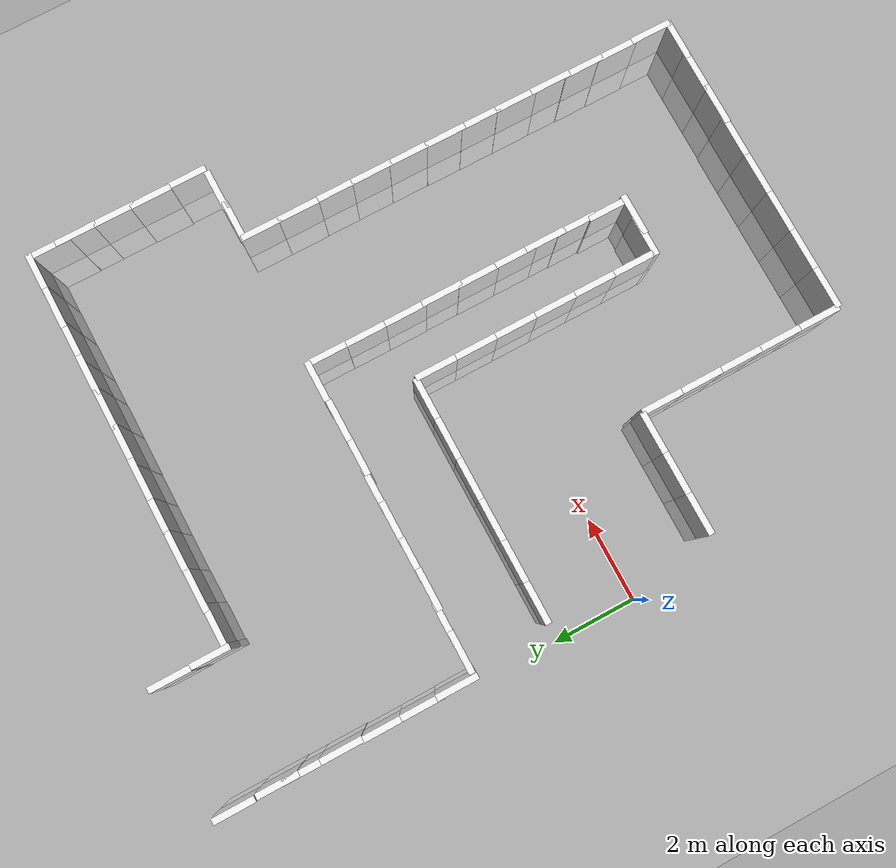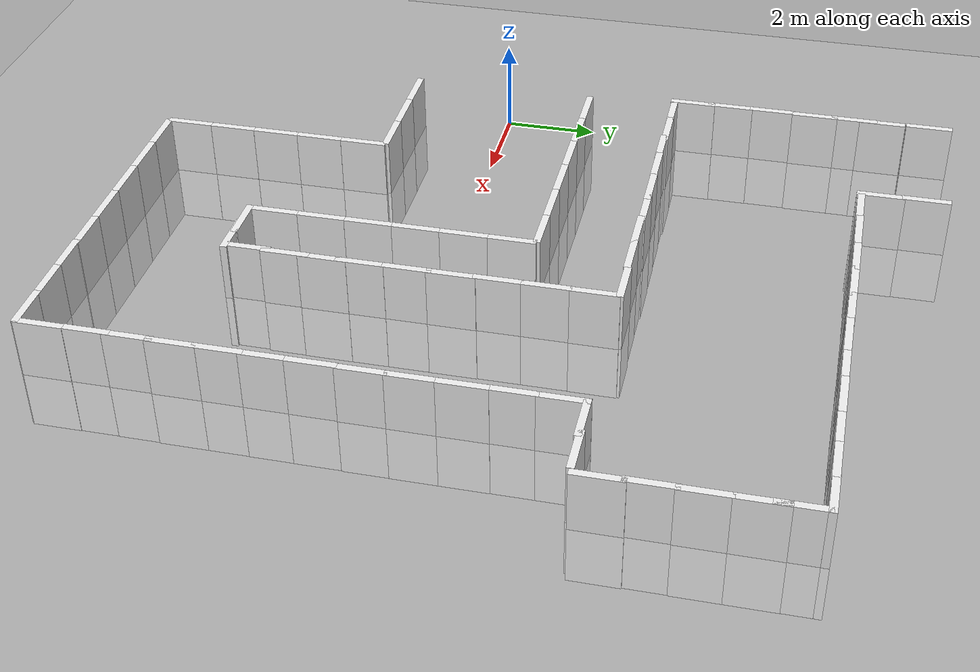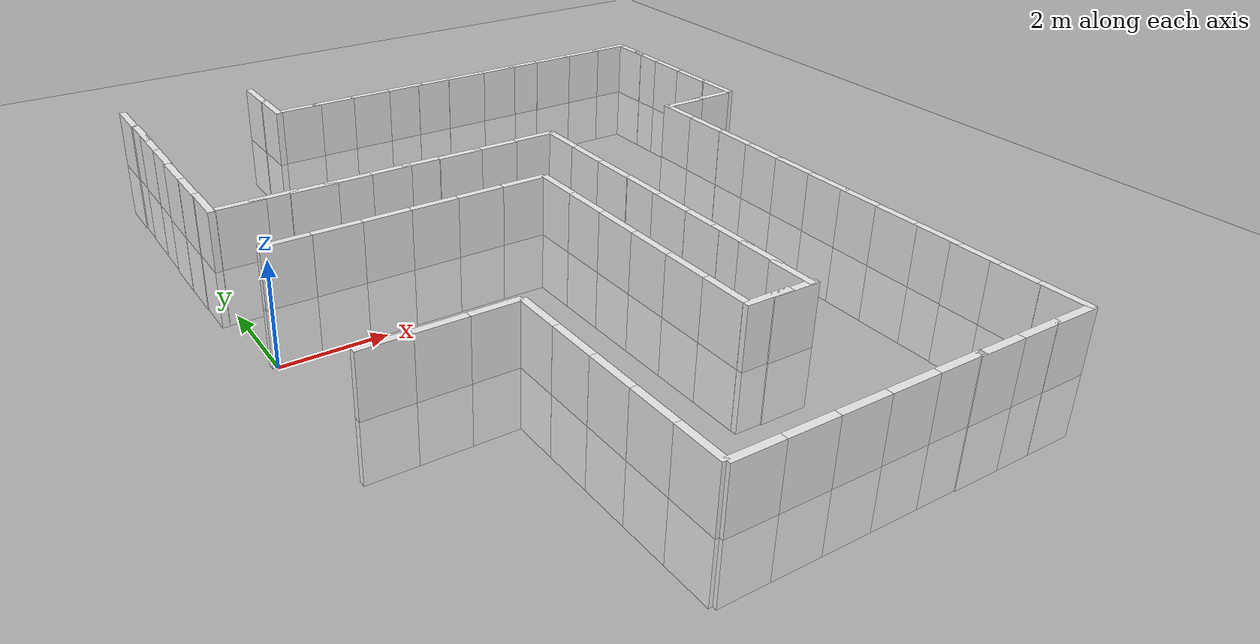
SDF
<sdf version="1.6">
 <world name="default">
  <light name="sun" type="directional">
   <pose>0 0 10 0 -0 0</pose>
   <diffuse>0.8 0.8 0.8 1</diffuse>
   <specular>0.1 0.1 0.1 1</specular>
   <attenuation>
    <range>1000</range>
    <constant>0.9</constant>
    <linear>0.01</linear>
    <quadratic>0.001</quadratic>
   </attenuation>
   <direction>-0.5 0.5 -1</direction>
  </light>
  <model name="ground_plane">
   <static>1</static>
   <link name="link">
    <collision name="collision">
     <geometry><plane><normal>0 0 1</normal><size>100 100</size></plane></geometry>
     <surface><friction><ode><mu>100</mu><mu2>50</mu2></ode></friction></surface>
    </collision>
    <visual name="visual">
     <cast_shadows>0</cast_shadows>
     <geometry><plane><normal>0 0 1</normal><size>100 100</size></plane></geometry>
     <material>
      <script><uri>file://media/materials/scripts/gazebo.material</uri><name>Gazebo/Grey</name></script>
     </material>
    </visual>
   </link>
  </model>
  <model name="wall_left_01">
   <link name="Wall_10">
    <inertial>
     <mass>1</mass>
     <inertia><ixx>1</ixx><ixy>0</ixy><ixz>0</ixz><iyy>1</iyy><iyz>0</iyz><izz>1</izz></inertia>
    </inertial>
    <visual name="Wall_10_Visual_0">
     <geometry><box><size>1 0.15 2.5</size></box></geometry>
     <material>
      <script>
       <uri>model://wall/materials/scripts</uri>
       <uri>model://wall/materials/textures</uri>
       <name>wall_white</name>
      </script>
      <shader type="pixel"><normal_map>__default__</normal_map></shader>
      <ambient>1 1 1 1</ambient>
      <diffuse>1 1 1 1</diffuse>
      <specular>0 0 0 1</specular>
      <emissive>0 0 0 1</emissive>
     </material>
     <meta><layer>0</layer></meta>
    </visual>
    <collision name="Wall_10_Collision_0">
     <geometry><box><size>1 0.15 2.5</size></box></geometry>
     <surface>
      <friction>
       <ode><mu>1</mu><mu2>1</mu2><fdir1>0 0 0</fdir1><slip1>0</slip1><slip2>0</slip2></ode>
       <torsional>
        <coefficient>1</coefficient>
        <patch_radius>0</patch_radius>
        <surface_radius>0</surface_radius>
        <use_patch_radius>1</use_patch_radius>
        <ode><slip>0</slip></ode>
       </torsional>
      </friction>
      <bounce><restitution_coefficient>0</restitution_coefficient><threshold>1e+06</threshold></bounce>
      <contact>
       <collide_without_contact>0</collide_without_contact>
       <collide_without_contact_bitmask>1</collide_without_contact_bitmask>
       <collide_bitmask>1</collide_bitmask>
       <ode>
        <soft_cfm>0</soft_cfm>
        <soft_erp>0.2</soft_erp>
        <kp>1e+13</kp>
        <kd>1</kd>
        <max_vel>0.01</max_vel>
        <min_depth>0</min_depth>
       </ode>
       <bullet>
        <split_impulse>1</split_impulse>
        <split_impulse_penetration_threshold>-0.01</split_impulse_penetration_threshold>
        <soft_cfm>0</soft_cfm>
        <soft_erp>0.2</soft_erp>
        <kp>1e+13</kp>
        <kd>1</kd>
       </bullet>
      </contact>
     </surface>
    </collision>
   </link>
   <static>1</static>
   <pose>1 2 0 0 -0 0</pose>
  </model>
  <model name="wall_left_02">
   <link name="Wall_10">
    <inertial>
     <mass>1</mass>
     <inertia><ixx>1</ixx><ixy>0</ixy><ixz>0</ixz><iyy>1</iyy><iyz>0</iyz><izz>1</izz></inertia>
    </inertial>
    <visual name="Wall_10_Visual_0">
     <geometry><box><size>1 0.15 2.5</size></box></geometry>
     <material>
      <script>
       <uri>model://wall/materials/scripts</uri>
       <uri>model://wall/materials/textures</uri>
       <name>wall_white</name>
      </script>
      <shader type="pixel"><normal_map>__default__</normal_map></shader>
      <ambient>1 1 1 1</ambient>
      <diffuse>1 1 1 1</diffuse>
      <specular>0 0 0 1</specular>
      <emissive>0 0 0 1</emissive>
     </material>
     <meta><layer>0</layer></meta>
    </visual>
    <collision name="Wall_10_Collision_0">
     <geometry><box><size>1 0.15 2.5</size></box></geometry>
     <surface>
      <friction>
       <ode><mu>1</mu><mu2>1</mu2><fdir1>0 0 0</fdir1><slip1>0</slip1><slip2>0</slip2></ode>
       <torsional>
        <coefficient>1</coefficient>
        <patch_radius>0</patch_radius>
        <surface_radius>0</surface_radius>
        <use_patch_radius>1</use_patch_radius>
        <ode><slip>0</slip></ode>
       </torsional>
      </friction>
      <bounce><restitution_coefficient>0</restitution_coefficient><threshold>1e+06</threshold></bounce>
      <contact>
       <collide_without_contact>0</collide_without_contact>
       <collide_without_contact_bitmask>1</collide_without_contact_bitmask>
       <collide_bitmask>1</collide_bitmask>
       <ode>
        <soft_cfm>0</soft_cfm>
        <soft_erp>0.2</soft_erp>
        <kp>1e+13</kp>
        <kd>1</kd>
        <max_vel>0.01</max_vel>
        <min_depth>0</min_depth>
       </ode>
       <bullet>
        <split_impulse>1</split_impulse>
        <split_impulse_penetration_threshold>-0.01</split_impulse_penetration_threshold>
        <soft_cfm>0</soft_cfm>
        <soft_erp>0.2</soft_erp>
        <kp>1e+13</kp>
        <kd>1</kd>
       </bullet>
      </contact>
     </surface>
    </collision>
   </link>
   <static>1</static>
   <pose>2 2 0 0 -0 0</pose>
  </model>
  <model name="wall_left_03">
   <link name="Wall_10">
    <inertial>
     <mass>1</mass>
     <inertia><ixx>1</ixx><ixy>0</ixy><ixz>0</ixz><iyy>1</iyy><iyz>0</iyz><izz>1</izz></inertia>
    </inertial>
    <visual name="Wall_10_Visual_0">
     <geometry><box><size>1 0.15 2.5</size></box></geometry>
     <material>
      <script>
       <uri>model://wall/materials/scripts</uri>
       <uri>model://wall/materials/textures</uri>
       <name>wall_white</name>
      </script>
      <shader type="pixel"><normal_map>__default__</normal_map></shader>
      <ambient>1 1 1 1</ambient>
      <diffuse>1 1 1 1</diffuse>
      <specular>0 0 0 1</specular>
      <emissive>0 0 0 1</emissive>
     </material>
     <meta><layer>0</layer></meta>
    </visual>
    <collision name="Wall_10_Collision_0">
     <geometry><box><size>1 0.15 2.5</size></box></geometry>
     <surface>
      <friction>
       <ode><mu>1</mu><mu2>1</mu2><fdir1>0 0 0</fdir1><slip1>0</slip1><slip2>0</slip2></ode>
       <torsional>
        <coefficient>1</coefficient>
        <patch_radius>0</patch_radius>
        <surface_radius>0</surface_radius>
        <use_patch_radius>1</use_patch_radius>
        <ode><slip>0</slip></ode>
       </torsional>
      </friction>
      <bounce><restitution_coefficient>0</restitution_coefficient><threshold>1e+06</threshold></bounce>
      <contact>
       <collide_without_contact>0</collide_without_contact>
       <collide_without_contact_bitmask>1</collide_without_contact_bitmask>
       <collide_bitmask>1</collide_bitmask>
       <ode>
        <soft_cfm>0</soft_cfm>
        <soft_erp>0.2</soft_erp>
        <kp>1e+13</kp>
        <kd>1</kd>
        <max_vel>0.01</max_vel>
        <min_depth>0</min_depth>
       </ode>
       <bullet>
        <split_impulse>1</split_impulse>
        <split_impulse_penetration_threshold>-0.01</split_impulse_penetration_threshold>
        <soft_cfm>0</soft_cfm>
        <soft_erp>0.2</soft_erp>
        <kp>1e+13</kp>
        <kd>1</kd>
       </bullet>
      </contact>
     </surface>
    </collision>
   </link>
   <static>1</static>
   <pose>3 2 0 0 -0 0</pose>
  </model>
  <model name="wall_left_04">
   <link name="Wall_10">
    <inertial>
     <mass>1</mass>
     <inertia><ixx>1</ixx><ixy>0</ixy><ixz>0</ixz><iyy>1</iyy><iyz>0</iyz><izz>1</izz></inertia>
    </inertial>
    <visual name="Wall_10_Visual_0">
     <geometry><box><size>1 0.15 2.5</size></box></geometry>
     <material>
      <script>
       <uri>model://wall/materials/scripts</uri>
       <uri>model://wall/materials/textures</uri>
       <name>wall_white</name>
      </script>
      <shader type="pixel"><normal_map>__default__</normal_map></shader>
      <ambient>1 1 1 1</ambient>
      <diffuse>1 1 1 1</diffuse>
      <specular>0 0 0 1</specular>
      <emissive>0 0 0 1</emissive>
     </material>
     <meta><layer>0</layer></meta>
    </visual>
    <collision name="Wall_10_Collision_0">
     <geometry><box><size>1 0.15 2.5</size></box></geometry>
     <surface>
      <friction>
       <ode><mu>1</mu><mu2>1</mu2><fdir1>0 0 0</fdir1><slip1>0</slip1><slip2>0</slip2></ode>
       <torsional>
        <coefficient>1</coefficient>
        <patch_radius>0</patch_radius>
        <surface_radius>0</surface_radius>
        <use_patch_radius>1</use_patch_radius>
        <ode><slip>0</slip></ode>
       </torsional>
      </friction>
      <bounce><restitution_coefficient>0</restitution_coefficient><threshold>1e+06</threshold></bounce>
      <contact>
       <collide_without_contact>0</collide_without_contact>
       <collide_without_contact_bitmask>1</collide_without_contact_bitmask>
       <collide_bitmask>1</collide_bitmask>
       <ode>
        <soft_cfm>0</soft_cfm>
        <soft_erp>0.2</soft_erp>
        <kp>1e+13</kp>
        <kd>1</kd>
        <max_vel>0.01</max_vel>
        <min_depth>0</min_depth>
       </ode>
       <bullet>
        <split_impulse>1</split_impulse>
        <split_impulse_penetration_threshold>-0.01</split_impulse_penetration_threshold>
        <soft_cfm>0</soft_cfm>
        <soft_erp>0.2</soft_erp>
        <kp>1e+13</kp>
        <kd>1</kd>
       </bullet>
      </contact>
     </surface>
    </collision>
   </link>
   <static>1</static>
   <pose>4 2 0 0 -0 0</pose>
  </model>
  <model name="wall_left_05">
   <link name="Wall_10">
    <inertial>
     <mass>1</mass>
     <inertia><ixx>1</ixx><ixy>0</ixy><ixz>0</ixz><iyy>1</iyy><iyz>0</iyz><izz>1</izz></inertia>
    </inertial>
    <visual name="Wall_10_Visual_0">
     <geometry><box><size>1 0.15 2.5</size></box></geometry>
     <material>
      <script>
       <uri>model://wall/materials/scripts</uri>
       <uri>model://wall/materials/textures</uri>
       <name>wall_white</name>
      </script>
      <shader type="pixel"><normal_map>__default__</normal_map></shader>
      <ambient>1 1 1 1</ambient>
      <diffuse>1 1 1 1</diffuse>
      <specular>0 0 0 1</specular>
      <emissive>0 0 0 1</emissive>
     </material>
     <meta><layer>0</layer></meta>
    </visual>
    <collision name="Wall_10_Collision_0">
     <geometry><box><size>1 0.15 2.5</size></box></geometry>
     <surface>
      <friction>
       <ode><mu>1</mu><mu2>1</mu2><fdir1>0 0 0</fdir1><slip1>0</slip1><slip2>0</slip2></ode>
       <torsional>
        <coefficient>1</coefficient>
        <patch_radius>0</patch_radius>
        <surface_radius>0</surface_radius>
        <use_patch_radius>1</use_patch_radius>
        <ode><slip>0</slip></ode>
       </torsional>
      </friction>
      <bounce><restitution_coefficient>0</restitution_coefficient><threshold>1e+06</threshold></bounce>
      <contact>
       <collide_without_contact>0</collide_without_contact>
       <collide_without_contact_bitmask>1</collide_without_contact_bitmask>
       <collide_bitmask>1</collide_bitmask>
       <ode>
        <soft_cfm>0</soft_cfm>
        <soft_erp>0.2</soft_erp>
        <kp>1e+13</kp>
        <kd>1</kd>
        <max_vel>0.01</max_vel>
        <min_depth>0</min_depth>
       </ode>
       <bullet>
        <split_impulse>1</split_impulse>
        <split_impulse_penetration_threshold>-0.01</split_impulse_penetration_threshold>
        <soft_cfm>0</soft_cfm>
        <soft_erp>0.2</soft_erp>
        <kp>1e+13</kp>
        <kd>1</kd>
       </bullet>
      </contact>
     </surface>
    </collision>
   </link>
   <static>1</static>
   <pose>5 2 0 0 -0 0</pose>
  </model>
  <model name="wall_left_06">
   <link name="Wall_10">
    <inertial>
     <mass>1</mass>
     <inertia><ixx>1</ixx><ixy>0</ixy><ixz>0</ixz><iyy>1</iyy><iyz>0</iyz><izz>1</izz></inertia>
    </inertial>
    <visual name="Wall_10_Visual_0">
     <geometry><box><size>1 0.15 2.5</size></box></geometry>
     <material>
      <script>
       <uri>model://wall/materials/scripts</uri>
       <uri>model://wall/materials/textures</uri>
       <name>wall_white</name>
      </script>
      <shader type="pixel"><normal_map>__default__</normal_map></shader>
      <ambient>1 1 1 1</ambient>
      <diffuse>1 1 1 1</diffuse>
      <specular>0 0 0 1</specular>
      <emissive>0 0 0 1</emissive>
     </material>
     <meta><layer>0</layer></meta>
    </visual>
    <collision name="Wall_10_Collision_0">
     <geometry><box><size>1 0.15 2.5</size></box></geometry>
     <surface>
      <friction>
       <ode><mu>1</mu><mu2>1</mu2><fdir1>0 0 0</fdir1><slip1>0</slip1><slip2>0</slip2></ode>
       <torsional>
        <coefficient>1</coefficient>
        <patch_radius>0</patch_radius>
        <surface_radius>0</surface_radius>
        <use_patch_radius>1</use_patch_radius>
        <ode><slip>0</slip></ode>
       </torsional>
      </friction>
      <bounce><restitution_coefficient>0</restitution_coefficient><threshold>1e+06</threshold></bounce>
      <contact>
       <collide_without_contact>0</collide_without_contact>
       <collide_without_contact_bitmask>1</collide_without_contact_bitmask>
       <collide_bitmask>1</collide_bitmask>
       <ode>
        <soft_cfm>0</soft_cfm>
        <soft_erp>0.2</soft_erp>
        <kp>1e+13</kp>
        <kd>1</kd>
        <max_vel>0.01</max_vel>
        <min_depth>0</min_depth>
       </ode>
       <bullet>
        <split_impulse>1</split_impulse>
        <split_impulse_penetration_threshold>-0.01</split_impulse_penetration_threshold>
        <soft_cfm>0</soft_cfm>
        <soft_erp>0.2</soft_erp>
        <kp>1e+13</kp>
        <kd>1</kd>
       </bullet>
      </contact>
     </surface>
    </collision>
   </link>
   <static>1</static>
   <pose>6 2 0 0 -0 0</pose>
  </model>
  <model name="wall_left_07">
   <link name="Wall_10">
    <inertial>
     <mass>1</mass>
     <inertia><ixx>1</ixx><ixy>0</ixy><ixz>0</ixz><iyy>1</iyy><iyz>0</iyz><izz>1</izz></inertia>
    </inertial>
    <visual name="Wall_10_Visual_0">
     <geometry><box><size>1 0.15 2.5</size></box></geometry>
     <material>
      <script>
       <uri>model://wall/materials/scripts</uri>
       <uri>model://wall/materials/textures</uri>
       <name>wall_white</name>
      </script>
      <shader type="pixel"><normal_map>__default__</normal_map></shader>
      <ambient>1 1 1 1</ambient>
      <diffuse>1 1 1 1</diffuse>
      <specular>0 0 0 1</specular>
      <emissive>0 0 0 1</emissive>
     </material>
     <meta><layer>0</layer></meta>
    </visual>
    <collision name="Wall_10_Collision_0">
     <geometry><box><size>1 0.15 2.5</size></box></geometry>
     <surface>
      <friction>
       <ode><mu>1</mu><mu2>1</mu2><fdir1>0 0 0</fdir1><slip1>0</slip1><slip2>0</slip2></ode>
       <torsional>
        <coefficient>1</coefficient>
        <patch_radius>0</patch_radius>
        <surface_radius>0</surface_radius>
        <use_patch_radius>1</use_patch_radius>
        <ode><slip>0</slip></ode>
       </torsional>
      </friction>
      <bounce><restitution_coefficient>0</restitution_coefficient><threshold>1e+06</threshold></bounce>
      <contact>
       <collide_without_contact>0</collide_without_contact>
       <collide_without_contact_bitmask>1</collide_without_contact_bitmask>
       <collide_bitmask>1</collide_bitmask>
       <ode>
        <soft_cfm>0</soft_cfm>
        <soft_erp>0.2</soft_erp>
        <kp>1e+13</kp>
        <kd>1</kd>
        <max_vel>0.01</max_vel>
        <min_depth>0</min_depth>
       </ode>
       <bullet>
        <split_impulse>1</split_impulse>
        <split_impulse_penetration_threshold>-0.01</split_impulse_penetration_threshold>
        <soft_cfm>0</soft_cfm>
        <soft_erp>0.2</soft_erp>
        <kp>1e+13</kp>
        <kd>1</kd>
       </bullet>
      </contact>
     </surface>
    </collision>
   </link>
   <static>1</static>
   <pose>6.5 1.5 0 0 -0 1.57</pose>
  </model>
  <model name="wall_left_08">
   <link name="Wall_10">
    <inertial>
     <mass>1</mass>
     <inertia><ixx>1</ixx><ixy>0</ixy><ixz>0</ixz><iyy>1</iyy><iyz>0</iyz><izz>1</izz></inertia>
    </inertial>
    <visual name="Wall_10_Visual_0">
     <geometry><box><size>1 0.15 2.5</size></box></geometry>
     <material>
      <script>
       <uri>model://wall/materials/scripts</uri>
       <uri>model://wall/materials/textures</uri>
       <name>wall_white</name>
      </script>
      <shader type="pixel"><normal_map>__default__</normal_map></shader>
      <ambient>1 1 1 1</ambient>
      <diffuse>1 1 1 1</diffuse>
      <specular>0 0 0 1</specular>
      <emissive>0 0 0 1</emissive>
     </material>
     <meta><layer>0</layer></meta>
    </visual>
    <collision name="Wall_10_Collision_0">
     <geometry><box><size>1 0.15 2.5</size></box></geometry>
     <surface>
      <friction>
       <ode><mu>1</mu><mu2>1</mu2><fdir1>0 0 0</fdir1><slip1>0</slip1><slip2>0</slip2></ode>
       <torsional>
        <coefficient>1</coefficient>
        <patch_radius>0</patch_radius>
        <surface_radius>0</surface_radius>
        <use_patch_radius>1</use_patch_radius>
        <ode><slip>0</slip></ode>
       </torsional>
      </friction>
      <bounce><restitution_coefficient>0</restitution_coefficient><threshold>1e+06</threshold></bounce>
      <contact>
       <collide_without_contact>0</collide_without_contact>
       <collide_without_contact_bitmask>1</collide_without_contact_bitmask>
       <collide_bitmask>1</collide_bitmask>
       <ode>
        <soft_cfm>0</soft_cfm>
        <soft_erp>0.2</soft_erp>
        <kp>1e+13</kp>
        <kd>1</kd>
        <max_vel>0.01</max_vel>
        <min_depth>0</min_depth>
       </ode>
       <bullet>
        <split_impulse>1</split_impulse>
        <split_impulse_penetration_threshold>-0.01</split_impulse_penetration_threshold>
        <soft_cfm>0</soft_cfm>
        <soft_erp>0.2</soft_erp>
        <kp>1e+13</kp>
        <kd>1</kd>
       </bullet>
      </contact>
     </surface>
    </collision>
   </link>
   <static>1</static>
   <pose>6.5 0.5 0 0 -0 1.57</pose>
  </model>
  <model name="wall_left_09">
   <link name="Wall_10">
    <inertial>
     <mass>1</mass>
     <inertia><ixx>1</ixx><ixy>0</ixy><ixz>0</ixz><iyy>1</iyy><iyz>0</iyz><izz>1</izz></inertia>
    </inertial>
    <visual name="Wall_10_Visual_0">
     <geometry><box><size>1 0.15 2.5</size></box></geometry>
     <material>
      <script>
       <uri>model://wall/materials/scripts</uri>
       <uri>model://wall/materials/textures</uri>
       <name>wall_white</name>
      </script>
      <shader type="pixel"><normal_map>__default__</normal_map></shader>
      <ambient>1 1 1 1</ambient>
      <diffuse>1 1 1 1</diffuse>
      <specular>0 0 0 1</specular>
      <emissive>0 0 0 1</emissive>
     </material>
     <meta><layer>0</layer></meta>
    </visual>
    <collision name="Wall_10_Collision_0">
     <geometry><box><size>1 0.15 2.5</size></box></geometry>
     <surface>
      <friction>
       <ode><mu>1</mu><mu2>1</mu2><fdir1>0 0 0</fdir1><slip1>0</slip1><slip2>0</slip2></ode>
       <torsional>
        <coefficient>1</coefficient>
        <patch_radius>0</patch_radius>
        <surface_radius>0</surface_radius>
        <use_patch_radius>1</use_patch_radius>
        <ode><slip>0</slip></ode>
       </torsional>
      </friction>
      <bounce><restitution_coefficient>0</restitution_coefficient><threshold>1e+06</threshold></bounce>
      <contact>
       <collide_without_contact>0</collide_without_contact>
       <collide_without_contact_bitmask>1</collide_without_contact_bitmask>
       <collide_bitmask>1</collide_bitmask>
       <ode>
        <soft_cfm>0</soft_cfm>
        <soft_erp>0.2</soft_erp>
        <kp>1e+13</kp>
        <kd>1</kd>
        <max_vel>0.01</max_vel>
        <min_depth>0</min_depth>
       </ode>
       <bullet>
        <split_impulse>1</split_impulse>
        <split_impulse_penetration_threshold>-0.01</split_impulse_penetration_threshold>
        <soft_cfm>0</soft_cfm>
        <soft_erp>0.2</soft_erp>
        <kp>1e+13</kp>
        <kd>1</kd>
       </bullet>
      </contact>
     </surface>
    </collision>
   </link>
   <static>1</static>
   <pose>6.5 -0.5 0 0 -0 1.57</pose>
  </model>
  <model name="wall_left_10">
   <link name="Wall_10">
    <inertial>
     <mass>1</mass>
     <inertia><ixx>1</ixx><ixy>0</ixy><ixz>0</ixz><iyy>1</iyy><iyz>0</iyz><izz>1</izz></inertia>
    </inertial>
    <visual name="Wall_10_Visual_0">
     <geometry><box><size>1 0.15 2.5</size></box></geometry>
     <material>
      <script>
       <uri>model://wall/materials/scripts</uri>
       <uri>model://wall/materials/textures</uri>
       <name>wall_white</name>
      </script>
      <shader type="pixel"><normal_map>__default__</normal_map></shader>
      <ambient>1 1 1 1</ambient>
      <diffuse>1 1 1 1</diffuse>
      <specular>0 0 0 1</specular>
      <emissive>0 0 0 1</emissive>
     </material>
     <meta><layer>0</layer></meta>
    </visual>
    <collision name="Wall_10_Collision_0">
     <geometry><box><size>1 0.15 2.5</size></box></geometry>
     <surface>
      <friction>
       <ode><mu>1</mu><mu2>1</mu2><fdir1>0 0 0</fdir1><slip1>0</slip1><slip2>0</slip2></ode>
       <torsional>
        <coefficient>1</coefficient>
        <patch_radius>0</patch_radius>
        <surface_radius>0</surface_radius>
        <use_patch_radius>1</use_patch_radius>
        <ode><slip>0</slip></ode>
       </torsional>
      </friction>
      <bounce><restitution_coefficient>0</restitution_coefficient><threshold>1e+06</threshold></bounce>
      <contact>
       <collide_without_contact>0</collide_without_contact>
       <collide_without_contact_bitmask>1</collide_without_contact_bitmask>
       <collide_bitmask>1</collide_bitmask>
       <ode>
        <soft_cfm>0</soft_cfm>
        <soft_erp>0.2</soft_erp>
        <kp>1e+13</kp>
        <kd>1</kd>
        <max_vel>0.01</max_vel>
        <min_depth>0</min_depth>
       </ode>
       <bullet>
        <split_impulse>1</split_impulse>
        <split_impulse_penetration_threshold>-0.01</split_impulse_penetration_threshold>
        <soft_cfm>0</soft_cfm>
        <soft_erp>0.2</soft_erp>
        <kp>1e+13</kp>
        <kd>1</kd>
       </bullet>
      </contact>
     </surface>
    </collision>
   </link>
   <static>1</static>
   <pose>6.5 -1.5 0 0 -0 1.57</pose>
  </model>
  <model name="wall_left_11">
   <link name="Wall_10">
    <inertial>
     <mass>1</mass>
     <inertia><ixx>1</ixx><ixy>0</ixy><ixz>0</ixz><iyy>1</iyy><iyz>0</iyz><izz>1</izz></inertia>
    </inertial>
    <visual name="Wall_10_Visual_0">
     <geometry><box><size>1 0.15 2.5</size></box></geometry>
     <material>
      <script>
       <uri>model://wall/materials/scripts</uri>
       <uri>model://wall/materials/textures</uri>
       <name>wall_white</name>
      </script>
      <shader type="pixel"><normal_map>__default__</normal_map></shader>
      <ambient>1 1 1 1</ambient>
      <diffuse>1 1 1 1</diffuse>
      <specular>0 0 0 1</specular>
      <emissive>0 0 0 1</emissive>
     </material>
     <meta><layer>0</layer></meta>
    </visual>
    <collision name="Wall_10_Collision_0">
     <geometry><box><size>1 0.15 2.5</size></box></geometry>
     <surface>
      <friction>
       <ode><mu>1</mu><mu2>1</mu2><fdir1>0 0 0</fdir1><slip1>0</slip1><slip2>0</slip2></ode>
       <torsional>
        <coefficient>1</coefficient>
        <patch_radius>0</patch_radius>
        <surface_radius>0</surface_radius>
        <use_patch_radius>1</use_patch_radius>
        <ode><slip>0</slip></ode>
       </torsional>
      </friction>
      <bounce><restitution_coefficient>0</restitution_coefficient><threshold>1e+06</threshold></bounce>
      <contact>
       <collide_without_contact>0</collide_without_contact>
       <collide_without_contact_bitmask>1</collide_without_contact_bitmask>
       <collide_bitmask>1</collide_bitmask>
       <ode>
        <soft_cfm>0</soft_cfm>
        <soft_erp>0.2</soft_erp>
        <kp>1e+13</kp>
        <kd>1</kd>
        <max_vel>0.01</max_vel>
        <min_depth>0</min_depth>
       </ode>
       <bullet>
        <split_impulse>1</split_impulse>
        <split_impulse_penetration_threshold>-0.01</split_impulse_penetration_threshold>
        <soft_cfm>0</soft_cfm>
        <soft_erp>0.2</soft_erp>
        <kp>1e+13</kp>
        <kd>1</kd>
       </bullet>
      </contact>
     </surface>
    </collision>
   </link>
   <static>1</static>
   <pose>6.5 -2.5 0 0 -0 1.57</pose>
  </model>
  <model name="wall_left_12">
   <link name="Wall_10">
    <inertial>
     <mass>1</mass>
     <inertia><ixx>1</ixx><ixy>0</ixy><ixz>0</ixz><iyy>1</iyy><iyz>0</iyz><izz>1</izz></inertia>
    </inertial>
    <visual name="Wall_10_Visual_0">
     <geometry><box><size>1 0.15 2.5</size></box></geometry>
     <material>
      <script>
       <uri>model://wall/materials/scripts</uri>
       <uri>model://wall/materials/textures</uri>
       <name>wall_white</name>
      </script>
      <shader type="pixel"><normal_map>__default__</normal_map></shader>
      <ambient>1 1 1 1</ambient>
      <diffuse>1 1 1 1</diffuse>
      <specular>0 0 0 1</specular>
      <emissive>0 0 0 1</emissive>
     </material>
     <meta><layer>0</layer></meta>
    </visual>
    <collision name="Wall_10_Collision_0">
     <geometry><box><size>1 0.15 2.5</size></box></geometry>
     <surface>
      <friction>
       <ode><mu>1</mu><mu2>1</mu2><fdir1>0 0 0</fdir1><slip1>0</slip1><slip2>0</slip2></ode>
       <torsional>
        <coefficient>1</coefficient>
        <patch_radius>0</patch_radius>
        <surface_radius>0</surface_radius>
        <use_patch_radius>1</use_patch_radius>
        <ode><slip>0</slip></ode>
       </torsional>
      </friction>
      <bounce><restitution_coefficient>0</restitution_coefficient><threshold>1e+06</threshold></bounce>
      <contact>
       <collide_without_contact>0</collide_without_contact>
       <collide_without_contact_bitmask>1</collide_without_contact_bitmask>
       <collide_bitmask>1</collide_bitmask>
       <ode>
        <soft_cfm>0</soft_cfm>
        <soft_erp>0.2</soft_erp>
        <kp>1e+13</kp>
        <kd>1</kd>
        <max_vel>0.01</max_vel>
        <min_depth>0</min_depth>
       </ode>
       <bullet>
        <split_impulse>1</split_impulse>
        <split_impulse_penetration_threshold>-0.01</split_impulse_penetration_threshold>
        <soft_cfm>0</soft_cfm>
        <soft_erp>0.2</soft_erp>
        <kp>1e+13</kp>
        <kd>1</kd>
       </bullet>
      </contact>
     </surface>
    </collision>
   </link>
   <static>1</static>
   <pose>6.5 -3.5 0 0 -0 1.57</pose>
  </model>
  <model name="wall_right_01">
   <link name="Wall_10">
    <inertial>
     <mass>1</mass>
     <inertia><ixx>1</ixx><ixy>0</ixy><ixz>0</ixz><iyy>1</iyy><iyz>0</iyz><izz>1</izz></inertia>
    </inertial>
    <visual name="Wall_10_Visual_0">
     <geometry><box><size>1 0.15 2.5</size></box></geometry>
     <material>
      <script>
       <uri>model://wall/materials/scripts</uri>
       <uri>model://wall/materials/textures</uri>
       <name>wall_white</name>
      </script>
      <shader type="pixel"><normal_map>__default__</normal_map></shader>
      <ambient>1 1 1 1</ambient>
      <diffuse>1 1 1 1</diffuse>
      <specular>0 0 0 1</specular>
      <emissive>0 0 0 1</emissive>
     </material>
     <meta><layer>0</layer></meta>
    </visual>
    <collision name="Wall_10_Collision_0">
     <geometry><box><size>1 0.15 2.5</size></box></geometry>
     <surface>
      <friction>
       <ode><mu>1</mu><mu2>1</mu2><fdir1>0 0 0</fdir1><slip1>0</slip1><slip2>0</slip2></ode>
       <torsional>
        <coefficient>1</coefficient>
        <patch_radius>0</patch_radius>
        <surface_radius>0</surface_radius>
        <use_patch_radius>1</use_patch_radius>
        <ode><slip>0</slip></ode>
       </torsional>
      </friction>
      <bounce><restitution_coefficient>0</restitution_coefficient><threshold>1e+06</threshold></bounce>
      <contact>
       <collide_without_contact>0</collide_without_contact>
       <collide_without_contact_bitmask>1</collide_without_contact_bitmask>
       <collide_bitmask>1</collide_bitmask>
       <ode>
        <soft_cfm>0</soft_cfm>
        <soft_erp>0.2</soft_erp>
        <kp>1e+13</kp>
        <kd>1</kd>
        <max_vel>0.01</max_vel>
        <min_depth>0</min_depth>
       </ode>
       <bullet>
        <split_impulse>1</split_impulse>
        <split_impulse_penetration_threshold>-0.01</split_impulse_penetration_threshold>
        <soft_cfm>0</soft_cfm>
        <soft_erp>0.2</soft_erp>
        <kp>1e+13</kp>
        <kd>1</kd>
       </bullet>
      </contact>
     </surface>
    </collision>
   </link>
   <static>1</static>
   <pose>1 -2 0 0 -0 0</pose>
  </model>
  <model name="wall_right_02">
   <link name="Wall_10">
    <inertial>
     <mass>1</mass>
     <inertia><ixx>1</ixx><ixy>0</ixy><ixz>0</ixz><iyy>1</iyy><iyz>0</iyz><izz>1</izz></inertia>
    </inertial>
    <visual name="Wall_10_Visual_0">
     <geometry><box><size>1 0.15 2.5</size></box></geometry>
     <material>
      <script>
       <uri>model://wall/materials/scripts</uri>
       <uri>model://wall/materials/textures</uri>
       <name>wall_white</name>
      </script>
      <shader type="pixel"><normal_map>__default__</normal_map></shader>
      <ambient>1 1 1 1</ambient>
      <diffuse>1 1 1 1</diffuse>
      <specular>0 0 0 1</specular>
      <emissive>0 0 0 1</emissive>
     </material>
     <meta><layer>0</layer></meta>
    </visual>
    <collision name="Wall_10_Collision_0">
     <geometry><box><size>1 0.15 2.5</size></box></geometry>
     <surface>
      <friction>
       <ode><mu>1</mu><mu2>1</mu2><fdir1>0 0 0</fdir1><slip1>0</slip1><slip2>0</slip2></ode>
       <torsional>
        <coefficient>1</coefficient>
        <patch_radius>0</patch_radius>
        <surface_radius>0</surface_radius>
        <use_patch_radius>1</use_patch_radius>
        <ode><slip>0</slip></ode>
       </torsional>
      </friction>
      <bounce><restitution_coefficient>0</restitution_coefficient><threshold>1e+06</threshold></bounce>
      <contact>
       <collide_without_contact>0</collide_without_contact>
       <collide_without_contact_bitmask>1</collide_without_contact_bitmask>
       <collide_bitmask>1</collide_bitmask>
       <ode>
        <soft_cfm>0</soft_cfm>
        <soft_erp>0.2</soft_erp>
        <kp>1e+13</kp>
        <kd>1</kd>
        <max_vel>0.01</max_vel>
        <min_depth>0</min_depth>
       </ode>
       <bullet>
        <split_impulse>1</split_impulse>
        <split_impulse_penetration_threshold>-0.01</split_impulse_penetration_threshold>
        <soft_cfm>0</soft_cfm>
        <soft_erp>0.2</soft_erp>
        <kp>1e+13</kp>
        <kd>1</kd>
       </bullet>
      </contact>
     </surface>
    </collision>
   </link>
   <static>1</static>
   <pose>2 -2 0 0 -0 0</pose>
  </model>
  <model name="wall_right_03">
   <link name="Wall_10">
    <inertial>
     <mass>1</mass>
     <inertia><ixx>1</ixx><ixy>0</ixy><ixz>0</ixz><iyy>1</iyy><iyz>0</iyz><izz>1</izz></inertia>
    </inertial>
    <visual name="Wall_10_Visual_0">
     <geometry><box><size>1 0.15 2.5</size></box></geometry>
     <material>
      <script>
       <uri>model://wall/materials/scripts</uri>
       <uri>model://wall/materials/textures</uri>
       <name>wall_white</name>
      </script>
      <shader type="pixel"><normal_map>__default__</normal_map></shader>
      <ambient>1 1 1 1</ambient>
      <diffuse>1 1 1 1</diffuse>
      <specular>0 0 0 1</specular>
      <emissive>0 0 0 1</emissive>
     </material>
     <meta><layer>0</layer></meta>
    </visual>
    <collision name="Wall_10_Collision_0">
     <geometry><box><size>1 0.15 2.5</size></box></geometry>
     <surface>
      <friction>
       <ode><mu>1</mu><mu2>1</mu2><fdir1>0 0 0</fdir1><slip1>0</slip1><slip2>0</slip2></ode>
       <torsional>
        <coefficient>1</coefficient>
        <patch_radius>0</patch_radius>
        <surface_radius>0</surface_radius>
        <use_patch_radius>1</use_patch_radius>
        <ode><slip>0</slip></ode>
       </torsional>
      </friction>
      <bounce><restitution_coefficient>0</restitution_coefficient><threshold>1e+06</threshold></bounce>
      <contact>
       <collide_without_contact>0</collide_without_contact>
       <collide_without_contact_bitmask>1</collide_without_contact_bitmask>
       <collide_bitmask>1</collide_bitmask>
       <ode>
        <soft_cfm>0</soft_cfm>
        <soft_erp>0.2</soft_erp>
        <kp>1e+13</kp>
        <kd>1</kd>
        <max_vel>0.01</max_vel>
        <min_depth>0</min_depth>
       </ode>
       <bullet>
        <split_impulse>1</split_impulse>
        <split_impulse_penetration_threshold>-0.01</split_impulse_penetration_threshold>
        <soft_cfm>0</soft_cfm>
        <soft_erp>0.2</soft_erp>
        <kp>1e+13</kp>
        <kd>1</kd>
       </bullet>
      </contact>
     </surface>
    </collision>
   </link>
   <static>1</static>
   <pose>3 -2 0 0 -0 0</pose>
  </model>
  <model name="wall_right_04">
   <link name="Wall_10">
    <inertial>
     <mass>1</mass>
     <inertia><ixx>1</ixx><ixy>0</ixy><ixz>0</ixz><iyy>1</iyy><iyz>0</iyz><izz>1</izz></inertia>
    </inertial>
    <visual name="Wall_10_Visual_0">
     <geometry><box><size>1 0.15 2.5</size></box></geometry>
     <material>
      <script>
       <uri>model://wall/materials/scripts</uri>
       <uri>model://wall/materials/textures</uri>
       <name>wall_white</name>
      </script>
      <shader type="pixel"><normal_map>__default__</normal_map></shader>
      <ambient>1 1 1 1</ambient>
      <diffuse>1 1 1 1</diffuse>
      <specular>0 0 0 1</specular>
      <emissive>0 0 0 1</emissive>
     </material>
     <meta><layer>0</layer></meta>
    </visual>
    <collision name="Wall_10_Collision_0">
     <geometry><box><size>1 0.15 2.5</size></box></geometry>
     <surface>
      <friction>
       <ode><mu>1</mu><mu2>1</mu2><fdir1>0 0 0</fdir1><slip1>0</slip1><slip2>0</slip2></ode>
       <torsional>
        <coefficient>1</coefficient>
        <patch_radius>0</patch_radius>
        <surface_radius>0</surface_radius>
        <use_patch_radius>1</use_patch_radius>
        <ode><slip>0</slip></ode>
       </torsional>
      </friction>
      <bounce><restitution_coefficient>0</restitution_coefficient><threshold>1e+06</threshold></bounce>
      <contact>
       <collide_without_contact>0</collide_without_contact>
       <collide_without_contact_bitmask>1</collide_without_contact_bitmask>
       <collide_bitmask>1</collide_bitmask>
       <ode>
        <soft_cfm>0</soft_cfm>
        <soft_erp>0.2</soft_erp>
        <kp>1e+13</kp>
        <kd>1</kd>
        <max_vel>0.01</max_vel>
        <min_depth>0</min_depth>
       </ode>
       <bullet>
        <split_impulse>1</split_impulse>
        <split_impulse_penetration_threshold>-0.01</split_impulse_penetration_threshold>
        <soft_cfm>0</soft_cfm>
        <soft_erp>0.2</soft_erp>
        <kp>1e+13</kp>
        <kd>1</kd>
       </bullet>
      </contact>
     </surface>
    </collision>
   </link>
   <static>1</static>
   <pose>3.5 -2.5 0 0 -0 1.57</pose>
  </model>
  <model name="wall_right_05">
   <link name="Wall_10">
    <inertial>
     <mass>1</mass>
     <inertia><ixx>1</ixx><ixy>0</ixy><ixz>0</ixz><iyy>1</iyy><iyz>0</iyz><izz>1</izz></inertia>
    </inertial>
    <visual name="Wall_10_Visual_0">
     <geometry><box><size>1 0.15 2.5</size></box></geometry>
     <material>
      <script>
       <uri>model://wall/materials/scripts</uri>
       <uri>model://wall/materials/textures</uri>
       <name>wall_white</name>
      </script>
      <shader type="pixel"><normal_map>__default__</normal_map></shader>
      <ambient>1 1 1 1</ambient>
      <diffuse>1 1 1 1</diffuse>
      <specular>0 0 0 1</specular>
      <emissive>0 0 0 1</emissive>
     </material>
     <meta><layer>0</layer></meta>
    </visual>
    <collision name="Wall_10_Collision_0">
     <geometry><box><size>1 0.15 2.5</size></box></geometry>
     <surface>
      <friction>
       <ode><mu>1</mu><mu2>1</mu2><fdir1>0 0 0</fdir1><slip1>0</slip1><slip2>0</slip2></ode>
       <torsional>
        <coefficient>1</coefficient>
        <patch_radius>0</patch_radius>
        <surface_radius>0</surface_radius>
        <use_patch_radius>1</use_patch_radius>
        <ode><slip>0</slip></ode>
       </torsional>
      </friction>
      <bounce><restitution_coefficient>0</restitution_coefficient><threshold>1e+06</threshold></bounce>
      <contact>
       <collide_without_contact>0</collide_without_contact>
       <collide_without_contact_bitmask>1</collide_without_contact_bitmask>
       <collide_bitmask>1</collide_bitmask>
       <ode>
        <soft_cfm>0</soft_cfm>
        <soft_erp>0.2</soft_erp>
        <kp>1e+13</kp>
        <kd>1</kd>
        <max_vel>0.01</max_vel>
        <min_depth>0</min_depth>
       </ode>
       <bullet>
        <split_impulse>1</split_impulse>
        <split_impulse_penetration_threshold>-0.01</split_impulse_penetration_threshold>
        <soft_cfm>0</soft_cfm>
        <soft_erp>0.2</soft_erp>
        <kp>1e+13</kp>
        <kd>1</kd>
       </bullet>
      </contact>
     </surface>
    </collision>
   </link>
   <static>1</static>
   <pose>3.5 -3.5 0 0 -0 1.57</pose>
  </model>
  <model name="wall_right_06">
   <link name="Wall_10">
    <inertial>
     <mass>1</mass>
     <inertia><ixx>1</ixx><ixy>0</ixy><ixz>0</ixz><iyy>1</iyy><iyz>0</iyz><izz>1</izz></inertia>
    </inertial>
    <visual name="Wall_10_Visual_0">
     <geometry><box><size>1 0.15 2.5</size></box></geometry>
     <material>
      <script>
       <uri>model://wall/materials/scripts</uri>
       <uri>model://wall/materials/textures</uri>
       <name>wall_white</name>
      </script>
      <shader type="pixel"><normal_map>__default__</normal_map></shader>
      <ambient>1 1 1 1</ambient>
      <diffuse>1 1 1 1</diffuse>
      <specular>0 0 0 1</specular>
      <emissive>0 0 0 1</emissive>
     </material>
     <meta><layer>0</layer></meta>
    </visual>
    <collision name="Wall_10_Collision_0">
     <geometry><box><size>1 0.15 2.5</size></box></geometry>
     <surface>
      <friction>
       <ode><mu>1</mu><mu2>1</mu2><fdir1>0 0 0</fdir1><slip1>0</slip1><slip2>0</slip2></ode>
       <torsional>
        <coefficient>1</coefficient>
        <patch_radius>0</patch_radius>
        <surface_radius>0</surface_radius>
        <use_patch_radius>1</use_patch_radius>
        <ode><slip>0</slip></ode>
       </torsional>
      </friction>
      <bounce><restitution_coefficient>0</restitution_coefficient><threshold>1e+06</threshold></bounce>
      <contact>
       <collide_without_contact>0</collide_without_contact>
       <collide_without_contact_bitmask>1</collide_without_contact_bitmask>
       <collide_bitmask>1</collide_bitmask>
       <ode>
        <soft_cfm>0</soft_cfm>
        <soft_erp>0.2</soft_erp>
        <kp>1e+13</kp>
        <kd>1</kd>
        <max_vel>0.01</max_vel>
        <min_depth>0</min_depth>
       </ode>
       <bullet>
        <split_impulse>1</split_impulse>
        <split_impulse_penetration_threshold>-0.01</split_impulse_penetration_threshold>
        <soft_cfm>0</soft_cfm>
        <soft_erp>0.2</soft_erp>
        <kp>1e+13</kp>
        <kd>1</kd>
       </bullet>
      </contact>
     </surface>
    </collision>
   </link>
   <static>1</static>
   <pose>3.5 -4.5 0 0 -0 1.57</pose>
  </model>
  <model name="wall_right_07">
   <link name="Wall_10">
    <inertial>
     <mass>1</mass>
     <inertia><ixx>1</ixx><ixy>0</ixy><ixz>0</ixz><iyy>1</iyy><iyz>0</iyz><izz>1</izz></inertia>
    </inertial>
    <visual name="Wall_10_Visual_0">
     <geometry><box><size>1 0.15 2.5</size></box></geometry>
     <material>
      <script>
       <uri>model://wall/materials/scripts</uri>
       <uri>model://wall/materials/textures</uri>
       <name>wall_white</name>
      </script>
      <shader type="pixel"><normal_map>__default__</normal_map></shader>
      <ambient>1 1 1 1</ambient>
      <diffuse>1 1 1 1</diffuse>
      <specular>0 0 0 1</specular>
      <emissive>0 0 0 1</emissive>
     </material>
     <meta><layer>0</layer></meta>
    </visual>
    <collision name="Wall_10_Collision_0">
     <geometry><box><size>1 0.15 2.5</size></box></geometry>
     <surface>
      <friction>
       <ode><mu>1</mu><mu2>1</mu2><fdir1>0 0 0</fdir1><slip1>0</slip1><slip2>0</slip2></ode>
       <torsional>
        <coefficient>1</coefficient>
        <patch_radius>0</patch_radius>
        <surface_radius>0</surface_radius>
        <use_patch_radius>1</use_patch_radius>
        <ode><slip>0</slip></ode>
       </torsional>
      </friction>
      <bounce><restitution_coefficient>0</restitution_coefficient><threshold>1e+06</threshold></bounce>
      <contact>
       <collide_without_contact>0</collide_without_contact>
       <collide_without_contact_bitmask>1</collide_without_contact_bitmask>
       <collide_bitmask>1</collide_bitmask>
       <ode>
        <soft_cfm>0</soft_cfm>
        <soft_erp>0.2</soft_erp>
        <kp>1e+13</kp>
        <kd>1</kd>
        <max_vel>0.01</max_vel>
        <min_depth>0</min_depth>
       </ode>
       <bullet>
        <split_impulse>1</split_impulse>
        <split_impulse_penetration_threshold>-0.01</split_impulse_penetration_threshold>
        <soft_cfm>0</soft_cfm>
        <soft_erp>0.2</soft_erp>
        <kp>1e+13</kp>
        <kd>1</kd>
       </bullet>
      </contact>
     </surface>
    </collision>
   </link>
   <static>1</static>
   <pose>3.5 -5.5 0 0 -0 1.57</pose>
  </model>
  <model name="wall_right_08">
   <link name="Wall_10">
    <inertial>
     <mass>1</mass>
     <inertia><ixx>1</ixx><ixy>0</ixy><ixz>0</ixz><iyy>1</iyy><iyz>0</iyz><izz>1</izz></inertia>
    </inertial>
    <visual name="Wall_10_Visual_0">
     <geometry><box><size>1 0.15 2.5</size></box></geometry>
     <material>
      <script>
       <uri>model://wall/materials/scripts</uri>
       <uri>model://wall/materials/textures</uri>
       <name>wall_white</name>
      </script>
      <shader type="pixel"><normal_map>__default__</normal_map></shader>
      <ambient>1 1 1 1</ambient>
      <diffuse>1 1 1 1</diffuse>
      <specular>0 0 0 1</specular>
      <emissive>0 0 0 1</emissive>
     </material>
     <meta><layer>0</layer></meta>
    </visual>
    <collision name="Wall_10_Collision_0">
     <geometry><box><size>1 0.15 2.5</size></box></geometry>
     <surface>
      <friction>
       <ode><mu>1</mu><mu2>1</mu2><fdir1>0 0 0</fdir1><slip1>0</slip1><slip2>0</slip2></ode>
       <torsional>
        <coefficient>1</coefficient>
        <patch_radius>0</patch_radius>
        <surface_radius>0</surface_radius>
        <use_patch_radius>1</use_patch_radius>
        <ode><slip>0</slip></ode>
       </torsional>
      </friction>
      <bounce><restitution_coefficient>0</restitution_coefficient><threshold>1e+06</threshold></bounce>
      <contact>
       <collide_without_contact>0</collide_without_contact>
       <collide_without_contact_bitmask>1</collide_without_contact_bitmask>
       <collide_bitmask>1</collide_bitmask>
       <ode>
        <soft_cfm>0</soft_cfm>
        <soft_erp>0.2</soft_erp>
        <kp>1e+13</kp>
        <kd>1</kd>
        <max_vel>0.01</max_vel>
        <min_depth>0</min_depth>
       </ode>
       <bullet>
        <split_impulse>1</split_impulse>
        <split_impulse_penetration_threshold>-0.01</split_impulse_penetration_threshold>
        <soft_cfm>0</soft_cfm>
        <soft_erp>0.2</soft_erp>
        <kp>1e+13</kp>
        <kd>1</kd>
       </bullet>
      </contact>
     </surface>
    </collision>
   </link>
   <static>1</static>
   <pose>3.5 -6.5 0 0 -0 1.57</pose>
  </model>
  <model name="wall_right_09">
   <link name="Wall_10">
    <inertial>
     <mass>1</mass>
     <inertia><ixx>1</ixx><ixy>0</ixy><ixz>0</ixz><iyy>1</iyy><iyz>0</iyz><izz>1</izz></inertia>
    </inertial>
    <visual name="Wall_10_Visual_0">
     <geometry><box><size>1 0.15 2.5</size></box></geometry>
     <material>
      <script>
       <uri>model://wall/materials/scripts</uri>
       <uri>model://wall/materials/textures</uri>
       <name>wall_white</name>
      </script>
      <shader type="pixel"><normal_map>__default__</normal_map></shader>
      <ambient>1 1 1 1</ambient>
      <diffuse>1 1 1 1</diffuse>
      <specular>0 0 0 1</specular>
      <emissive>0 0 0 1</emissive>
     </material>
     <meta><layer>0</layer></meta>
    </visual>
    <collision name="Wall_10_Collision_0">
     <geometry><box><size>1 0.15 2.5</size></box></geometry>
     <surface>
      <friction>
       <ode><mu>1</mu><mu2>1</mu2><fdir1>0 0 0</fdir1><slip1>0</slip1><slip2>0</slip2></ode>
       <torsional>
        <coefficient>1</coefficient>
        <patch_radius>0</patch_radius>
        <surface_radius>0</surface_radius>
        <use_patch_radius>1</use_patch_radius>
        <ode><slip>0</slip></ode>
       </torsional>
      </friction>
      <bounce><restitution_coefficient>0</restitution_coefficient><threshold>1e+06</threshold></bounce>
      <contact>
       <collide_without_contact>0</collide_without_contact>
       <collide_without_contact_bitmask>1</collide_without_contact_bitmask>
       <collide_bitmask>1</collide_bitmask>
       <ode>
        <soft_cfm>0</soft_cfm>
        <soft_erp>0.2</soft_erp>
        <kp>1e+13</kp>
        <kd>1</kd>
        <max_vel>0.01</max_vel>
        <min_depth>0</min_depth>
       </ode>
       <bullet>
        <split_impulse>1</split_impulse>
        <split_impulse_penetration_threshold>-0.01</split_impulse_penetration_threshold>
        <soft_cfm>0</soft_cfm>
        <soft_erp>0.2</soft_erp>
        <kp>1e+13</kp>
        <kd>1</kd>
       </bullet>
      </contact>
     </surface>
    </collision>
   </link>
   <static>1</static>
   <pose>4 -7 0 0 -0 0</pose>
  </model>
  <model name="wall_right_10">
   <link name="Wall_10">
    <inertial>
     <mass>1</mass>
     <inertia><ixx>1</ixx><ixy>0</ixy><ixz>0</ixz><iyy>1</iyy><iyz>0</iyz><izz>1</izz></inertia>
    </inertial>
    <visual name="Wall_10_Visual_0">
     <geometry><box><size>1 0.15 2.5</size></box></geometry>
     <material>
      <script>
       <uri>model://wall/materials/scripts</uri>
       <uri>model://wall/materials/textures</uri>
       <name>wall_white</name>
      </script>
      <shader type="pixel"><normal_map>__default__</normal_map></shader>
      <ambient>1 1 1 1</ambient>
      <diffuse>1 1 1 1</diffuse>
      <specular>0 0 0 1</specular>
      <emissive>0 0 0 1</emissive>
     </material>
     <meta><layer>0</layer></meta>
    </visual>
    <collision name="Wall_10_Collision_0">
     <geometry><box><size>1 0.15 2.5</size></box></geometry>
     <surface>
      <friction>
       <ode><mu>1</mu><mu2>1</mu2><fdir1>0 0 0</fdir1><slip1>0</slip1><slip2>0</slip2></ode>
       <torsional>
        <coefficient>1</coefficient>
        <patch_radius>0</patch_radius>
        <surface_radius>0</surface_radius>
        <use_patch_radius>1</use_patch_radius>
        <ode><slip>0</slip></ode>
       </torsional>
      </friction>
      <bounce><restitution_coefficient>0</restitution_coefficient><threshold>1e+06</threshold></bounce>
      <contact>
       <collide_without_contact>0</collide_without_contact>
       <collide_without_contact_bitmask>1</collide_without_contact_bitmask>
       <collide_bitmask>1</collide_bitmask>
       <ode>
        <soft_cfm>0</soft_cfm>
        <soft_erp>0.2</soft_erp>
        <kp>1e+13</kp>
        <kd>1</kd>
        <max_vel>0.01</max_vel>
        <min_depth>0</min_depth>
       </ode>
       <bullet>
        <split_impulse>1</split_impulse>
        <split_impulse_penetration_threshold>-0.01</split_impulse_penetration_threshold>
        <soft_cfm>0</soft_cfm>
        <soft_erp>0.2</soft_erp>
        <kp>1e+13</kp>
        <kd>1</kd>
       </bullet>
      </contact>
     </surface>
    </collision>
   </link>
   <static>1</static>
   <pose>5 -7 0 0 -0 0</pose>
  </model>
  <model name="wall_right_11">
   <link name="Wall_10">
    <inertial>
     <mass>1</mass>
     <inertia><ixx>1</ixx><ixy>0</ixy><ixz>0</ixz><iyy>1</iyy><iyz>0</iyz><izz>1</izz></inertia>
    </inertial>
    <visual name="Wall_10_Visual_0">
     <geometry><box><size>1 0.15 2.5</size></box></geometry>
     <material>
      <script>
       <uri>model://wall/materials/scripts</uri>
       <uri>model://wall/materials/textures</uri>
       <name>wall_white</name>
      </script>
      <shader type="pixel"><normal_map>__default__</normal_map></shader>
      <ambient>1 1 1 1</ambient>
      <diffuse>1 1 1 1</diffuse>
      <specular>0 0 0 1</specular>
      <emissive>0 0 0 1</emissive>
     </material>
     <meta><layer>0</layer></meta>
    </visual>
    <collision name="Wall_10_Collision_0">
     <geometry><box><size>1 0.15 2.5</size></box></geometry>
     <surface>
      <friction>
       <ode><mu>1</mu><mu2>1</mu2><fdir1>0 0 0</fdir1><slip1>0</slip1><slip2>0</slip2></ode>
       <torsional>
        <coefficient>1</coefficient>
        <patch_radius>0</patch_radius>
        <surface_radius>0</surface_radius>
        <use_patch_radius>1</use_patch_radius>
        <ode><slip>0</slip></ode>
       </torsional>
      </friction>
      <bounce><restitution_coefficient>0</restitution_coefficient><threshold>1e+06</threshold></bounce>
      <contact>
       <collide_without_contact>0</collide_without_contact>
       <collide_without_contact_bitmask>1</collide_without_contact_bitmask>
       <collide_bitmask>1</collide_bitmask>
       <ode>
        <soft_cfm>0</soft_cfm>
        <soft_erp>0.2</soft_erp>
        <kp>1e+13</kp>
        <kd>1</kd>
        <max_vel>0.01</max_vel>
        <min_depth>0</min_depth>
       </ode>
       <bullet>
        <split_impulse>1</split_impulse>
        <split_impulse_penetration_threshold>-0.01</split_impulse_penetration_threshold>
        <soft_cfm>0</soft_cfm>
        <soft_erp>0.2</soft_erp>
        <kp>1e+13</kp>
        <kd>1</kd>
       </bullet>
      </contact>
     </surface>
    </collision>
   </link>
   <static>1</static>
   <pose>6 -7 0 0 -0 0</pose>
  </model>
  <model name="wall_right_12">
   <link name="Wall_10">
    <inertial>
     <mass>1</mass>
     <inertia><ixx>1</ixx><ixy>0</ixy><ixz>0</ixz><iyy>1</iyy><iyz>0</iyz><izz>1</izz></inertia>
    </inertial>
    <visual name="Wall_10_Visual_0">
     <geometry><box><size>1 0.15 2.5</size></box></geometry>
     <material>
      <script>
       <uri>model://wall/materials/scripts</uri>
       <uri>model://wall/materials/textures</uri>
       <name>wall_white</name>
      </script>
      <shader type="pixel"><normal_map>__default__</normal_map></shader>
      <ambient>1 1 1 1</ambient>
      <diffuse>1 1 1 1</diffuse>
      <specular>0 0 0 1</specular>
      <emissive>0 0 0 1</emissive>
     </material>
     <meta><layer>0</layer></meta>
    </visual>
    <collision name="Wall_10_Collision_0">
     <geometry><box><size>1 0.15 2.5</size></box></geometry>
     <surface>
      <friction>
       <ode><mu>1</mu><mu2>1</mu2><fdir1>0 0 0</fdir1><slip1>0</slip1><slip2>0</slip2></ode>
       <torsional>
        <coefficient>1</coefficient>
        <patch_radius>0</patch_radius>
        <surface_radius>0</surface_radius>
        <use_patch_radius>1</use_patch_radius>
        <ode><slip>0</slip></ode>
       </torsional>
      </friction>
      <bounce><restitution_coefficient>0</restitution_coefficient><threshold>1e+06</threshold></bounce>
      <contact>
       <collide_without_contact>0</collide_without_contact>
       <collide_without_contact_bitmask>1</collide_without_contact_bitmask>
       <collide_bitmask>1</collide_bitmask>
       <ode>
        <soft_cfm>0</soft_cfm>
        <soft_erp>0.2</soft_erp>
        <kp>1e+13</kp>
        <kd>1</kd>
        <max_vel>0.01</max_vel>
        <min_depth>0</min_depth>
       </ode>
       <bullet>
        <split_impulse>1</split_impulse>
        <split_impulse_penetration_threshold>-0.01</split_impulse_penetration_threshold>
        <soft_cfm>0</soft_cfm>
        <soft_erp>0.2</soft_erp>
        <kp>1e+13</kp>
        <kd>1</kd>
       </bullet>
      </contact>
     </surface>
    </collision>
   </link>
   <static>1</static>
   <pose>7 -7 0 0 -0 0</pose>
  </model>
  <model name="wall_right_13">
   <link name="Wall_10">
    <inertial>
     <mass>1</mass>
     <inertia><ixx>1</ixx><ixy>0</ixy><ixz>0</ixz><iyy>1</iyy><iyz>0</iyz><izz>1</izz></inertia>
    </inertial>
    <visual name="Wall_10_Visual_0">
     <geometry><box><size>1 0.15 2.5</size></box></geometry>
     <material>
      <script>
       <uri>model://wall/materials/scripts</uri>
       <uri>model://wall/materials/textures</uri>
       <name>wall_white</name>
      </script>
      <shader type="pixel"><normal_map>__default__</normal_map></shader>
      <ambient>1 1 1 1</ambient>
      <diffuse>1 1 1 1</diffuse>
      <specular>0 0 0 1</specular>
      <emissive>0 0 0 1</emissive>
     </material>
     <meta><layer>0</layer></meta>
    </visual>
    <collision name="Wall_10_Collision_0">
     <geometry><box><size>1 0.15 2.5</size></box></geometry>
     <surface>
      <friction>
       <ode><mu>1</mu><mu2>1</mu2><fdir1>0 0 0</fdir1><slip1>0</slip1><slip2>0</slip2></ode>
       <torsional>
        <coefficient>1</coefficient>
        <patch_radius>0</patch_radius>
        <surface_radius>0</surface_radius>
        <use_patch_radius>1</use_patch_radius>
        <ode><slip>0</slip></ode>
       </torsional>
      </friction>
      <bounce><restitution_coefficient>0</restitution_coefficient><threshold>1e+06</threshold></bounce>
      <contact>
       <collide_without_contact>0</collide_without_contact>
       <collide_without_contact_bitmask>1</collide_without_contact_bitmask>
       <collide_bitmask>1</collide_bitmask>
       <ode>
        <soft_cfm>0</soft_cfm>
        <soft_erp>0.2</soft_erp>
        <kp>1e+13</kp>
        <kd>1</kd>
        <max_vel>0.01</max_vel>
        <min_depth>0</min_depth>
       </ode>
       <bullet>
        <split_impulse>1</split_impulse>
        <split_impulse_penetration_threshold>-0.01</split_impulse_penetration_threshold>
        <soft_cfm>0</soft_cfm>
        <soft_erp>0.2</soft_erp>
        <kp>1e+13</kp>
        <kd>1</kd>
       </bullet>
      </contact>
     </surface>
    </collision>
   </link>
   <static>1</static>
   <pose>8 -7 0 0 -0 0</pose>
  </model>
  <gravity>0 0 -9.8</gravity>
  <magnetic_field>6e-06 2.3e-05 -4.2e-05</magnetic_field>
  <atmosphere type="adiabatic"/>
  <physics name="default_physics" default="0" type="ode">
   <max_step_size>0.001</max_step_size>
   <real_time_factor>1</real_time_factor>
   <real_time_update_rate>1000</real_time_update_rate>
  </physics>
  <scene><ambient>0.4 0.4 0.4 1</ambient><background>0.7 0.7 0.7 1</background><shadows>1</shadows></scene>
  <spherical_coordinates>
   <surface_model>EARTH_WGS84</surface_model>
   <latitude_deg>0</latitude_deg>
   <longitude_deg>0</longitude_deg>
   <elevation>0</elevation>
   <heading_deg>0</heading_deg>
  </spherical_coordinates>
  <model name="wall_right_13_clone">
   <link name="Wall_10">
    <inertial>
     <mass>1</mass>
     <inertia><ixx>1</ixx><ixy>0</ixy><ixz>0</ixz><iyy>1</iyy><iyz>0</iyz><izz>1</izz></inertia>
    </inertial>
    <visual name="Wall_10_Visual_0">
     <geometry><box><size>1 0.15 2.5</size></box></geometry>
     <material>
      <script>
       <uri>model://wall/materials/scripts</uri>
       <uri>model://wall/materials/textures</uri>
       <name>wall_white</name>
      </script>
      <shader type="pixel"><normal_map>__default__</normal_map></shader>
      <ambient>1 1 1 1</ambient>
      <diffuse>1 1 1 1</diffuse>
      <specular>0 0 0 1</specular>
      <emissive>0 0 0 1</emissive>
     </material>
     <meta><layer>0</layer></meta>
    </visual>
    <collision name="Wall_10_Collision_0">
     <geometry><box><size>1 0.15 2.5</size></box></geometry>
     <surface>
      <friction>
       <ode><mu>1</mu><mu2>1</mu2><fdir1>0 0 0</fdir1><slip1>0</slip1><slip2>0</slip2></ode>
       <torsional>
        <coefficient>1</coefficient>
        <patch_radius>0</patch_radius>
        <surface_radius>0</surface_radius>
        <use_patch_radius>1</use_patch_radius>
        <ode><slip>0</slip></ode>
       </torsional>
      </friction>
      <bounce><restitution_coefficient>0</restitution_coefficient><threshold>1e+06</threshold></bounce>
      <contact>
       <collide_without_contact>0</collide_without_contact>
       <collide_without_contact_bitmask>1</collide_without_contact_bitmask>
       <collide_bitmask>1</collide_bitmask>
       <ode>
        <soft_cfm>0</soft_cfm>
        <soft_erp>0.2</soft_erp>
        <kp>1e+13</kp>
        <kd>1</kd>
        <max_vel>0.01</max_vel>
        <min_depth>0</min_depth>
       </ode>
       <bullet>
        <split_impulse>1</split_impulse>
        <split_impulse_penetration_threshold>-0.01</split_impulse_penetration_threshold>
        <soft_cfm>0</soft_cfm>
        <soft_erp>0.2</soft_erp>
        <kp>1e+13</kp>
        <kd>1</kd>
       </bullet>
      </contact>
     </surface>
    </collision>
   </link>
   <static>1</static>
   <pose>6.92864 -4.04698 0 0 -0 0</pose>
  </model>
  <model name="wall_right_13_clone_1">
   <link name="Wall_10">
    <inertial>
     <mass>1</mass>
     <inertia><ixx>1</ixx><ixy>0</ixy><ixz>0</ixz><iyy>1</iyy><iyz>0</iyz><izz>1</izz></inertia>
    </inertial>
    <visual name="Wall_10_Visual_0">
     <geometry><box><size>1 0.15 2.5</size></box></geometry>
     <material>
      <script>
       <uri>model://wall/materials/scripts</uri>
       <uri>model://wall/materials/textures</uri>
       <name>wall_white</name>
      </script>
      <shader type="pixel"><normal_map>__default__</normal_map></shader>
      <ambient>1 1 1 1</ambient>
      <diffuse>1 1 1 1</diffuse>
      <specular>0 0 0 1</specular>
      <emissive>0 0 0 1</emissive>
     </material>
     <meta><layer>0</layer></meta>
    </visual>
    <collision name="Wall_10_Collision_0">
     <geometry><box><size>1 0.15 2.5</size></box></geometry>
     <surface>
      <friction>
       <ode><mu>1</mu><mu2>1</mu2><fdir1>0 0 0</fdir1><slip1>0</slip1><slip2>0</slip2></ode>
       <torsional>
        <coefficient>1</coefficient>
        <patch_radius>0</patch_radius>
        <surface_radius>0</surface_radius>
        <use_patch_radius>1</use_patch_radius>
        <ode><slip>0</slip></ode>
       </torsional>
      </friction>
      <bounce><restitution_coefficient>0</restitution_coefficient><threshold>1e+06</threshold></bounce>
      <contact>
       <collide_without_contact>0</collide_without_contact>
       <collide_without_contact_bitmask>1</collide_without_contact_bitmask>
       <collide_bitmask>1</collide_bitmask>
       <ode>
        <soft_cfm>0</soft_cfm>
        <soft_erp>0.2</soft_erp>
        <kp>1e+13</kp>
        <kd>1</kd>
        <max_vel>0.01</max_vel>
        <min_depth>0</min_depth>
       </ode>
       <bullet>
        <split_impulse>1</split_impulse>
        <split_impulse_penetration_threshold>-0.01</split_impulse_penetration_threshold>
        <soft_cfm>0</soft_cfm>
        <soft_erp>0.2</soft_erp>
        <kp>1e+13</kp>
        <kd>1</kd>
       </bullet>
      </contact>
     </surface>
    </collision>
   </link>
   <static>1</static>
   <pose>8.86266 -7.0168 0 0 -0 0</pose>
  </model>
  <model name="wall_right_13_clone_2">
   <link name="Wall_10">
    <inertial>
     <mass>1</mass>
     <inertia><ixx>1</ixx><ixy>0</ixy><ixz>0</ixz><iyy>1</iyy><iyz>0</iyz><izz>1</izz></inertia>
    </inertial>
    <visual name="Wall_10_Visual_0">
     <geometry><box><size>1 0.15 2.5</size></box></geometry>
     <material>
      <script>
       <uri>model://wall/materials/scripts</uri>
       <uri>model://wall/materials/textures</uri>
       <name>wall_white</name>
      </script>
      <shader type="pixel"><normal_map>__default__</normal_map></shader>
      <ambient>1 1 1 1</ambient>
      <diffuse>1 1 1 1</diffuse>
      <specular>0 0 0 1</specular>
      <emissive>0 0 0 1</emissive>
     </material>
     <meta><layer>0</layer></meta>
    </visual>
    <collision name="Wall_10_Collision_0">
     <geometry><box><size>1 0.15 2.5</size></box></geometry>
     <surface>
      <friction>
       <ode><mu>1</mu><mu2>1</mu2><fdir1>0 0 0</fdir1><slip1>0</slip1><slip2>0</slip2></ode>
       <torsional>
        <coefficient>1</coefficient>
        <patch_radius>0</patch_radius>
        <surface_radius>0</surface_radius>
        <use_patch_radius>1</use_patch_radius>
        <ode><slip>0</slip></ode>
       </torsional>
      </friction>
      <bounce><restitution_coefficient>0</restitution_coefficient><threshold>1e+06</threshold></bounce>
      <contact>
       <collide_without_contact>0</collide_without_contact>
       <collide_without_contact_bitmask>1</collide_without_contact_bitmask>
       <collide_bitmask>1</collide_bitmask>
       <ode>
        <soft_cfm>0</soft_cfm>
        <soft_erp>0.2</soft_erp>
        <kp>1e+13</kp>
        <kd>1</kd>
        <max_vel>0.01</max_vel>
        <min_depth>0</min_depth>
       </ode>
       <bullet>
        <split_impulse>1</split_impulse>
        <split_impulse_penetration_threshold>-0.01</split_impulse_penetration_threshold>
        <soft_cfm>0</soft_cfm>
        <soft_erp>0.2</soft_erp>
        <kp>1e+13</kp>
        <kd>1</kd>
       </bullet>
      </contact>
     </surface>
    </collision>
   </link>
   <static>1</static>
   <pose>9.75403 -7.01601 0 0 -0 0</pose>
  </model>
  <model name="wall_right_13_clone_clone">
   <link name="Wall_10">
    <inertial>
     <mass>1</mass>
     <inertia><ixx>1</ixx><ixy>0</ixy><ixz>0</ixz><iyy>1</iyy><iyz>0</iyz><izz>1</izz></inertia>
    </inertial>
    <visual name="Wall_10_Visual_0">
     <geometry><box><size>1 0.15 2.5</size></box></geometry>
     <material>
      <script>
       <uri>model://wall/materials/scripts</uri>
       <uri>model://wall/materials/textures</uri>
       <name>wall_white</name>
      </script>
      <shader type="pixel"><normal_map>__default__</normal_map></shader>
      <ambient>1 1 1 1</ambient>
      <diffuse>1 1 1 1</diffuse>
      <specular>0 0 0 1</specular>
      <emissive>0 0 0 1</emissive>
     </material>
     <meta><layer>0</layer></meta>
    </visual>
    <collision name="Wall_10_Collision_0">
     <geometry><box><size>1 0.15 2.5</size></box></geometry>
     <surface>
      <friction>
       <ode><mu>1</mu><mu2>1</mu2><fdir1>0 0 0</fdir1><slip1>0</slip1><slip2>0</slip2></ode>
       <torsional>
        <coefficient>1</coefficient>
        <patch_radius>0</patch_radius>
        <surface_radius>0</surface_radius>
        <use_patch_radius>1</use_patch_radius>
        <ode><slip>0</slip></ode>
       </torsional>
      </friction>
      <bounce><restitution_coefficient>0</restitution_coefficient><threshold>1e+06</threshold></bounce>
      <contact>
       <collide_without_contact>0</collide_without_contact>
       <collide_without_contact_bitmask>1</collide_without_contact_bitmask>
       <collide_bitmask>1</collide_bitmask>
       <ode>
        <soft_cfm>0</soft_cfm>
        <soft_erp>0.2</soft_erp>
        <kp>1e+13</kp>
        <kd>1</kd>
        <max_vel>0.01</max_vel>
        <min_depth>0</min_depth>
       </ode>
       <bullet>
        <split_impulse>1</split_impulse>
        <split_impulse_penetration_threshold>-0.01</split_impulse_penetration_threshold>
        <soft_cfm>0</soft_cfm>
        <soft_erp>0.2</soft_erp>
        <kp>1e+13</kp>
        <kd>1</kd>
       </bullet>
      </contact>
     </surface>
    </collision>
   </link>
   <static>1</static>
   <pose>7.48174 -4.07036 0 0 -0 0</pose>
  </model>
  <model name="wall_left_12_clone">
   <link name="Wall_10">
    <inertial>
     <mass>1</mass>
     <inertia><ixx>1</ixx><ixy>0</ixy><ixz>0</ixz><iyy>1</iyy><iyz>0</iyz><izz>1</izz></inertia>
    </inertial>
    <visual name="Wall_10_Visual_0">
     <geometry><box><size>1 0.15 2.5</size></box></geometry>
     <material>
      <script>
       <uri>model://wall/materials/scripts</uri>
       <uri>model://wall/materials/textures</uri>
       <name>wall_white</name>
      </script>
      <shader type="pixel"><normal_map>__default__</normal_map></shader>
      <ambient>1 1 1 1</ambient>
      <diffuse>1 1 1 1</diffuse>
      <specular>0 0 0 1</specular>
      <emissive>0 0 0 1</emissive>
     </material>
     <meta><layer>0</layer></meta>
    </visual>
    <collision name="Wall_10_Collision_0">
     <geometry><box><size>1 0.15 2.5</size></box></geometry>
     <surface>
      <friction>
       <ode><mu>1</mu><mu2>1</mu2><fdir1>0 0 0</fdir1><slip1>0</slip1><slip2>0</slip2></ode>
       <torsional>
        <coefficient>1</coefficient>
        <patch_radius>0</patch_radius>
        <surface_radius>0</surface_radius>
        <use_patch_radius>1</use_patch_radius>
        <ode><slip>0</slip></ode>
       </torsional>
      </friction>
      <bounce><restitution_coefficient>0</restitution_coefficient><threshold>1e+06</threshold></bounce>
      <contact>
       <collide_without_contact>0</collide_without_contact>
       <collide_without_contact_bitmask>1</collide_without_contact_bitmask>
       <collide_bitmask>1</collide_bitmask>
       <ode>
        <soft_cfm>0</soft_cfm>
        <soft_erp>0.2</soft_erp>
        <kp>1e+13</kp>
        <kd>1</kd>
        <max_vel>0.01</max_vel>
        <min_depth>0</min_depth>
       </ode>
       <bullet>
        <split_impulse>1</split_impulse>
        <split_impulse_penetration_threshold>-0.01</split_impulse_penetration_threshold>
        <soft_cfm>0</soft_cfm>
        <soft_erp>0.2</soft_erp>
        <kp>1e+13</kp>
        <kd>1</kd>
       </bullet>
      </contact>
     </surface>
    </collision>
   </link>
   <static>1</static>
   <pose>7.86204 -3.62401 0 0 -0 1.57</pose>
  </model>
  <model name="wall_left_12_clone_0">
   <link name="Wall_10">
    <inertial>
     <mass>1</mass>
     <inertia><ixx>1</ixx><ixy>0</ixy><ixz>0</ixz><iyy>1</iyy><iyz>0</iyz><izz>1</izz></inertia>
    </inertial>
    <visual name="Wall_10_Visual_0">
     <geometry><box><size>1 0.15 2.5</size></box></geometry>
     <material>
      <script>
       <uri>model://wall/materials/scripts</uri>
       <uri>model://wall/materials/textures</uri>
       <name>wall_white</name>
      </script>
      <shader type="pixel"><normal_map>__default__</normal_map></shader>
      <ambient>1 1 1 1</ambient>
      <diffuse>1 1 1 1</diffuse>
      <specular>0 0 0 1</specular>
      <emissive>0 0 0 1</emissive>
     </material>
     <meta><layer>0</layer></meta>
    </visual>
    <collision name="Wall_10_Collision_0">
     <geometry><box><size>1 0.15 2.5</size></box></geometry>
     <surface>
      <friction>
       <ode><mu>1</mu><mu2>1</mu2><fdir1>0 0 0</fdir1><slip1>0</slip1><slip2>0</slip2></ode>
       <torsional>
        <coefficient>1</coefficient>
        <patch_radius>0</patch_radius>
        <surface_radius>0</surface_radius>
        <use_patch_radius>1</use_patch_radius>
        <ode><slip>0</slip></ode>
       </torsional>
      </friction>
      <bounce><restitution_coefficient>0</restitution_coefficient><threshold>1e+06</threshold></bounce>
      <contact>
       <collide_without_contact>0</collide_without_contact>
       <collide_without_contact_bitmask>1</collide_without_contact_bitmask>
       <collide_bitmask>1</collide_bitmask>
       <ode>
        <soft_cfm>0</soft_cfm>
        <soft_erp>0.2</soft_erp>
        <kp>1e+13</kp>
        <kd>1</kd>
        <max_vel>0.01</max_vel>
        <min_depth>0</min_depth>
       </ode>
       <bullet>
        <split_impulse>1</split_impulse>
        <split_impulse_penetration_threshold>-0.01</split_impulse_penetration_threshold>
        <soft_cfm>0</soft_cfm>
        <soft_erp>0.2</soft_erp>
        <kp>1e+13</kp>
        <kd>1</kd>
       </bullet>
      </contact>
     </surface>
    </collision>
   </link>
   <static>1</static>
   <pose>7.89497 -2.80901 0 0 -0 1.57</pose>
  </model>
  <model name="wall_left_12_clone_1">
   <link name="Wall_10">
    <inertial>
     <mass>1</mass>
     <inertia><ixx>1</ixx><ixy>0</ixy><ixz>0</ixz><iyy>1</iyy><iyz>0</iyz><izz>1</izz></inertia>
    </inertial>
    <visual name="Wall_10_Visual_0">
     <geometry><box><size>1 0.15 2.5</size></box></geometry>
     <material>
      <script>
       <uri>model://wall/materials/scripts</uri>
       <uri>model://wall/materials/textures</uri>
       <name>wall_white</name>
      </script>
      <shader type="pixel"><normal_map>__default__</normal_map></shader>
      <ambient>1 1 1 1</ambient>
      <diffuse>1 1 1 1</diffuse>
      <specular>0 0 0 1</specular>
      <emissive>0 0 0 1</emissive>
     </material>
     <meta><layer>0</layer></meta>
    </visual>
    <collision name="Wall_10_Collision_0">
     <geometry><box><size>1 0.15 2.5</size></box></geometry>
     <surface>
      <friction>
       <ode><mu>1</mu><mu2>1</mu2><fdir1>0 0 0</fdir1><slip1>0</slip1><slip2>0</slip2></ode>
       <torsional>
        <coefficient>1</coefficient>
        <patch_radius>0</patch_radius>
        <surface_radius>0</surface_radius>
        <use_patch_radius>1</use_patch_radius>
        <ode><slip>0</slip></ode>
       </torsional>
      </friction>
      <bounce><restitution_coefficient>0</restitution_coefficient><threshold>1e+06</threshold></bounce>
      <contact>
       <collide_without_contact>0</collide_without_contact>
       <collide_without_contact_bitmask>1</collide_without_contact_bitmask>
       <collide_bitmask>1</collide_bitmask>
       <ode>
        <soft_cfm>0</soft_cfm>
        <soft_erp>0.2</soft_erp>
        <kp>1e+13</kp>
        <kd>1</kd>
        <max_vel>0.01</max_vel>
        <min_depth>0</min_depth>
       </ode>
       <bullet>
        <split_impulse>1</split_impulse>
        <split_impulse_penetration_threshold>-0.01</split_impulse_penetration_threshold>
        <soft_cfm>0</soft_cfm>
        <soft_erp>0.2</soft_erp>
        <kp>1e+13</kp>
        <kd>1</kd>
       </bullet>
      </contact>
     </surface>
    </collision>
   </link>
   <static>1</static>
   <pose>7.90616 -2.03141 0 0 -0 1.57</pose>
  </model>
  <model name="wall_left_12_clone_2">
   <link name="Wall_10">
    <inertial>
     <mass>1</mass>
     <inertia><ixx>1</ixx><ixy>0</ixy><ixz>0</ixz><iyy>1</iyy><iyz>0</iyz><izz>1</izz></inertia>
    </inertial>
    <visual name="Wall_10_Visual_0">
     <geometry><box><size>1 0.15 2.5</size></box></geometry>
     <material>
      <script>
       <uri>model://wall/materials/scripts</uri>
       <uri>model://wall/materials/textures</uri>
       <name>wall_white</name>
      </script>
      <shader type="pixel"><normal_map>__default__</normal_map></shader>
      <ambient>1 1 1 1</ambient>
      <diffuse>1 1 1 1</diffuse>
      <specular>0 0 0 1</specular>
      <emissive>0 0 0 1</emissive>
     </material>
     <meta><layer>0</layer></meta>
    </visual>
    <collision name="Wall_10_Collision_0">
     <geometry><box><size>1 0.15 2.5</size></box></geometry>
     <surface>
      <friction>
       <ode><mu>1</mu><mu2>1</mu2><fdir1>0 0 0</fdir1><slip1>0</slip1><slip2>0</slip2></ode>
       <torsional>
        <coefficient>1</coefficient>
        <patch_radius>0</patch_radius>
        <surface_radius>0</surface_radius>
        <use_patch_radius>1</use_patch_radius>
        <ode><slip>0</slip></ode>
       </torsional>
      </friction>
      <bounce><restitution_coefficient>0</restitution_coefficient><threshold>1e+06</threshold></bounce>
      <contact>
       <collide_without_contact>0</collide_without_contact>
       <collide_without_contact_bitmask>1</collide_without_contact_bitmask>
       <collide_bitmask>1</collide_bitmask>
       <ode>
        <soft_cfm>0</soft_cfm>
        <soft_erp>0.2</soft_erp>
        <kp>1e+13</kp>
        <kd>1</kd>
        <max_vel>0.01</max_vel>
        <min_depth>0</min_depth>
       </ode>
       <bullet>
        <split_impulse>1</split_impulse>
        <split_impulse_penetration_threshold>-0.01</split_impulse_penetration_threshold>
        <soft_cfm>0</soft_cfm>
        <soft_erp>0.2</soft_erp>
        <kp>1e+13</kp>
        <kd>1</kd>
       </bullet>
      </contact>
     </surface>
    </collision>
   </link>
   <static>1</static>
   <pose>7.90357 -1.26367 0 0 -0 1.57</pose>
  </model>
  <model name="wall_left_12_clone_3">
   <link name="Wall_10">
    <inertial>
     <mass>1</mass>
     <inertia><ixx>1</ixx><ixy>0</ixy><ixz>0</ixz><iyy>1</iyy><iyz>0</iyz><izz>1</izz></inertia>
    </inertial>
    <visual name="Wall_10_Visual_0">
     <geometry><box><size>1 0.15 2.5</size></box></geometry>
     <material>
      <script>
       <uri>model://wall/materials/scripts</uri>
       <uri>model://wall/materials/textures</uri>
       <name>wall_white</name>
      </script>
      <shader type="pixel"><normal_map>__default__</normal_map></shader>
      <ambient>1 1 1 1</ambient>
      <diffuse>1 1 1 1</diffuse>
      <specular>0 0 0 1</specular>
      <emissive>0 0 0 1</emissive>
     </material>
     <meta><layer>0</layer></meta>
    </visual>
    <collision name="Wall_10_Collision_0">
     <geometry><box><size>1 0.15 2.5</size></box></geometry>
     <surface>
      <friction>
       <ode><mu>1</mu><mu2>1</mu2><fdir1>0 0 0</fdir1><slip1>0</slip1><slip2>0</slip2></ode>
       <torsional>
        <coefficient>1</coefficient>
        <patch_radius>0</patch_radius>
        <surface_radius>0</surface_radius>
        <use_patch_radius>1</use_patch_radius>
        <ode><slip>0</slip></ode>
       </torsional>
      </friction>
      <bounce><restitution_coefficient>0</restitution_coefficient><threshold>1e+06</threshold></bounce>
      <contact>
       <collide_without_contact>0</collide_without_contact>
       <collide_without_contact_bitmask>1</collide_without_contact_bitmask>
       <collide_bitmask>1</collide_bitmask>
       <ode>
        <soft_cfm>0</soft_cfm>
        <soft_erp>0.2</soft_erp>
        <kp>1e+13</kp>
        <kd>1</kd>
        <max_vel>0.01</max_vel>
        <min_depth>0</min_depth>
       </ode>
       <bullet>
        <split_impulse>1</split_impulse>
        <split_impulse_penetration_threshold>-0.01</split_impulse_penetration_threshold>
        <soft_cfm>0</soft_cfm>
        <soft_erp>0.2</soft_erp>
        <kp>1e+13</kp>
        <kd>1</kd>
       </bullet>
      </contact>
     </surface>
    </collision>
   </link>
   <static>1</static>
   <pose>7.90161 -0.305594 0 0 -0 1.57</pose>
  </model>
  <model name="wall_left_12_clone_4">
   <link name="Wall_10">
    <inertial>
     <mass>1</mass>
     <inertia><ixx>1</ixx><ixy>0</ixy><ixz>0</ixz><iyy>1</iyy><iyz>0</iyz><izz>1</izz></inertia>
    </inertial>
    <visual name="Wall_10_Visual_0">
     <geometry><box><size>1 0.15 2.5</size></box></geometry>
     <material>
      <script>
       <uri>model://wall/materials/scripts</uri>
       <uri>model://wall/materials/textures</uri>
       <name>wall_white</name>
      </script>
      <shader type="pixel"><normal_map>__default__</normal_map></shader>
      <ambient>1 1 1 1</ambient>
      <diffuse>1 1 1 1</diffuse>
      <specular>0 0 0 1</specular>
      <emissive>0 0 0 1</emissive>
     </material>
     <meta><layer>0</layer></meta>
    </visual>
    <collision name="Wall_10_Collision_0">
     <geometry><box><size>1 0.15 2.5</size></box></geometry>
     <surface>
      <friction>
       <ode><mu>1</mu><mu2>1</mu2><fdir1>0 0 0</fdir1><slip1>0</slip1><slip2>0</slip2></ode>
       <torsional>
        <coefficient>1</coefficient>
        <patch_radius>0</patch_radius>
        <surface_radius>0</surface_radius>
        <use_patch_radius>1</use_patch_radius>
        <ode><slip>0</slip></ode>
       </torsional>
      </friction>
      <bounce><restitution_coefficient>0</restitution_coefficient><threshold>1e+06</threshold></bounce>
      <contact>
       <collide_without_contact>0</collide_without_contact>
       <collide_without_contact_bitmask>1</collide_without_contact_bitmask>
       <collide_bitmask>1</collide_bitmask>
       <ode>
        <soft_cfm>0</soft_cfm>
        <soft_erp>0.2</soft_erp>
        <kp>1e+13</kp>
        <kd>1</kd>
        <max_vel>0.01</max_vel>
        <min_depth>0</min_depth>
       </ode>
       <bullet>
        <split_impulse>1</split_impulse>
        <split_impulse_penetration_threshold>-0.01</split_impulse_penetration_threshold>
        <soft_cfm>0</soft_cfm>
        <soft_erp>0.2</soft_erp>
        <kp>1e+13</kp>
        <kd>1</kd>
       </bullet>
      </contact>
     </surface>
    </collision>
   </link>
   <static>1</static>
   <pose>7.90639 0.592515 0 0 -0 1.57</pose>
  </model>
  <model name="wall_left_12_clone_5">
   <link name="Wall_10">
    <inertial>
     <mass>1</mass>
     <inertia><ixx>1</ixx><ixy>0</ixy><ixz>0</ixz><iyy>1</iyy><iyz>0</iyz><izz>1</izz></inertia>
    </inertial>
    <visual name="Wall_10_Visual_0">
     <geometry><box><size>1 0.15 2.5</size></box></geometry>
     <material>
      <script>
       <uri>model://wall/materials/scripts</uri>
       <uri>model://wall/materials/textures</uri>
       <name>wall_white</name>
      </script>
      <shader type="pixel"><normal_map>__default__</normal_map></shader>
      <ambient>1 1 1 1</ambient>
      <diffuse>1 1 1 1</diffuse>
      <specular>0 0 0 1</specular>
      <emissive>0 0 0 1</emissive>
     </material>
     <meta><layer>0</layer></meta>
    </visual>
    <collision name="Wall_10_Collision_0">
     <geometry><box><size>1 0.15 2.5</size></box></geometry>
     <surface>
      <friction>
       <ode><mu>1</mu><mu2>1</mu2><fdir1>0 0 0</fdir1><slip1>0</slip1><slip2>0</slip2></ode>
       <torsional>
        <coefficient>1</coefficient>
        <patch_radius>0</patch_radius>
        <surface_radius>0</surface_radius>
        <use_patch_radius>1</use_patch_radius>
        <ode><slip>0</slip></ode>
       </torsional>
      </friction>
      <bounce><restitution_coefficient>0</restitution_coefficient><threshold>1e+06</threshold></bounce>
      <contact>
       <collide_without_contact>0</collide_without_contact>
       <collide_without_contact_bitmask>1</collide_without_contact_bitmask>
       <collide_bitmask>1</collide_bitmask>
       <ode>
        <soft_cfm>0</soft_cfm>
        <soft_erp>0.2</soft_erp>
        <kp>1e+13</kp>
        <kd>1</kd>
        <max_vel>0.01</max_vel>
        <min_depth>0</min_depth>
       </ode>
       <bullet>
        <split_impulse>1</split_impulse>
        <split_impulse_penetration_threshold>-0.01</split_impulse_penetration_threshold>
        <soft_cfm>0</soft_cfm>
        <soft_erp>0.2</soft_erp>
        <kp>1e+13</kp>
        <kd>1</kd>
       </bullet>
      </contact>
     </surface>
    </collision>
   </link>
   <static>1</static>
   <pose>7.89587 1.52391 0 0 -0 1.57</pose>
  </model>
  <model name="wall_left_12_clone_6">
   <link name="Wall_10">
    <inertial>
     <mass>1</mass>
     <inertia><ixx>1</ixx><ixy>0</ixy><ixz>0</ixz><iyy>1</iyy><iyz>0</iyz><izz>1</izz></inertia>
    </inertial>
    <visual name="Wall_10_Visual_0">
     <geometry><box><size>1 0.15 2.5</size></box></geometry>
     <material>
      <script>
       <uri>model://wall/materials/scripts</uri>
       <uri>model://wall/materials/textures</uri>
       <name>wall_white</name>
      </script>
      <shader type="pixel"><normal_map>__default__</normal_map></shader>
      <ambient>1 1 1 1</ambient>
      <diffuse>1 1 1 1</diffuse>
      <specular>0 0 0 1</specular>
      <emissive>0 0 0 1</emissive>
     </material>
     <meta><layer>0</layer></meta>
    </visual>
    <collision name="Wall_10_Collision_0">
     <geometry><box><size>1 0.15 2.5</size></box></geometry>
     <surface>
      <friction>
       <ode><mu>1</mu><mu2>1</mu2><fdir1>0 0 0</fdir1><slip1>0</slip1><slip2>0</slip2></ode>
       <torsional>
        <coefficient>1</coefficient>
        <patch_radius>0</patch_radius>
        <surface_radius>0</surface_radius>
        <use_patch_radius>1</use_patch_radius>
        <ode><slip>0</slip></ode>
       </torsional>
      </friction>
      <bounce><restitution_coefficient>0</restitution_coefficient><threshold>1e+06</threshold></bounce>
      <contact>
       <collide_without_contact>0</collide_without_contact>
       <collide_without_contact_bitmask>1</collide_without_contact_bitmask>
       <collide_bitmask>1</collide_bitmask>
       <ode>
        <soft_cfm>0</soft_cfm>
        <soft_erp>0.2</soft_erp>
        <kp>1e+13</kp>
        <kd>1</kd>
        <max_vel>0.01</max_vel>
        <min_depth>0</min_depth>
       </ode>
       <bullet>
        <split_impulse>1</split_impulse>
        <split_impulse_penetration_threshold>-0.01</split_impulse_penetration_threshold>
        <soft_cfm>0</soft_cfm>
        <soft_erp>0.2</soft_erp>
        <kp>1e+13</kp>
        <kd>1</kd>
       </bullet>
      </contact>
     </surface>
    </collision>
   </link>
   <static>1</static>
   <pose>7.89682 2.48741 0 0 -0 1.57</pose>
  </model>
  <model name="wall_left_12_clone_7">
   <link name="Wall_10">
    <inertial>
     <mass>1</mass>
     <inertia><ixx>1</ixx><ixy>0</ixy><ixz>0</ixz><iyy>1</iyy><iyz>0</iyz><izz>1</izz></inertia>
    </inertial>
    <visual name="Wall_10_Visual_0">
     <geometry><box><size>1 0.15 2.5</size></box></geometry>
     <material>
      <script>
       <uri>model://wall/materials/scripts</uri>
       <uri>model://wall/materials/textures</uri>
       <name>wall_white</name>
      </script>
      <shader type="pixel"><normal_map>__default__</normal_map></shader>
      <ambient>1 1 1 1</ambient>
      <diffuse>1 1 1 1</diffuse>
      <specular>0 0 0 1</specular>
      <emissive>0 0 0 1</emissive>
     </material>
     <meta><layer>0</layer></meta>
    </visual>
    <collision name="Wall_10_Collision_0">
     <geometry><box><size>1 0.15 2.5</size></box></geometry>
     <surface>
      <friction>
       <ode><mu>1</mu><mu2>1</mu2><fdir1>0 0 0</fdir1><slip1>0</slip1><slip2>0</slip2></ode>
       <torsional>
        <coefficient>1</coefficient>
        <patch_radius>0</patch_radius>
        <surface_radius>0</surface_radius>
        <use_patch_radius>1</use_patch_radius>
        <ode><slip>0</slip></ode>
       </torsional>
      </friction>
      <bounce><restitution_coefficient>0</restitution_coefficient><threshold>1e+06</threshold></bounce>
      <contact>
       <collide_without_contact>0</collide_without_contact>
       <collide_without_contact_bitmask>1</collide_without_contact_bitmask>
       <collide_bitmask>1</collide_bitmask>
       <ode>
        <soft_cfm>0</soft_cfm>
        <soft_erp>0.2</soft_erp>
        <kp>1e+13</kp>
        <kd>1</kd>
        <max_vel>0.01</max_vel>
        <min_depth>0</min_depth>
       </ode>
       <bullet>
        <split_impulse>1</split_impulse>
        <split_impulse_penetration_threshold>-0.01</split_impulse_penetration_threshold>
        <soft_cfm>0</soft_cfm>
        <soft_erp>0.2</soft_erp>
        <kp>1e+13</kp>
        <kd>1</kd>
       </bullet>
      </contact>
     </surface>
    </collision>
   </link>
   <static>1</static>
   <pose>7.90362 3.44582 0 0 -0 1.57</pose>
  </model>
  <model name="wall_right_13_clone_2_clone">
   <link name="Wall_10">
    <inertial>
     <mass>1</mass>
     <inertia><ixx>1</ixx><ixy>0</ixy><ixz>0</ixz><iyy>1</iyy><iyz>0</iyz><izz>1</izz></inertia>
    </inertial>
    <visual name="Wall_10_Visual_0">
     <geometry><box><size>1 0.15 2.5</size></box></geometry>
     <material>
      <script>
       <uri>model://wall/materials/scripts</uri>
       <uri>model://wall/materials/textures</uri>
       <name>wall_white</name>
      </script>
      <shader type="pixel"><normal_map>__default__</normal_map></shader>
      <ambient>1 1 1 1</ambient>
      <diffuse>1 1 1 1</diffuse>
      <specular>0 0 0 1</specular>
      <emissive>0 0 0 1</emissive>
     </material>
     <meta><layer>0</layer></meta>
    </visual>
    <collision name="Wall_10_Collision_0">
     <geometry><box><size>1 0.15 2.5</size></box></geometry>
     <surface>
      <friction>
       <ode><mu>1</mu><mu2>1</mu2><fdir1>0 0 0</fdir1><slip1>0</slip1><slip2>0</slip2></ode>
       <torsional>
        <coefficient>1</coefficient>
        <patch_radius>0</patch_radius>
        <surface_radius>0</surface_radius>
        <use_patch_radius>1</use_patch_radius>
        <ode><slip>0</slip></ode>
       </torsional>
      </friction>
      <bounce><restitution_coefficient>0</restitution_coefficient><threshold>1e+06</threshold></bounce>
      <contact>
       <collide_without_contact>0</collide_without_contact>
       <collide_without_contact_bitmask>1</collide_without_contact_bitmask>
       <collide_bitmask>1</collide_bitmask>
       <ode>
        <soft_cfm>0</soft_cfm>
        <soft_erp>0.2</soft_erp>
        <kp>1e+13</kp>
        <kd>1</kd>
        <max_vel>0.01</max_vel>
        <min_depth>0</min_depth>
       </ode>
       <bullet>
        <split_impulse>1</split_impulse>
        <split_impulse_penetration_threshold>-0.01</split_impulse_penetration_threshold>
        <soft_cfm>0</soft_cfm>
        <soft_erp>0.2</soft_erp>
        <kp>1e+13</kp>
        <kd>1</kd>
       </bullet>
      </contact>
     </surface>
    </collision>
   </link>
   <static>1</static>
   <pose>10.6295 -7.02003 0 0 -0 0</pose>
  </model>
  <model name="wall_left_12_clone_clone">
   <link name="Wall_10">
    <inertial>
     <mass>1</mass>
     <inertia><ixx>1</ixx><ixy>0</ixy><ixz>0</ixz><iyy>1</iyy><iyz>0</iyz><izz>1</izz></inertia>
    </inertial>
    <visual name="Wall_10_Visual_0">
     <geometry><box><size>1 0.15 2.5</size></box></geometry>
     <material>
      <script>
       <uri>model://wall/materials/scripts</uri>
       <uri>model://wall/materials/textures</uri>
       <name>wall_white</name>
      </script>
      <shader type="pixel"><normal_map>__default__</normal_map></shader>
      <ambient>1 1 1 1</ambient>
      <diffuse>1 1 1 1</diffuse>
      <specular>0 0 0 1</specular>
      <emissive>0 0 0 1</emissive>
     </material>
     <meta><layer>0</layer></meta>
    </visual>
    <collision name="Wall_10_Collision_0">
     <geometry><box><size>1 0.15 2.5</size></box></geometry>
     <surface>
      <friction>
       <ode><mu>1</mu><mu2>1</mu2><fdir1>0 0 0</fdir1><slip1>0</slip1><slip2>0</slip2></ode>
       <torsional>
        <coefficient>1</coefficient>
        <patch_radius>0</patch_radius>
        <surface_radius>0</surface_radius>
        <use_patch_radius>1</use_patch_radius>
        <ode><slip>0</slip></ode>
       </torsional>
      </friction>
      <bounce><restitution_coefficient>0</restitution_coefficient><threshold>1e+06</threshold></bounce>
      <contact>
       <collide_without_contact>0</collide_without_contact>
       <collide_without_contact_bitmask>1</collide_without_contact_bitmask>
       <collide_bitmask>1</collide_bitmask>
       <ode>
        <soft_cfm>0</soft_cfm>
        <soft_erp>0.2</soft_erp>
        <kp>1e+13</kp>
        <kd>1</kd>
        <max_vel>0.01</max_vel>
        <min_depth>0</min_depth>
       </ode>
       <bullet>
        <split_impulse>1</split_impulse>
        <split_impulse_penetration_threshold>-0.01</split_impulse_penetration_threshold>
        <soft_cfm>0</soft_cfm>
        <soft_erp>0.2</soft_erp>
        <kp>1e+13</kp>
        <kd>1</kd>
       </bullet>
      </contact>
     </surface>
    </collision>
   </link>
   <static>1</static>
   <pose>11.0844 -6.56075 0 0 -0 1.57</pose>
  </model>
  <model name="wall_left_12_clone_clone_0">
   <link name="Wall_10">
    <inertial>
     <mass>1</mass>
     <inertia><ixx>1</ixx><ixy>0</ixy><ixz>0</ixz><iyy>1</iyy><iyz>0</iyz><izz>1</izz></inertia>
    </inertial>
    <visual name="Wall_10_Visual_0">
     <geometry><box><size>1 0.15 2.5</size></box></geometry>
     <material>
      <script>
       <uri>model://wall/materials/scripts</uri>
       <uri>model://wall/materials/textures</uri>
       <name>wall_white</name>
      </script>
      <shader type="pixel"><normal_map>__default__</normal_map></shader>
      <ambient>1 1 1 1</ambient>
      <diffuse>1 1 1 1</diffuse>
      <specular>0 0 0 1</specular>
      <emissive>0 0 0 1</emissive>
     </material>
     <meta><layer>0</layer></meta>
    </visual>
    <collision name="Wall_10_Collision_0">
     <geometry><box><size>1 0.15 2.5</size></box></geometry>
     <surface>
      <friction>
       <ode><mu>1</mu><mu2>1</mu2><fdir1>0 0 0</fdir1><slip1>0</slip1><slip2>0</slip2></ode>
       <torsional>
        <coefficient>1</coefficient>
        <patch_radius>0</patch_radius>
        <surface_radius>0</surface_radius>
        <use_patch_radius>1</use_patch_radius>
        <ode><slip>0</slip></ode>
       </torsional>
      </friction>
      <bounce><restitution_coefficient>0</restitution_coefficient><threshold>1e+06</threshold></bounce>
      <contact>
       <collide_without_contact>0</collide_without_contact>
       <collide_without_contact_bitmask>1</collide_without_contact_bitmask>
       <collide_bitmask>1</collide_bitmask>
       <ode>
        <soft_cfm>0</soft_cfm>
        <soft_erp>0.2</soft_erp>
        <kp>1e+13</kp>
        <kd>1</kd>
        <max_vel>0.01</max_vel>
        <min_depth>0</min_depth>
       </ode>
       <bullet>
        <split_impulse>1</split_impulse>
        <split_impulse_penetration_threshold>-0.01</split_impulse_penetration_threshold>
        <soft_cfm>0</soft_cfm>
        <soft_erp>0.2</soft_erp>
        <kp>1e+13</kp>
        <kd>1</kd>
       </bullet>
      </contact>
     </surface>
    </collision>
   </link>
   <static>1</static>
   <pose>11.0771 -5.63576 0 0 -0 1.57</pose>
  </model>
  <model name="wall_left_12_clone_clone_1">
   <link name="Wall_10">
    <inertial>
     <mass>1</mass>
     <inertia><ixx>1</ixx><ixy>0</ixy><ixz>0</ixz><iyy>1</iyy><iyz>0</iyz><izz>1</izz></inertia>
    </inertial>
    <visual name="Wall_10_Visual_0">
     <geometry><box><size>1 0.15 2.5</size></box></geometry>
     <material>
      <script>
       <uri>model://wall/materials/scripts</uri>
       <uri>model://wall/materials/textures</uri>
       <name>wall_white</name>
      </script>
      <shader type="pixel"><normal_map>__default__</normal_map></shader>
      <ambient>1 1 1 1</ambient>
      <diffuse>1 1 1 1</diffuse>
      <specular>0 0 0 1</specular>
      <emissive>0 0 0 1</emissive>
     </material>
     <meta><layer>0</layer></meta>
    </visual>
    <collision name="Wall_10_Collision_0">
     <geometry><box><size>1 0.15 2.5</size></box></geometry>
     <surface>
      <friction>
       <ode><mu>1</mu><mu2>1</mu2><fdir1>0 0 0</fdir1><slip1>0</slip1><slip2>0</slip2></ode>
       <torsional>
        <coefficient>1</coefficient>
        <patch_radius>0</patch_radius>
        <surface_radius>0</surface_radius>
        <use_patch_radius>1</use_patch_radius>
        <ode><slip>0</slip></ode>
       </torsional>
      </friction>
      <bounce><restitution_coefficient>0</restitution_coefficient><threshold>1e+06</threshold></bounce>
      <contact>
       <collide_without_contact>0</collide_without_contact>
       <collide_without_contact_bitmask>1</collide_without_contact_bitmask>
       <collide_bitmask>1</collide_bitmask>
       <ode>
        <soft_cfm>0</soft_cfm>
        <soft_erp>0.2</soft_erp>
        <kp>1e+13</kp>
        <kd>1</kd>
        <max_vel>0.01</max_vel>
        <min_depth>0</min_depth>
       </ode>
       <bullet>
        <split_impulse>1</split_impulse>
        <split_impulse_penetration_threshold>-0.01</split_impulse_penetration_threshold>
        <soft_cfm>0</soft_cfm>
        <soft_erp>0.2</soft_erp>
        <kp>1e+13</kp>
        <kd>1</kd>
       </bullet>
      </contact>
     </surface>
    </collision>
   </link>
   <static>1</static>
   <pose>11.0837 -4.78459 0 0 -0 1.57</pose>
  </model>
  <model name="wall_left_12_clone_clone_2">
   <link name="Wall_10">
    <inertial>
     <mass>1</mass>
     <inertia><ixx>1</ixx><ixy>0</ixy><ixz>0</ixz><iyy>1</iyy><iyz>0</iyz><izz>1</izz></inertia>
    </inertial>
    <visual name="Wall_10_Visual_0">
     <geometry><box><size>1 0.15 2.5</size></box></geometry>
     <material>
      <script>
       <uri>model://wall/materials/scripts</uri>
       <uri>model://wall/materials/textures</uri>
       <name>wall_white</name>
      </script>
      <shader type="pixel"><normal_map>__default__</normal_map></shader>
      <ambient>1 1 1 1</ambient>
      <diffuse>1 1 1 1</diffuse>
      <specular>0 0 0 1</specular>
      <emissive>0 0 0 1</emissive>
     </material>
     <meta><layer>0</layer></meta>
    </visual>
    <collision name="Wall_10_Collision_0">
     <geometry><box><size>1 0.15 2.5</size></box></geometry>
     <surface>
      <friction>
       <ode><mu>1</mu><mu2>1</mu2><fdir1>0 0 0</fdir1><slip1>0</slip1><slip2>0</slip2></ode>
       <torsional>
        <coefficient>1</coefficient>
        <patch_radius>0</patch_radius>
        <surface_radius>0</surface_radius>
        <use_patch_radius>1</use_patch_radius>
        <ode><slip>0</slip></ode>
       </torsional>
      </friction>
      <bounce><restitution_coefficient>0</restitution_coefficient><threshold>1e+06</threshold></bounce>
      <contact>
       <collide_without_contact>0</collide_without_contact>
       <collide_without_contact_bitmask>1</collide_without_contact_bitmask>
       <collide_bitmask>1</collide_bitmask>
       <ode>
        <soft_cfm>0</soft_cfm>
        <soft_erp>0.2</soft_erp>
        <kp>1e+13</kp>
        <kd>1</kd>
        <max_vel>0.01</max_vel>
        <min_depth>0</min_depth>
       </ode>
       <bullet>
        <split_impulse>1</split_impulse>
        <split_impulse_penetration_threshold>-0.01</split_impulse_penetration_threshold>
        <soft_cfm>0</soft_cfm>
        <soft_erp>0.2</soft_erp>
        <kp>1e+13</kp>
        <kd>1</kd>
       </bullet>
      </contact>
     </surface>
    </collision>
   </link>
   <static>1</static>
   <pose>11.0998 -3.93339 0 0 -0 1.57</pose>
  </model>
  <model name="wall_left_12_clone_clone_3">
   <link name="Wall_10">
    <inertial>
     <mass>1</mass>
     <inertia><ixx>1</ixx><ixy>0</ixy><ixz>0</ixz><iyy>1</iyy><iyz>0</iyz><izz>1</izz></inertia>
    </inertial>
    <visual name="Wall_10_Visual_0">
     <geometry><box><size>1 0.15 2.5</size></box></geometry>
     <material>
      <script>
       <uri>model://wall/materials/scripts</uri>
       <uri>model://wall/materials/textures</uri>
       <name>wall_white</name>
      </script>
      <shader type="pixel"><normal_map>__default__</normal_map></shader>
      <ambient>1 1 1 1</ambient>
      <diffuse>1 1 1 1</diffuse>
      <specular>0 0 0 1</specular>
      <emissive>0 0 0 1</emissive>
     </material>
     <meta><layer>0</layer></meta>
    </visual>
    <collision name="Wall_10_Collision_0">
     <geometry><box><size>1 0.15 2.5</size></box></geometry>
     <surface>
      <friction>
       <ode><mu>1</mu><mu2>1</mu2><fdir1>0 0 0</fdir1><slip1>0</slip1><slip2>0</slip2></ode>
       <torsional>
        <coefficient>1</coefficient>
        <patch_radius>0</patch_radius>
        <surface_radius>0</surface_radius>
        <use_patch_radius>1</use_patch_radius>
        <ode><slip>0</slip></ode>
       </torsional>
      </friction>
      <bounce><restitution_coefficient>0</restitution_coefficient><threshold>1e+06</threshold></bounce>
      <contact>
       <collide_without_contact>0</collide_without_contact>
       <collide_without_contact_bitmask>1</collide_without_contact_bitmask>
       <collide_bitmask>1</collide_bitmask>
       <ode>
        <soft_cfm>0</soft_cfm>
        <soft_erp>0.2</soft_erp>
        <kp>1e+13</kp>
        <kd>1</kd>
        <max_vel>0.01</max_vel>
        <min_depth>0</min_depth>
       </ode>
       <bullet>
        <split_impulse>1</split_impulse>
        <split_impulse_penetration_threshold>-0.01</split_impulse_penetration_threshold>
        <soft_cfm>0</soft_cfm>
        <soft_erp>0.2</soft_erp>
        <kp>1e+13</kp>
        <kd>1</kd>
       </bullet>
      </contact>
     </surface>
    </collision>
   </link>
   <static>1</static>
   <pose>11.1005 -3.02134 0 0 -0 1.57</pose>
  </model>
  <model name="wall_left_12_clone_clone_4">
   <link name="Wall_10">
    <inertial>
     <mass>1</mass>
     <inertia><ixx>1</ixx><ixy>0</ixy><ixz>0</ixz><iyy>1</iyy><iyz>0</iyz><izz>1</izz></inertia>
    </inertial>
    <visual name="Wall_10_Visual_0">
     <geometry><box><size>1 0.15 2.5</size></box></geometry>
     <material>
      <script>
       <uri>model://wall/materials/scripts</uri>
       <uri>model://wall/materials/textures</uri>
       <name>wall_white</name>
      </script>
      <shader type="pixel"><normal_map>__default__</normal_map></shader>
      <ambient>1 1 1 1</ambient>
      <diffuse>1 1 1 1</diffuse>
      <specular>0 0 0 1</specular>
      <emissive>0 0 0 1</emissive>
     </material>
     <meta><layer>0</layer></meta>
    </visual>
    <collision name="Wall_10_Collision_0">
     <geometry><box><size>1 0.15 2.5</size></box></geometry>
     <surface>
      <friction>
       <ode><mu>1</mu><mu2>1</mu2><fdir1>0 0 0</fdir1><slip1>0</slip1><slip2>0</slip2></ode>
       <torsional>
        <coefficient>1</coefficient>
        <patch_radius>0</patch_radius>
        <surface_radius>0</surface_radius>
        <use_patch_radius>1</use_patch_radius>
        <ode><slip>0</slip></ode>
       </torsional>
      </friction>
      <bounce><restitution_coefficient>0</restitution_coefficient><threshold>1e+06</threshold></bounce>
      <contact>
       <collide_without_contact>0</collide_without_contact>
       <collide_without_contact_bitmask>1</collide_without_contact_bitmask>
       <collide_bitmask>1</collide_bitmask>
       <ode>
        <soft_cfm>0</soft_cfm>
        <soft_erp>0.2</soft_erp>
        <kp>1e+13</kp>
        <kd>1</kd>
        <max_vel>0.01</max_vel>
        <min_depth>0</min_depth>
       </ode>
       <bullet>
        <split_impulse>1</split_impulse>
        <split_impulse_penetration_threshold>-0.01</split_impulse_penetration_threshold>
        <soft_cfm>0</soft_cfm>
        <soft_erp>0.2</soft_erp>
        <kp>1e+13</kp>
        <kd>1</kd>
       </bullet>
      </contact>
     </surface>
    </collision>
   </link>
   <static>1</static>
   <pose>11.1069 -2.11291 0 0 -0 1.57</pose>
  </model>
  <model name="wall_left_12_clone_clone_5">
   <link name="Wall_10">
    <inertial>
     <mass>1</mass>
     <inertia><ixx>1</ixx><ixy>0</ixy><ixz>0</ixz><iyy>1</iyy><iyz>0</iyz><izz>1</izz></inertia>
    </inertial>
    <visual name="Wall_10_Visual_0">
     <geometry><box><size>1 0.15 2.5</size></box></geometry>
     <material>
      <script>
       <uri>model://wall/materials/scripts</uri>
       <uri>model://wall/materials/textures</uri>
       <name>wall_white</name>
      </script>
      <shader type="pixel"><normal_map>__default__</normal_map></shader>
      <ambient>1 1 1 1</ambient>
      <diffuse>1 1 1 1</diffuse>
      <specular>0 0 0 1</specular>
      <emissive>0 0 0 1</emissive>
     </material>
     <meta><layer>0</layer></meta>
    </visual>
    <collision name="Wall_10_Collision_0">
     <geometry><box><size>1 0.15 2.5</size></box></geometry>
     <surface>
      <friction>
       <ode><mu>1</mu><mu2>1</mu2><fdir1>0 0 0</fdir1><slip1>0</slip1><slip2>0</slip2></ode>
       <torsional>
        <coefficient>1</coefficient>
        <patch_radius>0</patch_radius>
        <surface_radius>0</surface_radius>
        <use_patch_radius>1</use_patch_radius>
        <ode><slip>0</slip></ode>
       </torsional>
      </friction>
      <bounce><restitution_coefficient>0</restitution_coefficient><threshold>1e+06</threshold></bounce>
      <contact>
       <collide_without_contact>0</collide_without_contact>
       <collide_without_contact_bitmask>1</collide_without_contact_bitmask>
       <collide_bitmask>1</collide_bitmask>
       <ode>
        <soft_cfm>0</soft_cfm>
        <soft_erp>0.2</soft_erp>
        <kp>1e+13</kp>
        <kd>1</kd>
        <max_vel>0.01</max_vel>
        <min_depth>0</min_depth>
       </ode>
       <bullet>
        <split_impulse>1</split_impulse>
        <split_impulse_penetration_threshold>-0.01</split_impulse_penetration_threshold>
        <soft_cfm>0</soft_cfm>
        <soft_erp>0.2</soft_erp>
        <kp>1e+13</kp>
        <kd>1</kd>
       </bullet>
      </contact>
     </surface>
    </collision>
   </link>
   <static>1</static>
   <pose>11.1127 -1.22073 0 0 -0 1.57</pose>
  </model>
  <model name="wall_left_12_clone_clone_6">
   <link name="Wall_10">
    <inertial>
     <mass>1</mass>
     <inertia><ixx>1</ixx><ixy>0</ixy><ixz>0</ixz><iyy>1</iyy><iyz>0</iyz><izz>1</izz></inertia>
    </inertial>
    <visual name="Wall_10_Visual_0">
     <geometry><box><size>1 0.15 2.5</size></box></geometry>
     <material>
      <script>
       <uri>model://wall/materials/scripts</uri>
       <uri>model://wall/materials/textures</uri>
       <name>wall_white</name>
      </script>
      <shader type="pixel"><normal_map>__default__</normal_map></shader>
      <ambient>1 1 1 1</ambient>
      <diffuse>1 1 1 1</diffuse>
      <specular>0 0 0 1</specular>
      <emissive>0 0 0 1</emissive>
     </material>
     <meta><layer>0</layer></meta>
    </visual>
    <collision name="Wall_10_Collision_0">
     <geometry><box><size>1 0.15 2.5</size></box></geometry>
     <surface>
      <friction>
       <ode><mu>1</mu><mu2>1</mu2><fdir1>0 0 0</fdir1><slip1>0</slip1><slip2>0</slip2></ode>
       <torsional>
        <coefficient>1</coefficient>
        <patch_radius>0</patch_radius>
        <surface_radius>0</surface_radius>
        <use_patch_radius>1</use_patch_radius>
        <ode><slip>0</slip></ode>
       </torsional>
      </friction>
      <bounce><restitution_coefficient>0</restitution_coefficient><threshold>1e+06</threshold></bounce>
      <contact>
       <collide_without_contact>0</collide_without_contact>
       <collide_without_contact_bitmask>1</collide_without_contact_bitmask>
       <collide_bitmask>1</collide_bitmask>
       <ode>
        <soft_cfm>0</soft_cfm>
        <soft_erp>0.2</soft_erp>
        <kp>1e+13</kp>
        <kd>1</kd>
        <max_vel>0.01</max_vel>
        <min_depth>0</min_depth>
       </ode>
       <bullet>
        <split_impulse>1</split_impulse>
        <split_impulse_penetration_threshold>-0.01</split_impulse_penetration_threshold>
        <soft_cfm>0</soft_cfm>
        <soft_erp>0.2</soft_erp>
        <kp>1e+13</kp>
        <kd>1</kd>
       </bullet>
      </contact>
     </surface>
    </collision>
   </link>
   <static>1</static>
   <pose>11.1271 -0.269821 0 0 -0 1.57</pose>
  </model>
  <model name="wall_left_12_clone_clone_7">
   <link name="Wall_10">
    <inertial>
     <mass>1</mass>
     <inertia><ixx>1</ixx><ixy>0</ixy><ixz>0</ixz><iyy>1</iyy><iyz>0</iyz><izz>1</izz></inertia>
    </inertial>
    <visual name="Wall_10_Visual_0">
     <geometry><box><size>1 0.15 2.5</size></box></geometry>
     <material>
      <script>
       <uri>model://wall/materials/scripts</uri>
       <uri>model://wall/materials/textures</uri>
       <name>wall_white</name>
      </script>
      <shader type="pixel"><normal_map>__default__</normal_map></shader>
      <ambient>1 1 1 1</ambient>
      <diffuse>1 1 1 1</diffuse>
      <specular>0 0 0 1</specular>
      <emissive>0 0 0 1</emissive>
     </material>
     <meta><layer>0</layer></meta>
    </visual>
    <collision name="Wall_10_Collision_0">
     <geometry><box><size>1 0.15 2.5</size></box></geometry>
     <surface>
      <friction>
       <ode><mu>1</mu><mu2>1</mu2><fdir1>0 0 0</fdir1><slip1>0</slip1><slip2>0</slip2></ode>
       <torsional>
        <coefficient>1</coefficient>
        <patch_radius>0</patch_radius>
        <surface_radius>0</surface_radius>
        <use_patch_radius>1</use_patch_radius>
        <ode><slip>0</slip></ode>
       </torsional>
      </friction>
      <bounce><restitution_coefficient>0</restitution_coefficient><threshold>1e+06</threshold></bounce>
      <contact>
       <collide_without_contact>0</collide_without_contact>
       <collide_without_contact_bitmask>1</collide_without_contact_bitmask>
       <collide_bitmask>1</collide_bitmask>
       <ode>
        <soft_cfm>0</soft_cfm>
        <soft_erp>0.2</soft_erp>
        <kp>1e+13</kp>
        <kd>1</kd>
        <max_vel>0.01</max_vel>
        <min_depth>0</min_depth>
       </ode>
       <bullet>
        <split_impulse>1</split_impulse>
        <split_impulse_penetration_threshold>-0.01</split_impulse_penetration_threshold>
        <soft_cfm>0</soft_cfm>
        <soft_erp>0.2</soft_erp>
        <kp>1e+13</kp>
        <kd>1</kd>
       </bullet>
      </contact>
     </surface>
    </collision>
   </link>
   <static>1</static>
   <pose>11.1322 0.661376 0 0 -0 1.57</pose>
  </model>
  <model name="wall_left_12_clone_clone_8">
   <link name="Wall_10">
    <inertial>
     <mass>1</mass>
     <inertia><ixx>1</ixx><ixy>0</ixy><ixz>0</ixz><iyy>1</iyy><iyz>0</iyz><izz>1</izz></inertia>
    </inertial>
    <visual name="Wall_10_Visual_0">
     <geometry><box><size>1 0.15 2.5</size></box></geometry>
     <material>
      <script>
       <uri>model://wall/materials/scripts</uri>
       <uri>model://wall/materials/textures</uri>
       <name>wall_white</name>
      </script>
      <shader type="pixel"><normal_map>__default__</normal_map></shader>
      <ambient>1 1 1 1</ambient>
      <diffuse>1 1 1 1</diffuse>
      <specular>0 0 0 1</specular>
      <emissive>0 0 0 1</emissive>
     </material>
     <meta><layer>0</layer></meta>
    </visual>
    <collision name="Wall_10_Collision_0">
     <geometry><box><size>1 0.15 2.5</size></box></geometry>
     <surface>
      <friction>
       <ode><mu>1</mu><mu2>1</mu2><fdir1>0 0 0</fdir1><slip1>0</slip1><slip2>0</slip2></ode>
       <torsional>
        <coefficient>1</coefficient>
        <patch_radius>0</patch_radius>
        <surface_radius>0</surface_radius>
        <use_patch_radius>1</use_patch_radius>
        <ode><slip>0</slip></ode>
       </torsional>
      </friction>
      <bounce><restitution_coefficient>0</restitution_coefficient><threshold>1e+06</threshold></bounce>
      <contact>
       <collide_without_contact>0</collide_without_contact>
       <collide_without_contact_bitmask>1</collide_without_contact_bitmask>
       <collide_bitmask>1</collide_bitmask>
       <ode>
        <soft_cfm>0</soft_cfm>
        <soft_erp>0.2</soft_erp>
        <kp>1e+13</kp>
        <kd>1</kd>
        <max_vel>0.01</max_vel>
        <min_depth>0</min_depth>
       </ode>
       <bullet>
        <split_impulse>1</split_impulse>
        <split_impulse_penetration_threshold>-0.01</split_impulse_penetration_threshold>
        <soft_cfm>0</soft_cfm>
        <soft_erp>0.2</soft_erp>
        <kp>1e+13</kp>
        <kd>1</kd>
       </bullet>
      </contact>
     </surface>
    </collision>
   </link>
   <static>1</static>
   <pose>11.134 1.61528 0 0 -0 1.57</pose>
  </model>
  <model name="wall_left_12_clone_clone_9">
   <link name="Wall_10">
    <inertial>
     <mass>1</mass>
     <inertia><ixx>1</ixx><ixy>0</ixy><ixz>0</ixz><iyy>1</iyy><iyz>0</iyz><izz>1</izz></inertia>
    </inertial>
    <visual name="Wall_10_Visual_0">
     <geometry><box><size>1 0.15 2.5</size></box></geometry>
     <material>
      <script>
       <uri>model://wall/materials/scripts</uri>
       <uri>model://wall/materials/textures</uri>
       <name>wall_white</name>
      </script>
      <shader type="pixel"><normal_map>__default__</normal_map></shader>
      <ambient>1 1 1 1</ambient>
      <diffuse>1 1 1 1</diffuse>
      <specular>0 0 0 1</specular>
      <emissive>0 0 0 1</emissive>
     </material>
     <meta><layer>0</layer></meta>
    </visual>
    <collision name="Wall_10_Collision_0">
     <geometry><box><size>1 0.15 2.5</size></box></geometry>
     <surface>
      <friction>
       <ode><mu>1</mu><mu2>1</mu2><fdir1>0 0 0</fdir1><slip1>0</slip1><slip2>0</slip2></ode>
       <torsional>
        <coefficient>1</coefficient>
        <patch_radius>0</patch_radius>
        <surface_radius>0</surface_radius>
        <use_patch_radius>1</use_patch_radius>
        <ode><slip>0</slip></ode>
       </torsional>
      </friction>
      <bounce><restitution_coefficient>0</restitution_coefficient><threshold>1e+06</threshold></bounce>
      <contact>
       <collide_without_contact>0</collide_without_contact>
       <collide_without_contact_bitmask>1</collide_without_contact_bitmask>
       <collide_bitmask>1</collide_bitmask>
       <ode>
        <soft_cfm>0</soft_cfm>
        <soft_erp>0.2</soft_erp>
        <kp>1e+13</kp>
        <kd>1</kd>
        <max_vel>0.01</max_vel>
        <min_depth>0</min_depth>
       </ode>
       <bullet>
        <split_impulse>1</split_impulse>
        <split_impulse_penetration_threshold>-0.01</split_impulse_penetration_threshold>
        <soft_cfm>0</soft_cfm>
        <soft_erp>0.2</soft_erp>
        <kp>1e+13</kp>
        <kd>1</kd>
       </bullet>
      </contact>
     </surface>
    </collision>
   </link>
   <static>1</static>
   <pose>11.1292 2.51686 0 0 -0 1.57</pose>
  </model>
  <model name="wall_left_12_clone_clone_10">
   <link name="Wall_10">
    <inertial>
     <mass>1</mass>
     <inertia><ixx>1</ixx><ixy>0</ixy><ixz>0</ixz><iyy>1</iyy><iyz>0</iyz><izz>1</izz></inertia>
    </inertial>
    <visual name="Wall_10_Visual_0">
     <geometry><box><size>1 0.15 2.5</size></box></geometry>
     <material>
      <script>
       <uri>model://wall/materials/scripts</uri>
       <uri>model://wall/materials/textures</uri>
       <name>wall_white</name>
      </script>
      <shader type="pixel"><normal_map>__default__</normal_map></shader>
      <ambient>1 1 1 1</ambient>
      <diffuse>1 1 1 1</diffuse>
      <specular>0 0 0 1</specular>
      <emissive>0 0 0 1</emissive>
     </material>
     <meta><layer>0</layer></meta>
    </visual>
    <collision name="Wall_10_Collision_0">
     <geometry><box><size>1 0.15 2.5</size></box></geometry>
     <surface>
      <friction>
       <ode><mu>1</mu><mu2>1</mu2><fdir1>0 0 0</fdir1><slip1>0</slip1><slip2>0</slip2></ode>
       <torsional>
        <coefficient>1</coefficient>
        <patch_radius>0</patch_radius>
        <surface_radius>0</surface_radius>
        <use_patch_radius>1</use_patch_radius>
        <ode><slip>0</slip></ode>
       </torsional>
      </friction>
      <bounce><restitution_coefficient>0</restitution_coefficient><threshold>1e+06</threshold></bounce>
      <contact>
       <collide_without_contact>0</collide_without_contact>
       <collide_without_contact_bitmask>1</collide_without_contact_bitmask>
       <collide_bitmask>1</collide_bitmask>
       <ode>
        <soft_cfm>0</soft_cfm>
        <soft_erp>0.2</soft_erp>
        <kp>1e+13</kp>
        <kd>1</kd>
        <max_vel>0.01</max_vel>
        <min_depth>0</min_depth>
       </ode>
       <bullet>
        <split_impulse>1</split_impulse>
        <split_impulse_penetration_threshold>-0.01</split_impulse_penetration_threshold>
        <soft_cfm>0</soft_cfm>
        <soft_erp>0.2</soft_erp>
        <kp>1e+13</kp>
        <kd>1</kd>
       </bullet>
      </contact>
     </surface>
    </collision>
   </link>
   <static>1</static>
   <pose>11.1319 3.45812 0 0 -0 1.57</pose>
  </model>
  <model name="wall_right_13_clone_clone_0">
   <link name="Wall_10">
    <inertial>
     <mass>1</mass>
     <inertia><ixx>1</ixx><ixy>0</ixy><ixz>0</ixz><iyy>1</iyy><iyz>0</iyz><izz>1</izz></inertia>
    </inertial>
    <visual name="Wall_10_Visual_0">
     <geometry><box><size>1 0.15 2.5</size></box></geometry>
     <material>
      <script>
       <uri>model://wall/materials/scripts</uri>
       <uri>model://wall/materials/textures</uri>
       <name>wall_white</name>
      </script>
      <shader type="pixel"><normal_map>__default__</normal_map></shader>
      <ambient>1 1 1 1</ambient>
      <diffuse>1 1 1 1</diffuse>
      <specular>0 0 0 1</specular>
      <emissive>0 0 0 1</emissive>
     </material>
     <meta><layer>0</layer></meta>
    </visual>
    <collision name="Wall_10_Collision_0">
     <geometry><box><size>1 0.15 2.5</size></box></geometry>
     <surface>
      <friction>
       <ode><mu>1</mu><mu2>1</mu2><fdir1>0 0 0</fdir1><slip1>0</slip1><slip2>0</slip2></ode>
       <torsional>
        <coefficient>1</coefficient>
        <patch_radius>0</patch_radius>
        <surface_radius>0</surface_radius>
        <use_patch_radius>1</use_patch_radius>
        <ode><slip>0</slip></ode>
       </torsional>
      </friction>
      <bounce><restitution_coefficient>0</restitution_coefficient><threshold>1e+06</threshold></bounce>
      <contact>
       <collide_without_contact>0</collide_without_contact>
       <collide_without_contact_bitmask>1</collide_without_contact_bitmask>
       <collide_bitmask>1</collide_bitmask>
       <ode>
        <soft_cfm>0</soft_cfm>
        <soft_erp>0.2</soft_erp>
        <kp>1e+13</kp>
        <kd>1</kd>
        <max_vel>0.01</max_vel>
        <min_depth>0</min_depth>
       </ode>
       <bullet>
        <split_impulse>1</split_impulse>
        <split_impulse_penetration_threshold>-0.01</split_impulse_penetration_threshold>
        <soft_cfm>0</soft_cfm>
        <soft_erp>0.2</soft_erp>
        <kp>1e+13</kp>
        <kd>1</kd>
       </bullet>
      </contact>
     </surface>
    </collision>
   </link>
   <static>1</static>
   <pose>7.46229 3.92869 0 0 -0 0</pose>
  </model>
  <model name="wall_right_13_clone_clone_1">
   <link name="Wall_10">
    <inertial>
     <mass>1</mass>
     <inertia><ixx>1</ixx><ixy>0</ixy><ixz>0</ixz><iyy>1</iyy><iyz>0</iyz><izz>1</izz></inertia>
    </inertial>
    <visual name="Wall_10_Visual_0">
     <geometry><box><size>1 0.15 2.5</size></box></geometry>
     <material>
      <script>
       <uri>model://wall/materials/scripts</uri>
       <uri>model://wall/materials/textures</uri>
       <name>wall_white</name>
      </script>
      <shader type="pixel"><normal_map>__default__</normal_map></shader>
      <ambient>1 1 1 1</ambient>
      <diffuse>1 1 1 1</diffuse>
      <specular>0 0 0 1</specular>
      <emissive>0 0 0 1</emissive>
     </material>
     <meta><layer>0</layer></meta>
    </visual>
    <collision name="Wall_10_Collision_0">
     <geometry><box><size>1 0.15 2.5</size></box></geometry>
     <surface>
      <friction>
       <ode><mu>1</mu><mu2>1</mu2><fdir1>0 0 0</fdir1><slip1>0</slip1><slip2>0</slip2></ode>
       <torsional>
        <coefficient>1</coefficient>
        <patch_radius>0</patch_radius>
        <surface_radius>0</surface_radius>
        <use_patch_radius>1</use_patch_radius>
        <ode><slip>0</slip></ode>
       </torsional>
      </friction>
      <bounce><restitution_coefficient>0</restitution_coefficient><threshold>1e+06</threshold></bounce>
      <contact>
       <collide_without_contact>0</collide_without_contact>
       <collide_without_contact_bitmask>1</collide_without_contact_bitmask>
       <collide_bitmask>1</collide_bitmask>
       <ode>
        <soft_cfm>0</soft_cfm>
        <soft_erp>0.2</soft_erp>
        <kp>1e+13</kp>
        <kd>1</kd>
        <max_vel>0.01</max_vel>
        <min_depth>0</min_depth>
       </ode>
       <bullet>
        <split_impulse>1</split_impulse>
        <split_impulse_penetration_threshold>-0.01</split_impulse_penetration_threshold>
        <soft_cfm>0</soft_cfm>
        <soft_erp>0.2</soft_erp>
        <kp>1e+13</kp>
        <kd>1</kd>
       </bullet>
      </contact>
     </surface>
    </collision>
   </link>
   <static>1</static>
   <pose>6.47053 3.90639 0 0 -0 0</pose>
  </model>
  <model name="wall_right_13_clone_clone_2">
   <link name="Wall_10">
    <inertial>
     <mass>1</mass>
     <inertia><ixx>1</ixx><ixy>0</ixy><ixz>0</ixz><iyy>1</iyy><iyz>0</iyz><izz>1</izz></inertia>
    </inertial>
    <visual name="Wall_10_Visual_0">
     <geometry><box><size>1 0.15 2.5</size></box></geometry>
     <material>
      <script>
       <uri>model://wall/materials/scripts</uri>
       <uri>model://wall/materials/textures</uri>
       <name>wall_white</name>
      </script>
      <shader type="pixel"><normal_map>__default__</normal_map></shader>
      <ambient>1 1 1 1</ambient>
      <diffuse>1 1 1 1</diffuse>
      <specular>0 0 0 1</specular>
      <emissive>0 0 0 1</emissive>
     </material>
     <meta><layer>0</layer></meta>
    </visual>
    <collision name="Wall_10_Collision_0">
     <geometry><box><size>1 0.15 2.5</size></box></geometry>
     <surface>
      <friction>
       <ode><mu>1</mu><mu2>1</mu2><fdir1>0 0 0</fdir1><slip1>0</slip1><slip2>0</slip2></ode>
       <torsional>
        <coefficient>1</coefficient>
        <patch_radius>0</patch_radius>
        <surface_radius>0</surface_radius>
        <use_patch_radius>1</use_patch_radius>
        <ode><slip>0</slip></ode>
       </torsional>
      </friction>
      <bounce><restitution_coefficient>0</restitution_coefficient><threshold>1e+06</threshold></bounce>
      <contact>
       <collide_without_contact>0</collide_without_contact>
       <collide_without_contact_bitmask>1</collide_without_contact_bitmask>
       <collide_bitmask>1</collide_bitmask>
       <ode>
        <soft_cfm>0</soft_cfm>
        <soft_erp>0.2</soft_erp>
        <kp>1e+13</kp>
        <kd>1</kd>
        <max_vel>0.01</max_vel>
        <min_depth>0</min_depth>
       </ode>
       <bullet>
        <split_impulse>1</split_impulse>
        <split_impulse_penetration_threshold>-0.01</split_impulse_penetration_threshold>
        <soft_cfm>0</soft_cfm>
        <soft_erp>0.2</soft_erp>
        <kp>1e+13</kp>
        <kd>1</kd>
       </bullet>
      </contact>
     </surface>
    </collision>
   </link>
   <static>1</static>
   <pose>5.61571 3.90145 0 0 -0 0</pose>
  </model>
  <model name="wall_right_13_clone_clone_3">
   <link name="Wall_10">
    <inertial>
     <mass>1</mass>
     <inertia><ixx>1</ixx><ixy>0</ixy><ixz>0</ixz><iyy>1</iyy><iyz>0</iyz><izz>1</izz></inertia>
    </inertial>
    <visual name="Wall_10_Visual_0">
     <geometry><box><size>1 0.15 2.5</size></box></geometry>
     <material>
      <script>
       <uri>model://wall/materials/scripts</uri>
       <uri>model://wall/materials/textures</uri>
       <name>wall_white</name>
      </script>
      <shader type="pixel"><normal_map>__default__</normal_map></shader>
      <ambient>1 1 1 1</ambient>
      <diffuse>1 1 1 1</diffuse>
      <specular>0 0 0 1</specular>
      <emissive>0 0 0 1</emissive>
     </material>
     <meta><layer>0</layer></meta>
    </visual>
    <collision name="Wall_10_Collision_0">
     <geometry><box><size>1 0.15 2.5</size></box></geometry>
     <surface>
      <friction>
       <ode><mu>1</mu><mu2>1</mu2><fdir1>0 0 0</fdir1><slip1>0</slip1><slip2>0</slip2></ode>
       <torsional>
        <coefficient>1</coefficient>
        <patch_radius>0</patch_radius>
        <surface_radius>0</surface_radius>
        <use_patch_radius>1</use_patch_radius>
        <ode><slip>0</slip></ode>
       </torsional>
      </friction>
      <bounce><restitution_coefficient>0</restitution_coefficient><threshold>1e+06</threshold></bounce>
      <contact>
       <collide_without_contact>0</collide_without_contact>
       <collide_without_contact_bitmask>1</collide_without_contact_bitmask>
       <collide_bitmask>1</collide_bitmask>
       <ode>
        <soft_cfm>0</soft_cfm>
        <soft_erp>0.2</soft_erp>
        <kp>1e+13</kp>
        <kd>1</kd>
        <max_vel>0.01</max_vel>
        <min_depth>0</min_depth>
       </ode>
       <bullet>
        <split_impulse>1</split_impulse>
        <split_impulse_penetration_threshold>-0.01</split_impulse_penetration_threshold>
        <soft_cfm>0</soft_cfm>
        <soft_erp>0.2</soft_erp>
        <kp>1e+13</kp>
        <kd>1</kd>
       </bullet>
      </contact>
     </surface>
    </collision>
   </link>
   <static>1</static>
   <pose>4.79569 3.92621 0 0 -0 0</pose>
  </model>
  <model name="wall_right_13_clone_clone_8">
   <link name="Wall_10">
    <inertial>
     <mass>1</mass>
     <inertia><ixx>1</ixx><ixy>0</ixy><ixz>0</ixz><iyy>1</iyy><iyz>0</iyz><izz>1</izz></inertia>
    </inertial>
    <visual name="Wall_10_Visual_0">
     <geometry><box><size>1 0.15 2.5</size></box></geometry>
     <material>
      <script>
       <uri>model://wall/materials/scripts</uri>
       <uri>model://wall/materials/textures</uri>
       <name>wall_white</name>
      </script>
      <shader type="pixel"><normal_map>__default__</normal_map></shader>
      <ambient>1 1 1 1</ambient>
      <diffuse>1 1 1 1</diffuse>
      <specular>0 0 0 1</specular>
      <emissive>0 0 0 1</emissive>
     </material>
     <meta><layer>0</layer></meta>
    </visual>
    <collision name="Wall_10_Collision_0">
     <geometry><box><size>1 0.15 2.5</size></box></geometry>
     <surface>
      <friction>
       <ode><mu>1</mu><mu2>1</mu2><fdir1>0 0 0</fdir1><slip1>0</slip1><slip2>0</slip2></ode>
       <torsional>
        <coefficient>1</coefficient>
        <patch_radius>0</patch_radius>
        <surface_radius>0</surface_radius>
        <use_patch_radius>1</use_patch_radius>
        <ode><slip>0</slip></ode>
       </torsional>
      </friction>
      <bounce><restitution_coefficient>0</restitution_coefficient><threshold>1e+06</threshold></bounce>
      <contact>
       <collide_without_contact>0</collide_without_contact>
       <collide_without_contact_bitmask>1</collide_without_contact_bitmask>
       <collide_bitmask>1</collide_bitmask>
       <ode>
        <soft_cfm>0</soft_cfm>
        <soft_erp>0.2</soft_erp>
        <kp>1e+13</kp>
        <kd>1</kd>
        <max_vel>0.01</max_vel>
        <min_depth>0</min_depth>
       </ode>
       <bullet>
        <split_impulse>1</split_impulse>
        <split_impulse_penetration_threshold>-0.01</split_impulse_penetration_threshold>
        <soft_cfm>0</soft_cfm>
        <soft_erp>0.2</soft_erp>
        <kp>1e+13</kp>
        <kd>1</kd>
       </bullet>
      </contact>
     </surface>
    </collision>
   </link>
   <static>1</static>
   <pose>11.5826 3.88538 0 0 -0 0</pose>
  </model>
  <model name="wall_right_13_clone_clone_9">
   <link name="Wall_10">
    <inertial>
     <mass>1</mass>
     <inertia><ixx>1</ixx><ixy>0</ixy><ixz>0</ixz><iyy>1</iyy><iyz>0</iyz><izz>1</izz></inertia>
    </inertial>
    <visual name="Wall_10_Visual_0">
     <geometry><box><size>1 0.15 2.5</size></box></geometry>
     <material>
      <script>
       <uri>model://wall/materials/scripts</uri>
       <uri>model://wall/materials/textures</uri>
       <name>wall_white</name>
      </script>
      <shader type="pixel"><normal_map>__default__</normal_map></shader>
      <ambient>1 1 1 1</ambient>
      <diffuse>1 1 1 1</diffuse>
      <specular>0 0 0 1</specular>
      <emissive>0 0 0 1</emissive>
     </material>
     <meta><layer>0</layer></meta>
    </visual>
    <collision name="Wall_10_Collision_0">
     <geometry><box><size>1 0.15 2.5</size></box></geometry>
     <surface>
      <friction>
       <ode><mu>1</mu><mu2>1</mu2><fdir1>0 0 0</fdir1><slip1>0</slip1><slip2>0</slip2></ode>
       <torsional>
        <coefficient>1</coefficient>
        <patch_radius>0</patch_radius>
        <surface_radius>0</surface_radius>
        <use_patch_radius>1</use_patch_radius>
        <ode><slip>0</slip></ode>
       </torsional>
      </friction>
      <bounce><restitution_coefficient>0</restitution_coefficient><threshold>1e+06</threshold></bounce>
      <contact>
       <collide_without_contact>0</collide_without_contact>
       <collide_without_contact_bitmask>1</collide_without_contact_bitmask>
       <collide_bitmask>1</collide_bitmask>
       <ode>
        <soft_cfm>0</soft_cfm>
        <soft_erp>0.2</soft_erp>
        <kp>1e+13</kp>
        <kd>1</kd>
        <max_vel>0.01</max_vel>
        <min_depth>0</min_depth>
       </ode>
       <bullet>
        <split_impulse>1</split_impulse>
        <split_impulse_penetration_threshold>-0.01</split_impulse_penetration_threshold>
        <soft_cfm>0</soft_cfm>
        <soft_erp>0.2</soft_erp>
        <kp>1e+13</kp>
        <kd>1</kd>
       </bullet>
      </contact>
     </surface>
    </collision>
   </link>
   <static>1</static>
   <pose>12.4067 3.91491 0 0 -0 0</pose>
  </model>
  <model name="wall_left_12_clone_7_clone">
   <link name="Wall_10">
    <inertial>
     <mass>1</mass>
     <inertia><ixx>1</ixx><ixy>0</ixy><ixz>0</ixz><iyy>1</iyy><iyz>0</iyz><izz>1</izz></inertia>
    </inertial>
    <visual name="Wall_10_Visual_0">
     <geometry><box><size>1 0.15 2.5</size></box></geometry>
     <material>
      <script>
       <uri>model://wall/materials/scripts</uri>
       <uri>model://wall/materials/textures</uri>
       <name>wall_white</name>
      </script>
      <shader type="pixel"><normal_map>__default__</normal_map></shader>
      <ambient>1 1 1 1</ambient>
      <diffuse>1 1 1 1</diffuse>
      <specular>0 0 0 1</specular>
      <emissive>0 0 0 1</emissive>
     </material>
     <meta><layer>0</layer></meta>
    </visual>
    <collision name="Wall_10_Collision_0">
     <geometry><box><size>1 0.15 2.5</size></box></geometry>
     <surface>
      <friction>
       <ode><mu>1</mu><mu2>1</mu2><fdir1>0 0 0</fdir1><slip1>0</slip1><slip2>0</slip2></ode>
       <torsional>
        <coefficient>1</coefficient>
        <patch_radius>0</patch_radius>
        <surface_radius>0</surface_radius>
        <use_patch_radius>1</use_patch_radius>
        <ode><slip>0</slip></ode>
       </torsional>
      </friction>
      <bounce><restitution_coefficient>0</restitution_coefficient><threshold>1e+06</threshold></bounce>
      <contact>
       <collide_without_contact>0</collide_without_contact>
       <collide_without_contact_bitmask>1</collide_without_contact_bitmask>
       <collide_bitmask>1</collide_bitmask>
       <ode>
        <soft_cfm>0</soft_cfm>
        <soft_erp>0.2</soft_erp>
        <kp>1e+13</kp>
        <kd>1</kd>
        <max_vel>0.01</max_vel>
        <min_depth>0</min_depth>
       </ode>
       <bullet>
        <split_impulse>1</split_impulse>
        <split_impulse_penetration_threshold>-0.01</split_impulse_penetration_threshold>
        <soft_cfm>0</soft_cfm>
        <soft_erp>0.2</soft_erp>
        <kp>1e+13</kp>
        <kd>1</kd>
       </bullet>
      </contact>
     </surface>
    </collision>
   </link>
   <static>1</static>
   <pose>12.9889 4.3942 0 0 -0 1.57</pose>
  </model>
  <model name="wall_left_12_clone_7_clone_0">
   <link name="Wall_10">
    <inertial>
     <mass>1</mass>
     <inertia><ixx>1</ixx><ixy>0</ixy><ixz>0</ixz><iyy>1</iyy><iyz>0</iyz><izz>1</izz></inertia>
    </inertial>
    <visual name="Wall_10_Visual_0">
     <geometry><box><size>1 0.15 2.5</size></box></geometry>
     <material>
      <script>
       <uri>model://wall/materials/scripts</uri>
       <uri>model://wall/materials/textures</uri>
       <name>wall_white</name>
      </script>
      <shader type="pixel"><normal_map>__default__</normal_map></shader>
      <ambient>1 1 1 1</ambient>
      <diffuse>1 1 1 1</diffuse>
      <specular>0 0 0 1</specular>
      <emissive>0 0 0 1</emissive>
     </material>
     <meta><layer>0</layer></meta>
    </visual>
    <collision name="Wall_10_Collision_0">
     <geometry><box><size>1 0.15 2.5</size></box></geometry>
     <surface>
      <friction>
       <ode><mu>1</mu><mu2>1</mu2><fdir1>0 0 0</fdir1><slip1>0</slip1><slip2>0</slip2></ode>
       <torsional>
        <coefficient>1</coefficient>
        <patch_radius>0</patch_radius>
        <surface_radius>0</surface_radius>
        <use_patch_radius>1</use_patch_radius>
        <ode><slip>0</slip></ode>
       </torsional>
      </friction>
      <bounce><restitution_coefficient>0</restitution_coefficient><threshold>1e+06</threshold></bounce>
      <contact>
       <collide_without_contact>0</collide_without_contact>
       <collide_without_contact_bitmask>1</collide_without_contact_bitmask>
       <collide_bitmask>1</collide_bitmask>
       <ode>
        <soft_cfm>0</soft_cfm>
        <soft_erp>0.2</soft_erp>
        <kp>1e+13</kp>
        <kd>1</kd>
        <max_vel>0.01</max_vel>
        <min_depth>0</min_depth>
       </ode>
       <bullet>
        <split_impulse>1</split_impulse>
        <split_impulse_penetration_threshold>-0.01</split_impulse_penetration_threshold>
        <soft_cfm>0</soft_cfm>
        <soft_erp>0.2</soft_erp>
        <kp>1e+13</kp>
        <kd>1</kd>
       </bullet>
      </contact>
     </surface>
    </collision>
   </link>
   <static>1</static>
   <pose>12.9699 5.29161 0 0 -0 1.57</pose>
  </model>
  <model name="wall_left_12_clone_7_clone_1">
   <link name="Wall_10">
    <inertial>
     <mass>1</mass>
     <inertia><ixx>1</ixx><ixy>0</ixy><ixz>0</ixz><iyy>1</iyy><iyz>0</iyz><izz>1</izz></inertia>
    </inertial>
    <visual name="Wall_10_Visual_0">
     <geometry><box><size>1 0.15 2.5</size></box></geometry>
     <material>
      <script>
       <uri>model://wall/materials/scripts</uri>
       <uri>model://wall/materials/textures</uri>
       <name>wall_white</name>
      </script>
      <shader type="pixel"><normal_map>__default__</normal_map></shader>
      <ambient>1 1 1 1</ambient>
      <diffuse>1 1 1 1</diffuse>
      <specular>0 0 0 1</specular>
      <emissive>0 0 0 1</emissive>
     </material>
     <meta><layer>0</layer></meta>
    </visual>
    <collision name="Wall_10_Collision_0">
     <geometry><box><size>1 0.15 2.5</size></box></geometry>
     <surface>
      <friction>
       <ode><mu>1</mu><mu2>1</mu2><fdir1>0 0 0</fdir1><slip1>0</slip1><slip2>0</slip2></ode>
       <torsional>
        <coefficient>1</coefficient>
        <patch_radius>0</patch_radius>
        <surface_radius>0</surface_radius>
        <use_patch_radius>1</use_patch_radius>
        <ode><slip>0</slip></ode>
       </torsional>
      </friction>
      <bounce><restitution_coefficient>0</restitution_coefficient><threshold>1e+06</threshold></bounce>
      <contact>
       <collide_without_contact>0</collide_without_contact>
       <collide_without_contact_bitmask>1</collide_without_contact_bitmask>
       <collide_bitmask>1</collide_bitmask>
       <ode>
        <soft_cfm>0</soft_cfm>
        <soft_erp>0.2</soft_erp>
        <kp>1e+13</kp>
        <kd>1</kd>
        <max_vel>0.01</max_vel>
        <min_depth>0</min_depth>
       </ode>
       <bullet>
        <split_impulse>1</split_impulse>
        <split_impulse_penetration_threshold>-0.01</split_impulse_penetration_threshold>
        <soft_cfm>0</soft_cfm>
        <soft_erp>0.2</soft_erp>
        <kp>1e+13</kp>
        <kd>1</kd>
       </bullet>
      </contact>
     </surface>
    </collision>
   </link>
   <static>1</static>
   <pose>12.9821 6.19469 0 0 -0 1.57</pose>
  </model>
  <model name="wall_right_13_clone_clone_14_clone_2">
   <link name="Wall_10">
    <inertial>
     <mass>1</mass>
     <inertia><ixx>1</ixx><ixy>0</ixy><ixz>0</ixz><iyy>1</iyy><iyz>0</iyz><izz>1</izz></inertia>
    </inertial>
    <visual name="Wall_10_Visual_0">
     <geometry><box><size>1 0.15 2.5</size></box></geometry>
     <material>
      <script>
       <uri>model://wall/materials/scripts</uri>
       <uri>model://wall/materials/textures</uri>
       <name>wall_white</name>
      </script>
      <shader type="pixel"><normal_map>__default__</normal_map></shader>
      <ambient>1 1 1 1</ambient>
      <diffuse>1 1 1 1</diffuse>
      <specular>0 0 0 1</specular>
      <emissive>0 0 0 1</emissive>
     </material>
     <meta><layer>0</layer></meta>
    </visual>
    <collision name="Wall_10_Collision_0">
     <geometry><box><size>1 0.15 2.5</size></box></geometry>
     <surface>
      <friction>
       <ode><mu>1</mu><mu2>1</mu2><fdir1>0 0 0</fdir1><slip1>0</slip1><slip2>0</slip2></ode>
       <torsional>
        <coefficient>1</coefficient>
        <patch_radius>0</patch_radius>
        <surface_radius>0</surface_radius>
        <use_patch_radius>1</use_patch_radius>
        <ode><slip>0</slip></ode>
       </torsional>
      </friction>
      <bounce><restitution_coefficient>0</restitution_coefficient><threshold>1e+06</threshold></bounce>
      <contact>
       <collide_without_contact>0</collide_without_contact>
       <collide_without_contact_bitmask>1</collide_without_contact_bitmask>
       <collide_bitmask>1</collide_bitmask>
       <ode>
        <soft_cfm>0</soft_cfm>
        <soft_erp>0.2</soft_erp>
        <kp>1e+13</kp>
        <kd>1</kd>
        <max_vel>0.01</max_vel>
        <min_depth>0</min_depth>
       </ode>
       <bullet>
        <split_impulse>1</split_impulse>
        <split_impulse_penetration_threshold>-0.01</split_impulse_penetration_threshold>
        <soft_cfm>0</soft_cfm>
        <soft_erp>0.2</soft_erp>
        <kp>1e+13</kp>
        <kd>1</kd>
       </bullet>
      </contact>
     </surface>
    </collision>
   </link>
   <static>1</static>
   <pose>3.96574 3.91717 0 0 -0 0</pose>
  </model>
  <model name="wall_right_13_clone_clone_14_clone_3">
   <link name="Wall_10">
    <inertial>
     <mass>1</mass>
     <inertia><ixx>1</ixx><ixy>0</ixy><ixz>0</ixz><iyy>1</iyy><iyz>0</iyz><izz>1</izz></inertia>
    </inertial>
    <visual name="Wall_10_Visual_0">
     <geometry><box><size>1 0.15 2.5</size></box></geometry>
     <material>
      <script>
       <uri>model://wall/materials/scripts</uri>
       <uri>model://wall/materials/textures</uri>
       <name>wall_white</name>
      </script>
      <shader type="pixel"><normal_map>__default__</normal_map></shader>
      <ambient>1 1 1 1</ambient>
      <diffuse>1 1 1 1</diffuse>
      <specular>0 0 0 1</specular>
      <emissive>0 0 0 1</emissive>
     </material>
     <meta><layer>0</layer></meta>
    </visual>
    <collision name="Wall_10_Collision_0">
     <geometry><box><size>1 0.15 2.5</size></box></geometry>
     <surface>
      <friction>
       <ode><mu>1</mu><mu2>1</mu2><fdir1>0 0 0</fdir1><slip1>0</slip1><slip2>0</slip2></ode>
       <torsional>
        <coefficient>1</coefficient>
        <patch_radius>0</patch_radius>
        <surface_radius>0</surface_radius>
        <use_patch_radius>1</use_patch_radius>
        <ode><slip>0</slip></ode>
       </torsional>
      </friction>
      <bounce><restitution_coefficient>0</restitution_coefficient><threshold>1e+06</threshold></bounce>
      <contact>
       <collide_without_contact>0</collide_without_contact>
       <collide_without_contact_bitmask>1</collide_without_contact_bitmask>
       <collide_bitmask>1</collide_bitmask>
       <ode>
        <soft_cfm>0</soft_cfm>
        <soft_erp>0.2</soft_erp>
        <kp>1e+13</kp>
        <kd>1</kd>
        <max_vel>0.01</max_vel>
        <min_depth>0</min_depth>
       </ode>
       <bullet>
        <split_impulse>1</split_impulse>
        <split_impulse_penetration_threshold>-0.01</split_impulse_penetration_threshold>
        <soft_cfm>0</soft_cfm>
        <soft_erp>0.2</soft_erp>
        <kp>1e+13</kp>
        <kd>1</kd>
       </bullet>
      </contact>
     </surface>
    </collision>
   </link>
   <static>1</static>
   <pose>3.0833 3.908 0 0 -0 0</pose>
  </model>
  <model name="wall_right_13_clone_clone_14_clone_4">
   <link name="Wall_10">
    <inertial>
     <mass>1</mass>
     <inertia><ixx>1</ixx><ixy>0</ixy><ixz>0</ixz><iyy>1</iyy><iyz>0</iyz><izz>1</izz></inertia>
    </inertial>
    <visual name="Wall_10_Visual_0">
     <geometry><box><size>1 0.15 2.5</size></box></geometry>
     <material>
      <script>
       <uri>model://wall/materials/scripts</uri>
       <uri>model://wall/materials/textures</uri>
       <name>wall_white</name>
      </script>
      <shader type="pixel"><normal_map>__default__</normal_map></shader>
      <ambient>1 1 1 1</ambient>
      <diffuse>1 1 1 1</diffuse>
      <specular>0 0 0 1</specular>
      <emissive>0 0 0 1</emissive>
     </material>
     <meta><layer>0</layer></meta>
    </visual>
    <collision name="Wall_10_Collision_0">
     <geometry><box><size>1 0.15 2.5</size></box></geometry>
     <surface>
      <friction>
       <ode><mu>1</mu><mu2>1</mu2><fdir1>0 0 0</fdir1><slip1>0</slip1><slip2>0</slip2></ode>
       <torsional>
        <coefficient>1</coefficient>
        <patch_radius>0</patch_radius>
        <surface_radius>0</surface_radius>
        <use_patch_radius>1</use_patch_radius>
        <ode><slip>0</slip></ode>
       </torsional>
      </friction>
      <bounce><restitution_coefficient>0</restitution_coefficient><threshold>1e+06</threshold></bounce>
      <contact>
       <collide_without_contact>0</collide_without_contact>
       <collide_without_contact_bitmask>1</collide_without_contact_bitmask>
       <collide_bitmask>1</collide_bitmask>
       <ode>
        <soft_cfm>0</soft_cfm>
        <soft_erp>0.2</soft_erp>
        <kp>1e+13</kp>
        <kd>1</kd>
        <max_vel>0.01</max_vel>
        <min_depth>0</min_depth>
       </ode>
       <bullet>
        <split_impulse>1</split_impulse>
        <split_impulse_penetration_threshold>-0.01</split_impulse_penetration_threshold>
        <soft_cfm>0</soft_cfm>
        <soft_erp>0.2</soft_erp>
        <kp>1e+13</kp>
        <kd>1</kd>
       </bullet>
      </contact>
     </surface>
    </collision>
   </link>
   <static>1</static>
   <pose>2.33829 3.8963 0 0 -0 0</pose>
  </model>
  <model name="wall_right_13_clone_clone_14_clone_5">
   <link name="Wall_10">
    <inertial>
     <mass>1</mass>
     <inertia><ixx>1</ixx><ixy>0</ixy><ixz>0</ixz><iyy>1</iyy><iyz>0</iyz><izz>1</izz></inertia>
    </inertial>
    <visual name="Wall_10_Visual_0">
     <geometry><box><size>1 0.15 2.5</size></box></geometry>
     <material>
      <script>
       <uri>model://wall/materials/scripts</uri>
       <uri>model://wall/materials/textures</uri>
       <name>wall_white</name>
      </script>
      <shader type="pixel"><normal_map>__default__</normal_map></shader>
      <ambient>1 1 1 1</ambient>
      <diffuse>1 1 1 1</diffuse>
      <specular>0 0 0 1</specular>
      <emissive>0 0 0 1</emissive>
     </material>
     <meta><layer>0</layer></meta>
    </visual>
    <collision name="Wall_10_Collision_0">
     <geometry><box><size>1 0.15 2.5</size></box></geometry>
     <surface>
      <friction>
       <ode><mu>1</mu><mu2>1</mu2><fdir1>0 0 0</fdir1><slip1>0</slip1><slip2>0</slip2></ode>
       <torsional>
        <coefficient>1</coefficient>
        <patch_radius>0</patch_radius>
        <surface_radius>0</surface_radius>
        <use_patch_radius>1</use_patch_radius>
        <ode><slip>0</slip></ode>
       </torsional>
      </friction>
      <bounce><restitution_coefficient>0</restitution_coefficient><threshold>1e+06</threshold></bounce>
      <contact>
       <collide_without_contact>0</collide_without_contact>
       <collide_without_contact_bitmask>1</collide_without_contact_bitmask>
       <collide_bitmask>1</collide_bitmask>
       <ode>
        <soft_cfm>0</soft_cfm>
        <soft_erp>0.2</soft_erp>
        <kp>1e+13</kp>
        <kd>1</kd>
        <max_vel>0.01</max_vel>
        <min_depth>0</min_depth>
       </ode>
       <bullet>
        <split_impulse>1</split_impulse>
        <split_impulse_penetration_threshold>-0.01</split_impulse_penetration_threshold>
        <soft_cfm>0</soft_cfm>
        <soft_erp>0.2</soft_erp>
        <kp>1e+13</kp>
        <kd>1</kd>
       </bullet>
      </contact>
     </surface>
    </collision>
   </link>
   <static>1</static>
   <pose>1.53651 3.92623 0 0 -0 0</pose>
  </model>
  <model name="wall_right_13_clone_clone_14_clone_6">
   <link name="Wall_10">
    <inertial>
     <mass>1</mass>
     <inertia><ixx>1</ixx><ixy>0</ixy><ixz>0</ixz><iyy>1</iyy><iyz>0</iyz><izz>1</izz></inertia>
    </inertial>
    <visual name="Wall_10_Visual_0">
     <geometry><box><size>1 0.15 2.5</size></box></geometry>
     <material>
      <script>
       <uri>model://wall/materials/scripts</uri>
       <uri>model://wall/materials/textures</uri>
       <name>wall_white</name>
      </script>
      <shader type="pixel"><normal_map>__default__</normal_map></shader>
      <ambient>1 1 1 1</ambient>
      <diffuse>1 1 1 1</diffuse>
      <specular>0 0 0 1</specular>
      <emissive>0 0 0 1</emissive>
     </material>
     <meta><layer>0</layer></meta>
    </visual>
    <collision name="Wall_10_Collision_0">
     <geometry><box><size>1 0.15 2.5</size></box></geometry>
     <surface>
      <friction>
       <ode><mu>1</mu><mu2>1</mu2><fdir1>0 0 0</fdir1><slip1>0</slip1><slip2>0</slip2></ode>
       <torsional>
        <coefficient>1</coefficient>
        <patch_radius>0</patch_radius>
        <surface_radius>0</surface_radius>
        <use_patch_radius>1</use_patch_radius>
        <ode><slip>0</slip></ode>
       </torsional>
      </friction>
      <bounce><restitution_coefficient>0</restitution_coefficient><threshold>1e+06</threshold></bounce>
      <contact>
       <collide_without_contact>0</collide_without_contact>
       <collide_without_contact_bitmask>1</collide_without_contact_bitmask>
       <collide_bitmask>1</collide_bitmask>
       <ode>
        <soft_cfm>0</soft_cfm>
        <soft_erp>0.2</soft_erp>
        <kp>1e+13</kp>
        <kd>1</kd>
        <max_vel>0.01</max_vel>
        <min_depth>0</min_depth>
       </ode>
       <bullet>
        <split_impulse>1</split_impulse>
        <split_impulse_penetration_threshold>-0.01</split_impulse_penetration_threshold>
        <soft_cfm>0</soft_cfm>
        <soft_erp>0.2</soft_erp>
        <kp>1e+13</kp>
        <kd>1</kd>
       </bullet>
      </contact>
     </surface>
    </collision>
   </link>
   <static>1</static>
   <pose>0.859182 3.91915 0 0 -0 0</pose>
  </model>
  <model name="wall_left_07_clone">
   <link name="Wall_10">
    <inertial>
     <mass>1</mass>
     <inertia><ixx>1</ixx><ixy>0</ixy><ixz>0</ixz><iyy>1</iyy><iyz>0</iyz><izz>1</izz></inertia>
    </inertial>
    <visual name="Wall_10_Visual_0">
     <geometry><box><size>1 0.15 2.5</size></box></geometry>
     <material>
      <script>
       <uri>model://wall/materials/scripts</uri>
       <uri>model://wall/materials/textures</uri>
       <name>wall_white</name>
      </script>
      <shader type="pixel"><normal_map>__default__</normal_map></shader>
      <ambient>1 1 1 1</ambient>
      <diffuse>1 1 1 1</diffuse>
      <specular>0 0 0 1</specular>
      <emissive>0 0 0 1</emissive>
     </material>
     <meta><layer>0</layer></meta>
    </visual>
    <collision name="Wall_10_Collision_0">
     <geometry><box><size>1 0.15 2.5</size></box></geometry>
     <surface>
      <friction>
       <ode><mu>1</mu><mu2>1</mu2><fdir1>0 0 0</fdir1><slip1>0</slip1><slip2>0</slip2></ode>
       <torsional>
        <coefficient>1</coefficient>
        <patch_radius>0</patch_radius>
        <surface_radius>0</surface_radius>
        <use_patch_radius>1</use_patch_radius>
        <ode><slip>0</slip></ode>
       </torsional>
      </friction>
      <bounce><restitution_coefficient>0</restitution_coefficient><threshold>1e+06</threshold></bounce>
      <contact>
       <collide_without_contact>0</collide_without_contact>
       <collide_without_contact_bitmask>1</collide_without_contact_bitmask>
       <collide_bitmask>1</collide_bitmask>
       <ode>
        <soft_cfm>0</soft_cfm>
        <soft_erp>0.2</soft_erp>
        <kp>1e+13</kp>
        <kd>1</kd>
        <max_vel>0.01</max_vel>
        <min_depth>0</min_depth>
       </ode>
       <bullet>
        <split_impulse>1</split_impulse>
        <split_impulse_penetration_threshold>-0.01</split_impulse_penetration_threshold>
        <soft_cfm>0</soft_cfm>
        <soft_erp>0.2</soft_erp>
        <kp>1e+13</kp>
        <kd>1</kd>
       </bullet>
      </contact>
     </surface>
    </collision>
   </link>
   <static>1</static>
   <pose>0.274743 4.33014 0 0 -0 1.57</pose>
  </model>
  <model name="wall_left_07_clone_0">
   <link name="Wall_10">
    <inertial>
     <mass>1</mass>
     <inertia><ixx>1</ixx><ixy>0</ixy><ixz>0</ixz><iyy>1</iyy><iyz>0</iyz><izz>1</izz></inertia>
    </inertial>
    <visual name="Wall_10_Visual_0">
     <geometry><box><size>1 0.15 2.5</size></box></geometry>
     <material>
      <script>
       <uri>model://wall/materials/scripts</uri>
       <uri>model://wall/materials/textures</uri>
       <name>wall_white</name>
      </script>
      <shader type="pixel"><normal_map>__default__</normal_map></shader>
      <ambient>1 1 1 1</ambient>
      <diffuse>1 1 1 1</diffuse>
      <specular>0 0 0 1</specular>
      <emissive>0 0 0 1</emissive>
     </material>
     <meta><layer>0</layer></meta>
    </visual>
    <collision name="Wall_10_Collision_0">
     <geometry><box><size>1 0.15 2.5</size></box></geometry>
     <surface>
      <friction>
       <ode><mu>1</mu><mu2>1</mu2><fdir1>0 0 0</fdir1><slip1>0</slip1><slip2>0</slip2></ode>
       <torsional>
        <coefficient>1</coefficient>
        <patch_radius>0</patch_radius>
        <surface_radius>0</surface_radius>
        <use_patch_radius>1</use_patch_radius>
        <ode><slip>0</slip></ode>
       </torsional>
      </friction>
      <bounce><restitution_coefficient>0</restitution_coefficient><threshold>1e+06</threshold></bounce>
      <contact>
       <collide_without_contact>0</collide_without_contact>
       <collide_without_contact_bitmask>1</collide_without_contact_bitmask>
       <collide_bitmask>1</collide_bitmask>
       <ode>
        <soft_cfm>0</soft_cfm>
        <soft_erp>0.2</soft_erp>
        <kp>1e+13</kp>
        <kd>1</kd>
        <max_vel>0.01</max_vel>
        <min_depth>0</min_depth>
       </ode>
       <bullet>
        <split_impulse>1</split_impulse>
        <split_impulse_penetration_threshold>-0.01</split_impulse_penetration_threshold>
        <soft_cfm>0</soft_cfm>
        <soft_erp>0.2</soft_erp>
        <kp>1e+13</kp>
        <kd>1</kd>
       </bullet>
      </contact>
     </surface>
    </collision>
   </link>
   <static>1</static>
   <pose>0.262743 5.1801 0 0 -0 1.57</pose>
  </model>
  <model name="wall_left_07_clone_1">
   <link name="Wall_10">
    <inertial>
     <mass>1</mass>
     <inertia><ixx>1</ixx><ixy>0</ixy><ixz>0</ixz><iyy>1</iyy><iyz>0</iyz><izz>1</izz></inertia>
    </inertial>
    <visual name="Wall_10_Visual_0">
     <geometry><box><size>1 0.15 2.5</size></box></geometry>
     <material>
      <script>
       <uri>model://wall/materials/scripts</uri>
       <uri>model://wall/materials/textures</uri>
       <name>wall_white</name>
      </script>
      <shader type="pixel"><normal_map>__default__</normal_map></shader>
      <ambient>1 1 1 1</ambient>
      <diffuse>1 1 1 1</diffuse>
      <specular>0 0 0 1</specular>
      <emissive>0 0 0 1</emissive>
     </material>
     <meta><layer>0</layer></meta>
    </visual>
    <collision name="Wall_10_Collision_0">
     <geometry><box><size>1 0.15 2.5</size></box></geometry>
     <surface>
      <friction>
       <ode><mu>1</mu><mu2>1</mu2><fdir1>0 0 0</fdir1><slip1>0</slip1><slip2>0</slip2></ode>
       <torsional>
        <coefficient>1</coefficient>
        <patch_radius>0</patch_radius>
        <surface_radius>0</surface_radius>
        <use_patch_radius>1</use_patch_radius>
        <ode><slip>0</slip></ode>
       </torsional>
      </friction>
      <bounce><restitution_coefficient>0</restitution_coefficient><threshold>1e+06</threshold></bounce>
      <contact>
       <collide_without_contact>0</collide_without_contact>
       <collide_without_contact_bitmask>1</collide_without_contact_bitmask>
       <collide_bitmask>1</collide_bitmask>
       <ode>
        <soft_cfm>0</soft_cfm>
        <soft_erp>0.2</soft_erp>
        <kp>1e+13</kp>
        <kd>1</kd>
        <max_vel>0.01</max_vel>
        <min_depth>0</min_depth>
       </ode>
       <bullet>
        <split_impulse>1</split_impulse>
        <split_impulse_penetration_threshold>-0.01</split_impulse_penetration_threshold>
        <soft_cfm>0</soft_cfm>
        <soft_erp>0.2</soft_erp>
        <kp>1e+13</kp>
        <kd>1</kd>
       </bullet>
      </contact>
     </surface>
    </collision>
   </link>
   <static>1</static>
   <pose>0.258175 6.12071 0 0 -0 1.57</pose>
  </model>
  <model name="wall_left_07_clone_2">
   <link name="Wall_10">
    <inertial>
     <mass>1</mass>
     <inertia><ixx>1</ixx><ixy>0</ixy><ixz>0</ixz><iyy>1</iyy><iyz>0</iyz><izz>1</izz></inertia>
    </inertial>
    <visual name="Wall_10_Visual_0">
     <geometry><box><size>1 0.15 2.5</size></box></geometry>
     <material>
      <script>
       <uri>model://wall/materials/scripts</uri>
       <uri>model://wall/materials/textures</uri>
       <name>wall_white</name>
      </script>
      <shader type="pixel"><normal_map>__default__</normal_map></shader>
      <ambient>1 1 1 1</ambient>
      <diffuse>1 1 1 1</diffuse>
      <specular>0 0 0 1</specular>
      <emissive>0 0 0 1</emissive>
     </material>
     <meta><layer>0</layer></meta>
    </visual>
    <collision name="Wall_10_Collision_0">
     <geometry><box><size>1 0.15 2.5</size></box></geometry>
     <surface>
      <friction>
       <ode><mu>1</mu><mu2>1</mu2><fdir1>0 0 0</fdir1><slip1>0</slip1><slip2>0</slip2></ode>
       <torsional>
        <coefficient>1</coefficient>
        <patch_radius>0</patch_radius>
        <surface_radius>0</surface_radius>
        <use_patch_radius>1</use_patch_radius>
        <ode><slip>0</slip></ode>
       </torsional>
      </friction>
      <bounce><restitution_coefficient>0</restitution_coefficient><threshold>1e+06</threshold></bounce>
      <contact>
       <collide_without_contact>0</collide_without_contact>
       <collide_without_contact_bitmask>1</collide_without_contact_bitmask>
       <collide_bitmask>1</collide_bitmask>
       <ode>
        <soft_cfm>0</soft_cfm>
        <soft_erp>0.2</soft_erp>
        <kp>1e+13</kp>
        <kd>1</kd>
        <max_vel>0.01</max_vel>
        <min_depth>0</min_depth>
       </ode>
       <bullet>
        <split_impulse>1</split_impulse>
        <split_impulse_penetration_threshold>-0.01</split_impulse_penetration_threshold>
        <soft_cfm>0</soft_cfm>
        <soft_erp>0.2</soft_erp>
        <kp>1e+13</kp>
        <kd>1</kd>
       </bullet>
      </contact>
     </surface>
    </collision>
   </link>
   <static>1</static>
   <pose>0.278521 7.07563 0 0 -0 1.57</pose>
  </model>
  <model name="wall_left_07_clone_3">
   <link name="Wall_10">
    <inertial>
     <mass>1</mass>
     <inertia><ixx>1</ixx><ixy>0</ixy><ixz>0</ixz><iyy>1</iyy><iyz>0</iyz><izz>1</izz></inertia>
    </inertial>
    <visual name="Wall_10_Visual_0">
     <geometry><box><size>1 0.15 2.5</size></box></geometry>
     <material>
      <script>
       <uri>model://wall/materials/scripts</uri>
       <uri>model://wall/materials/textures</uri>
       <name>wall_white</name>
      </script>
      <shader type="pixel"><normal_map>__default__</normal_map></shader>
      <ambient>1 1 1 1</ambient>
      <diffuse>1 1 1 1</diffuse>
      <specular>0 0 0 1</specular>
      <emissive>0 0 0 1</emissive>
     </material>
     <meta><layer>0</layer></meta>
    </visual>
    <collision name="Wall_10_Collision_0">
     <geometry><box><size>1 0.15 2.5</size></box></geometry>
     <surface>
      <friction>
       <ode><mu>1</mu><mu2>1</mu2><fdir1>0 0 0</fdir1><slip1>0</slip1><slip2>0</slip2></ode>
       <torsional>
        <coefficient>1</coefficient>
        <patch_radius>0</patch_radius>
        <surface_radius>0</surface_radius>
        <use_patch_radius>1</use_patch_radius>
        <ode><slip>0</slip></ode>
       </torsional>
      </friction>
      <bounce><restitution_coefficient>0</restitution_coefficient><threshold>1e+06</threshold></bounce>
      <contact>
       <collide_without_contact>0</collide_without_contact>
       <collide_without_contact_bitmask>1</collide_without_contact_bitmask>
       <collide_bitmask>1</collide_bitmask>
       <ode>
        <soft_cfm>0</soft_cfm>
        <soft_erp>0.2</soft_erp>
        <kp>1e+13</kp>
        <kd>1</kd>
        <max_vel>0.01</max_vel>
        <min_depth>0</min_depth>
       </ode>
       <bullet>
        <split_impulse>1</split_impulse>
        <split_impulse_penetration_threshold>-0.01</split_impulse_penetration_threshold>
        <soft_cfm>0</soft_cfm>
        <soft_erp>0.2</soft_erp>
        <kp>1e+13</kp>
        <kd>1</kd>
       </bullet>
      </contact>
     </surface>
    </collision>
   </link>
   <static>1</static>
   <pose>0.277857 7.952 0 0 -0 1.57</pose>
  </model>
  <model name="wall_left_12_clone_7_clone_1_clone">
   <link name="Wall_10">
    <inertial>
     <mass>1</mass>
     <inertia><ixx>1</ixx><ixy>0</ixy><ixz>0</ixz><iyy>1</iyy><iyz>0</iyz><izz>1</izz></inertia>
    </inertial>
    <visual name="Wall_10_Visual_0">
     <geometry><box><size>1 0.15 2.5</size></box></geometry>
     <material>
      <script>
       <uri>model://wall/materials/scripts</uri>
       <uri>model://wall/materials/textures</uri>
       <name>wall_white</name>
      </script>
      <shader type="pixel"><normal_map>__default__</normal_map></shader>
      <ambient>1 1 1 1</ambient>
      <diffuse>1 1 1 1</diffuse>
      <specular>0 0 0 1</specular>
      <emissive>0 0 0 1</emissive>
     </material>
     <meta><layer>0</layer></meta>
    </visual>
    <collision name="Wall_10_Collision_0">
     <geometry><box><size>1 0.15 2.5</size></box></geometry>
     <surface>
      <friction>
       <ode><mu>1</mu><mu2>1</mu2><fdir1>0 0 0</fdir1><slip1>0</slip1><slip2>0</slip2></ode>
       <torsional>
        <coefficient>1</coefficient>
        <patch_radius>0</patch_radius>
        <surface_radius>0</surface_radius>
        <use_patch_radius>1</use_patch_radius>
        <ode><slip>0</slip></ode>
       </torsional>
      </friction>
      <bounce><restitution_coefficient>0</restitution_coefficient><threshold>1e+06</threshold></bounce>
      <contact>
       <collide_without_contact>0</collide_without_contact>
       <collide_without_contact_bitmask>1</collide_without_contact_bitmask>
       <collide_bitmask>1</collide_bitmask>
       <ode>
        <soft_cfm>0</soft_cfm>
        <soft_erp>0.2</soft_erp>
        <kp>1e+13</kp>
        <kd>1</kd>
        <max_vel>0.01</max_vel>
        <min_depth>0</min_depth>
       </ode>
       <bullet>
        <split_impulse>1</split_impulse>
        <split_impulse_penetration_threshold>-0.01</split_impulse_penetration_threshold>
        <soft_cfm>0</soft_cfm>
        <soft_erp>0.2</soft_erp>
        <kp>1e+13</kp>
        <kd>1</kd>
       </bullet>
      </contact>
     </surface>
    </collision>
   </link>
   <static>1</static>
   <pose>12.983 7.14752 0 0 -0 1.57</pose>
  </model>
  <model name="wall_left_12_clone_7_clone_1_clone_0">
   <link name="Wall_10">
    <inertial>
     <mass>1</mass>
     <inertia><ixx>1</ixx><ixy>0</ixy><ixz>0</ixz><iyy>1</iyy><iyz>0</iyz><izz>1</izz></inertia>
    </inertial>
    <visual name="Wall_10_Visual_0">
     <geometry><box><size>1 0.15 2.5</size></box></geometry>
     <material>
      <script>
       <uri>model://wall/materials/scripts</uri>
       <uri>model://wall/materials/textures</uri>
       <name>wall_white</name>
      </script>
      <shader type="pixel"><normal_map>__default__</normal_map></shader>
      <ambient>1 1 1 1</ambient>
      <diffuse>1 1 1 1</diffuse>
      <specular>0 0 0 1</specular>
      <emissive>0 0 0 1</emissive>
     </material>
     <meta><layer>0</layer></meta>
    </visual>
    <collision name="Wall_10_Collision_0">
     <geometry><box><size>1 0.15 2.5</size></box></geometry>
     <surface>
      <friction>
       <ode><mu>1</mu><mu2>1</mu2><fdir1>0 0 0</fdir1><slip1>0</slip1><slip2>0</slip2></ode>
       <torsional>
        <coefficient>1</coefficient>
        <patch_radius>0</patch_radius>
        <surface_radius>0</surface_radius>
        <use_patch_radius>1</use_patch_radius>
        <ode><slip>0</slip></ode>
       </torsional>
      </friction>
      <bounce><restitution_coefficient>0</restitution_coefficient><threshold>1e+06</threshold></bounce>
      <contact>
       <collide_without_contact>0</collide_without_contact>
       <collide_without_contact_bitmask>1</collide_without_contact_bitmask>
       <collide_bitmask>1</collide_bitmask>
       <ode>
        <soft_cfm>0</soft_cfm>
        <soft_erp>0.2</soft_erp>
        <kp>1e+13</kp>
        <kd>1</kd>
        <max_vel>0.01</max_vel>
        <min_depth>0</min_depth>
       </ode>
       <bullet>
        <split_impulse>1</split_impulse>
        <split_impulse_penetration_threshold>-0.01</split_impulse_penetration_threshold>
        <soft_cfm>0</soft_cfm>
        <soft_erp>0.2</soft_erp>
        <kp>1e+13</kp>
        <kd>1</kd>
       </bullet>
      </contact>
     </surface>
    </collision>
   </link>
   <static>1</static>
   <pose>12.978 7.80362 0 0 -0 1.57</pose>
  </model>
  <model name="wall_right_13_clone_clone_9_clone">
   <link name="Wall_10">
    <inertial>
     <mass>1</mass>
     <inertia><ixx>1</ixx><ixy>0</ixy><ixz>0</ixz><iyy>1</iyy><iyz>0</iyz><izz>1</izz></inertia>
    </inertial>
    <visual name="Wall_10_Visual_0">
     <geometry><box><size>1 0.15 2.5</size></box></geometry>
     <material>
      <script>
       <uri>model://wall/materials/scripts</uri>
       <uri>model://wall/materials/textures</uri>
       <name>wall_white</name>
      </script>
      <shader type="pixel"><normal_map>__default__</normal_map></shader>
      <ambient>1 1 1 1</ambient>
      <diffuse>1 1 1 1</diffuse>
      <specular>0 0 0 1</specular>
      <emissive>0 0 0 1</emissive>
     </material>
     <meta><layer>0</layer></meta>
    </visual>
    <collision name="Wall_10_Collision_0">
     <geometry><box><size>1 0.15 2.5</size></box></geometry>
     <surface>
      <friction>
       <ode><mu>1</mu><mu2>1</mu2><fdir1>0 0 0</fdir1><slip1>0</slip1><slip2>0</slip2></ode>
       <torsional>
        <coefficient>1</coefficient>
        <patch_radius>0</patch_radius>
        <surface_radius>0</surface_radius>
        <use_patch_radius>1</use_patch_radius>
        <ode><slip>0</slip></ode>
       </torsional>
      </friction>
      <bounce><restitution_coefficient>0</restitution_coefficient><threshold>1e+06</threshold></bounce>
      <contact>
       <collide_without_contact>0</collide_without_contact>
       <collide_without_contact_bitmask>1</collide_without_contact_bitmask>
       <collide_bitmask>1</collide_bitmask>
       <ode>
        <soft_cfm>0</soft_cfm>
        <soft_erp>0.2</soft_erp>
        <kp>1e+13</kp>
        <kd>1</kd>
        <max_vel>0.01</max_vel>
        <min_depth>0</min_depth>
       </ode>
       <bullet>
        <split_impulse>1</split_impulse>
        <split_impulse_penetration_threshold>-0.01</split_impulse_penetration_threshold>
        <soft_cfm>0</soft_cfm>
        <soft_erp>0.2</soft_erp>
        <kp>1e+13</kp>
        <kd>1</kd>
       </bullet>
      </contact>
     </surface>
    </collision>
   </link>
   <static>1</static>
   <pose>12.5557 8.28504 0 0 -0 0</pose>
  </model>
  <model name="wall_right_13_clone_clone_9_clone_0">
   <link name="Wall_10">
    <inertial>
     <mass>1</mass>
     <inertia><ixx>1</ixx><ixy>0</ixy><ixz>0</ixz><iyy>1</iyy><iyz>0</iyz><izz>1</izz></inertia>
    </inertial>
    <visual name="Wall_10_Visual_0">
     <geometry><box><size>1 0.15 2.5</size></box></geometry>
     <material>
      <script>
       <uri>model://wall/materials/scripts</uri>
       <uri>model://wall/materials/textures</uri>
       <name>wall_white</name>
      </script>
      <shader type="pixel"><normal_map>__default__</normal_map></shader>
      <ambient>1 1 1 1</ambient>
      <diffuse>1 1 1 1</diffuse>
      <specular>0 0 0 1</specular>
      <emissive>0 0 0 1</emissive>
     </material>
     <meta><layer>0</layer></meta>
    </visual>
    <collision name="Wall_10_Collision_0">
     <geometry><box><size>1 0.15 2.5</size></box></geometry>
     <surface>
      <friction>
       <ode><mu>1</mu><mu2>1</mu2><fdir1>0 0 0</fdir1><slip1>0</slip1><slip2>0</slip2></ode>
       <torsional>
        <coefficient>1</coefficient>
        <patch_radius>0</patch_radius>
        <surface_radius>0</surface_radius>
        <use_patch_radius>1</use_patch_radius>
        <ode><slip>0</slip></ode>
       </torsional>
      </friction>
      <bounce><restitution_coefficient>0</restitution_coefficient><threshold>1e+06</threshold></bounce>
      <contact>
       <collide_without_contact>0</collide_without_contact>
       <collide_without_contact_bitmask>1</collide_without_contact_bitmask>
       <collide_bitmask>1</collide_bitmask>
       <ode>
        <soft_cfm>0</soft_cfm>
        <soft_erp>0.2</soft_erp>
        <kp>1e+13</kp>
        <kd>1</kd>
        <max_vel>0.01</max_vel>
        <min_depth>0</min_depth>
       </ode>
       <bullet>
        <split_impulse>1</split_impulse>
        <split_impulse_penetration_threshold>-0.01</split_impulse_penetration_threshold>
        <soft_cfm>0</soft_cfm>
        <soft_erp>0.2</soft_erp>
        <kp>1e+13</kp>
        <kd>1</kd>
       </bullet>
      </contact>
     </surface>
    </collision>
   </link>
   <static>1</static>
   <pose>11.6732 8.2803 0 0 -0 0</pose>
  </model>
  <model name="wall_right_13_clone_clone_9_clone_1">
   <link name="Wall_10">
    <inertial>
     <mass>1</mass>
     <inertia><ixx>1</ixx><ixy>0</ixy><ixz>0</ixz><iyy>1</iyy><iyz>0</iyz><izz>1</izz></inertia>
    </inertial>
    <visual name="Wall_10_Visual_0">
     <geometry><box><size>1 0.15 2.5</size></box></geometry>
     <material>
      <script>
       <uri>model://wall/materials/scripts</uri>
       <uri>model://wall/materials/textures</uri>
       <name>wall_white</name>
      </script>
      <shader type="pixel"><normal_map>__default__</normal_map></shader>
      <ambient>1 1 1 1</ambient>
      <diffuse>1 1 1 1</diffuse>
      <specular>0 0 0 1</specular>
      <emissive>0 0 0 1</emissive>
     </material>
     <meta><layer>0</layer></meta>
    </visual>
    <collision name="Wall_10_Collision_0">
     <geometry><box><size>1 0.15 2.5</size></box></geometry>
     <surface>
      <friction>
       <ode><mu>1</mu><mu2>1</mu2><fdir1>0 0 0</fdir1><slip1>0</slip1><slip2>0</slip2></ode>
       <torsional>
        <coefficient>1</coefficient>
        <patch_radius>0</patch_radius>
        <surface_radius>0</surface_radius>
        <use_patch_radius>1</use_patch_radius>
        <ode><slip>0</slip></ode>
       </torsional>
      </friction>
      <bounce><restitution_coefficient>0</restitution_coefficient><threshold>1e+06</threshold></bounce>
      <contact>
       <collide_without_contact>0</collide_without_contact>
       <collide_without_contact_bitmask>1</collide_without_contact_bitmask>
       <collide_bitmask>1</collide_bitmask>
       <ode>
        <soft_cfm>0</soft_cfm>
        <soft_erp>0.2</soft_erp>
        <kp>1e+13</kp>
        <kd>1</kd>
        <max_vel>0.01</max_vel>
        <min_depth>0</min_depth>
       </ode>
       <bullet>
        <split_impulse>1</split_impulse>
        <split_impulse_penetration_threshold>-0.01</split_impulse_penetration_threshold>
        <soft_cfm>0</soft_cfm>
        <soft_erp>0.2</soft_erp>
        <kp>1e+13</kp>
        <kd>1</kd>
       </bullet>
      </contact>
     </surface>
    </collision>
   </link>
   <static>1</static>
   <pose>10.7625 8.27696 0 0 -0 0</pose>
  </model>
  <model name="wall_right_13_clone_clone_9_clone_2">
   <link name="Wall_10">
    <inertial>
     <mass>1</mass>
     <inertia><ixx>1</ixx><ixy>0</ixy><ixz>0</ixz><iyy>1</iyy><iyz>0</iyz><izz>1</izz></inertia>
    </inertial>
    <visual name="Wall_10_Visual_0">
     <geometry><box><size>1 0.15 2.5</size></box></geometry>
     <material>
      <script>
       <uri>model://wall/materials/scripts</uri>
       <uri>model://wall/materials/textures</uri>
       <name>wall_white</name>
      </script>
      <shader type="pixel"><normal_map>__default__</normal_map></shader>
      <ambient>1 1 1 1</ambient>
      <diffuse>1 1 1 1</diffuse>
      <specular>0 0 0 1</specular>
      <emissive>0 0 0 1</emissive>
     </material>
     <meta><layer>0</layer></meta>
    </visual>
    <collision name="Wall_10_Collision_0">
     <geometry><box><size>1 0.15 2.5</size></box></geometry>
     <surface>
      <friction>
       <ode><mu>1</mu><mu2>1</mu2><fdir1>0 0 0</fdir1><slip1>0</slip1><slip2>0</slip2></ode>
       <torsional>
        <coefficient>1</coefficient>
        <patch_radius>0</patch_radius>
        <surface_radius>0</surface_radius>
        <use_patch_radius>1</use_patch_radius>
        <ode><slip>0</slip></ode>
       </torsional>
      </friction>
      <bounce><restitution_coefficient>0</restitution_coefficient><threshold>1e+06</threshold></bounce>
      <contact>
       <collide_without_contact>0</collide_without_contact>
       <collide_without_contact_bitmask>1</collide_without_contact_bitmask>
       <collide_bitmask>1</collide_bitmask>
       <ode>
        <soft_cfm>0</soft_cfm>
        <soft_erp>0.2</soft_erp>
        <kp>1e+13</kp>
        <kd>1</kd>
        <max_vel>0.01</max_vel>
        <min_depth>0</min_depth>
       </ode>
       <bullet>
        <split_impulse>1</split_impulse>
        <split_impulse_penetration_threshold>-0.01</split_impulse_penetration_threshold>
        <soft_cfm>0</soft_cfm>
        <soft_erp>0.2</soft_erp>
        <kp>1e+13</kp>
        <kd>1</kd>
       </bullet>
      </contact>
     </surface>
    </collision>
   </link>
   <static>1</static>
   <pose>9.95887 8.27928 0 0 -0 0</pose>
  </model>
  <model name="wall_right_13_clone_clone_9_clone_3">
   <link name="Wall_10">
    <inertial>
     <mass>1</mass>
     <inertia><ixx>1</ixx><ixy>0</ixy><ixz>0</ixz><iyy>1</iyy><iyz>0</iyz><izz>1</izz></inertia>
    </inertial>
    <visual name="Wall_10_Visual_0">
     <geometry><box><size>1 0.15 2.5</size></box></geometry>
     <material>
      <script>
       <uri>model://wall/materials/scripts</uri>
       <uri>model://wall/materials/textures</uri>
       <name>wall_white</name>
      </script>
      <shader type="pixel"><normal_map>__default__</normal_map></shader>
      <ambient>1 1 1 1</ambient>
      <diffuse>1 1 1 1</diffuse>
      <specular>0 0 0 1</specular>
      <emissive>0 0 0 1</emissive>
     </material>
     <meta><layer>0</layer></meta>
    </visual>
    <collision name="Wall_10_Collision_0">
     <geometry><box><size>1 0.15 2.5</size></box></geometry>
     <surface>
      <friction>
       <ode><mu>1</mu><mu2>1</mu2><fdir1>0 0 0</fdir1><slip1>0</slip1><slip2>0</slip2></ode>
       <torsional>
        <coefficient>1</coefficient>
        <patch_radius>0</patch_radius>
        <surface_radius>0</surface_radius>
        <use_patch_radius>1</use_patch_radius>
        <ode><slip>0</slip></ode>
       </torsional>
      </friction>
      <bounce><restitution_coefficient>0</restitution_coefficient><threshold>1e+06</threshold></bounce>
      <contact>
       <collide_without_contact>0</collide_without_contact>
       <collide_without_contact_bitmask>1</collide_without_contact_bitmask>
       <collide_bitmask>1</collide_bitmask>
       <ode>
        <soft_cfm>0</soft_cfm>
        <soft_erp>0.2</soft_erp>
        <kp>1e+13</kp>
        <kd>1</kd>
        <max_vel>0.01</max_vel>
        <min_depth>0</min_depth>
       </ode>
       <bullet>
        <split_impulse>1</split_impulse>
        <split_impulse_penetration_threshold>-0.01</split_impulse_penetration_threshold>
        <soft_cfm>0</soft_cfm>
        <soft_erp>0.2</soft_erp>
        <kp>1e+13</kp>
        <kd>1</kd>
       </bullet>
      </contact>
     </surface>
    </collision>
   </link>
   <static>1</static>
   <pose>9.09348 8.27295 0 0 -0 0</pose>
  </model>
  <model name="wall_right_13_clone_clone_9_clone_4">
   <link name="Wall_10">
    <inertial>
     <mass>1</mass>
     <inertia><ixx>1</ixx><ixy>0</ixy><ixz>0</ixz><iyy>1</iyy><iyz>0</iyz><izz>1</izz></inertia>
    </inertial>
    <visual name="Wall_10_Visual_0">
     <geometry><box><size>1 0.15 2.5</size></box></geometry>
     <material>
      <script>
       <uri>model://wall/materials/scripts</uri>
       <uri>model://wall/materials/textures</uri>
       <name>wall_white</name>
      </script>
      <shader type="pixel"><normal_map>__default__</normal_map></shader>
      <ambient>1 1 1 1</ambient>
      <diffuse>1 1 1 1</diffuse>
      <specular>0 0 0 1</specular>
      <emissive>0 0 0 1</emissive>
     </material>
     <meta><layer>0</layer></meta>
    </visual>
    <collision name="Wall_10_Collision_0">
     <geometry><box><size>1 0.15 2.5</size></box></geometry>
     <surface>
      <friction>
       <ode><mu>1</mu><mu2>1</mu2><fdir1>0 0 0</fdir1><slip1>0</slip1><slip2>0</slip2></ode>
       <torsional>
        <coefficient>1</coefficient>
        <patch_radius>0</patch_radius>
        <surface_radius>0</surface_radius>
        <use_patch_radius>1</use_patch_radius>
        <ode><slip>0</slip></ode>
       </torsional>
      </friction>
      <bounce><restitution_coefficient>0</restitution_coefficient><threshold>1e+06</threshold></bounce>
      <contact>
       <collide_without_contact>0</collide_without_contact>
       <collide_without_contact_bitmask>1</collide_without_contact_bitmask>
       <collide_bitmask>1</collide_bitmask>
       <ode>
        <soft_cfm>0</soft_cfm>
        <soft_erp>0.2</soft_erp>
        <kp>1e+13</kp>
        <kd>1</kd>
        <max_vel>0.01</max_vel>
        <min_depth>0</min_depth>
       </ode>
       <bullet>
        <split_impulse>1</split_impulse>
        <split_impulse_penetration_threshold>-0.01</split_impulse_penetration_threshold>
        <soft_cfm>0</soft_cfm>
        <soft_erp>0.2</soft_erp>
        <kp>1e+13</kp>
        <kd>1</kd>
       </bullet>
      </contact>
     </surface>
    </collision>
   </link>
   <static>1</static>
   <pose>8.19141 8.27136 0 0 -0 0</pose>
  </model>
  <model name="wall_right_13_clone_clone_9_clone_5">
   <link name="Wall_10">
    <inertial>
     <mass>1</mass>
     <inertia><ixx>1</ixx><ixy>0</ixy><ixz>0</ixz><iyy>1</iyy><iyz>0</iyz><izz>1</izz></inertia>
    </inertial>
    <visual name="Wall_10_Visual_0">
     <geometry><box><size>1 0.15 2.5</size></box></geometry>
     <material>
      <script>
       <uri>model://wall/materials/scripts</uri>
       <uri>model://wall/materials/textures</uri>
       <name>wall_white</name>
      </script>
      <shader type="pixel"><normal_map>__default__</normal_map></shader>
      <ambient>1 1 1 1</ambient>
      <diffuse>1 1 1 1</diffuse>
      <specular>0 0 0 1</specular>
      <emissive>0 0 0 1</emissive>
     </material>
     <meta><layer>0</layer></meta>
    </visual>
    <collision name="Wall_10_Collision_0">
     <geometry><box><size>1 0.15 2.5</size></box></geometry>
     <surface>
      <friction>
       <ode><mu>1</mu><mu2>1</mu2><fdir1>0 0 0</fdir1><slip1>0</slip1><slip2>0</slip2></ode>
       <torsional>
        <coefficient>1</coefficient>
        <patch_radius>0</patch_radius>
        <surface_radius>0</surface_radius>
        <use_patch_radius>1</use_patch_radius>
        <ode><slip>0</slip></ode>
       </torsional>
      </friction>
      <bounce><restitution_coefficient>0</restitution_coefficient><threshold>1e+06</threshold></bounce>
      <contact>
       <collide_without_contact>0</collide_without_contact>
       <collide_without_contact_bitmask>1</collide_without_contact_bitmask>
       <collide_bitmask>1</collide_bitmask>
       <ode>
        <soft_cfm>0</soft_cfm>
        <soft_erp>0.2</soft_erp>
        <kp>1e+13</kp>
        <kd>1</kd>
        <max_vel>0.01</max_vel>
        <min_depth>0</min_depth>
       </ode>
       <bullet>
        <split_impulse>1</split_impulse>
        <split_impulse_penetration_threshold>-0.01</split_impulse_penetration_threshold>
        <soft_cfm>0</soft_cfm>
        <soft_erp>0.2</soft_erp>
        <kp>1e+13</kp>
        <kd>1</kd>
       </bullet>
      </contact>
     </surface>
    </collision>
   </link>
   <static>1</static>
   <pose>7.36356 8.2788 0 0 -0 0</pose>
  </model>
  <model name="wall_right_13_clone_clone_9_clone_6">
   <link name="Wall_10">
    <inertial>
     <mass>1</mass>
     <inertia><ixx>1</ixx><ixy>0</ixy><ixz>0</ixz><iyy>1</iyy><iyz>0</iyz><izz>1</izz></inertia>
    </inertial>
    <visual name="Wall_10_Visual_0">
     <geometry><box><size>1 0.15 2.5</size></box></geometry>
     <material>
      <script>
       <uri>model://wall/materials/scripts</uri>
       <uri>model://wall/materials/textures</uri>
       <name>wall_white</name>
      </script>
      <shader type="pixel"><normal_map>__default__</normal_map></shader>
      <ambient>1 1 1 1</ambient>
      <diffuse>1 1 1 1</diffuse>
      <specular>0 0 0 1</specular>
      <emissive>0 0 0 1</emissive>
     </material>
     <meta><layer>0</layer></meta>
    </visual>
    <collision name="Wall_10_Collision_0">
     <geometry><box><size>1 0.15 2.5</size></box></geometry>
     <surface>
      <friction>
       <ode><mu>1</mu><mu2>1</mu2><fdir1>0 0 0</fdir1><slip1>0</slip1><slip2>0</slip2></ode>
       <torsional>
        <coefficient>1</coefficient>
        <patch_radius>0</patch_radius>
        <surface_radius>0</surface_radius>
        <use_patch_radius>1</use_patch_radius>
        <ode><slip>0</slip></ode>
       </torsional>
      </friction>
      <bounce><restitution_coefficient>0</restitution_coefficient><threshold>1e+06</threshold></bounce>
      <contact>
       <collide_without_contact>0</collide_without_contact>
       <collide_without_contact_bitmask>1</collide_without_contact_bitmask>
       <collide_bitmask>1</collide_bitmask>
       <ode>
        <soft_cfm>0</soft_cfm>
        <soft_erp>0.2</soft_erp>
        <kp>1e+13</kp>
        <kd>1</kd>
        <max_vel>0.01</max_vel>
        <min_depth>0</min_depth>
       </ode>
       <bullet>
        <split_impulse>1</split_impulse>
        <split_impulse_penetration_threshold>-0.01</split_impulse_penetration_threshold>
        <soft_cfm>0</soft_cfm>
        <soft_erp>0.2</soft_erp>
        <kp>1e+13</kp>
        <kd>1</kd>
       </bullet>
      </contact>
     </surface>
    </collision>
   </link>
   <static>1</static>
   <pose>6.4741 8.28336 0 0 -0 0</pose>
  </model>
  <model name="wall_right_13_clone_clone_9_clone_7">
   <link name="Wall_10">
    <inertial>
     <mass>1</mass>
     <inertia><ixx>1</ixx><ixy>0</ixy><ixz>0</ixz><iyy>1</iyy><iyz>0</iyz><izz>1</izz></inertia>
    </inertial>
    <visual name="Wall_10_Visual_0">
     <geometry><box><size>1 0.15 2.5</size></box></geometry>
     <material>
      <script>
       <uri>model://wall/materials/scripts</uri>
       <uri>model://wall/materials/textures</uri>
       <name>wall_white</name>
      </script>
      <shader type="pixel"><normal_map>__default__</normal_map></shader>
      <ambient>1 1 1 1</ambient>
      <diffuse>1 1 1 1</diffuse>
      <specular>0 0 0 1</specular>
      <emissive>0 0 0 1</emissive>
     </material>
     <meta><layer>0</layer></meta>
    </visual>
    <collision name="Wall_10_Collision_0">
     <geometry><box><size>1 0.15 2.5</size></box></geometry>
     <surface>
      <friction>
       <ode><mu>1</mu><mu2>1</mu2><fdir1>0 0 0</fdir1><slip1>0</slip1><slip2>0</slip2></ode>
       <torsional>
        <coefficient>1</coefficient>
        <patch_radius>0</patch_radius>
        <surface_radius>0</surface_radius>
        <use_patch_radius>1</use_patch_radius>
        <ode><slip>0</slip></ode>
       </torsional>
      </friction>
      <bounce><restitution_coefficient>0</restitution_coefficient><threshold>1e+06</threshold></bounce>
      <contact>
       <collide_without_contact>0</collide_without_contact>
       <collide_without_contact_bitmask>1</collide_without_contact_bitmask>
       <collide_bitmask>1</collide_bitmask>
       <ode>
        <soft_cfm>0</soft_cfm>
        <soft_erp>0.2</soft_erp>
        <kp>1e+13</kp>
        <kd>1</kd>
        <max_vel>0.01</max_vel>
        <min_depth>0</min_depth>
       </ode>
       <bullet>
        <split_impulse>1</split_impulse>
        <split_impulse_penetration_threshold>-0.01</split_impulse_penetration_threshold>
        <soft_cfm>0</soft_cfm>
        <soft_erp>0.2</soft_erp>
        <kp>1e+13</kp>
        <kd>1</kd>
       </bullet>
      </contact>
     </surface>
    </collision>
   </link>
   <static>1</static>
   <pose>5.58364 8.28159 0 0 -0 0</pose>
  </model>
  <model name="wall_right_13_clone_clone_9_clone_8">
   <link name="Wall_10">
    <inertial>
     <mass>1</mass>
     <inertia><ixx>1</ixx><ixy>0</ixy><ixz>0</ixz><iyy>1</iyy><iyz>0</iyz><izz>1</izz></inertia>
    </inertial>
    <visual name="Wall_10_Visual_0">
     <geometry><box><size>1 0.15 2.5</size></box></geometry>
     <material>
      <script>
       <uri>model://wall/materials/scripts</uri>
       <uri>model://wall/materials/textures</uri>
       <name>wall_white</name>
      </script>
      <shader type="pixel"><normal_map>__default__</normal_map></shader>
      <ambient>1 1 1 1</ambient>
      <diffuse>1 1 1 1</diffuse>
      <specular>0 0 0 1</specular>
      <emissive>0 0 0 1</emissive>
     </material>
     <meta><layer>0</layer></meta>
    </visual>
    <collision name="Wall_10_Collision_0">
     <geometry><box><size>1 0.15 2.5</size></box></geometry>
     <surface>
      <friction>
       <ode><mu>1</mu><mu2>1</mu2><fdir1>0 0 0</fdir1><slip1>0</slip1><slip2>0</slip2></ode>
       <torsional>
        <coefficient>1</coefficient>
        <patch_radius>0</patch_radius>
        <surface_radius>0</surface_radius>
        <use_patch_radius>1</use_patch_radius>
        <ode><slip>0</slip></ode>
       </torsional>
      </friction>
      <bounce><restitution_coefficient>0</restitution_coefficient><threshold>1e+06</threshold></bounce>
      <contact>
       <collide_without_contact>0</collide_without_contact>
       <collide_without_contact_bitmask>1</collide_without_contact_bitmask>
       <collide_bitmask>1</collide_bitmask>
       <ode>
        <soft_cfm>0</soft_cfm>
        <soft_erp>0.2</soft_erp>
        <kp>1e+13</kp>
        <kd>1</kd>
        <max_vel>0.01</max_vel>
        <min_depth>0</min_depth>
       </ode>
       <bullet>
        <split_impulse>1</split_impulse>
        <split_impulse_penetration_threshold>-0.01</split_impulse_penetration_threshold>
        <soft_cfm>0</soft_cfm>
        <soft_erp>0.2</soft_erp>
        <kp>1e+13</kp>
        <kd>1</kd>
       </bullet>
      </contact>
     </surface>
    </collision>
   </link>
   <static>1</static>
   <pose>4.65215 8.27432 0 0 -0 0</pose>
  </model>
  <model name="wall_right_13_clone_clone_9_clone_9">
   <link name="Wall_10">
    <inertial>
     <mass>1</mass>
     <inertia><ixx>1</ixx><ixy>0</ixy><ixz>0</ixz><iyy>1</iyy><iyz>0</iyz><izz>1</izz></inertia>
    </inertial>
    <visual name="Wall_10_Visual_0">
     <geometry><box><size>1 0.15 2.5</size></box></geometry>
     <material>
      <script>
       <uri>model://wall/materials/scripts</uri>
       <uri>model://wall/materials/textures</uri>
       <name>wall_white</name>
      </script>
      <shader type="pixel"><normal_map>__default__</normal_map></shader>
      <ambient>1 1 1 1</ambient>
      <diffuse>1 1 1 1</diffuse>
      <specular>0 0 0 1</specular>
      <emissive>0 0 0 1</emissive>
     </material>
     <meta><layer>0</layer></meta>
    </visual>
    <collision name="Wall_10_Collision_0">
     <geometry><box><size>1 0.15 2.5</size></box></geometry>
     <surface>
      <friction>
       <ode><mu>1</mu><mu2>1</mu2><fdir1>0 0 0</fdir1><slip1>0</slip1><slip2>0</slip2></ode>
       <torsional>
        <coefficient>1</coefficient>
        <patch_radius>0</patch_radius>
        <surface_radius>0</surface_radius>
        <use_patch_radius>1</use_patch_radius>
        <ode><slip>0</slip></ode>
       </torsional>
      </friction>
      <bounce><restitution_coefficient>0</restitution_coefficient><threshold>1e+06</threshold></bounce>
      <contact>
       <collide_without_contact>0</collide_without_contact>
       <collide_without_contact_bitmask>1</collide_without_contact_bitmask>
       <collide_bitmask>1</collide_bitmask>
       <ode>
        <soft_cfm>0</soft_cfm>
        <soft_erp>0.2</soft_erp>
        <kp>1e+13</kp>
        <kd>1</kd>
        <max_vel>0.01</max_vel>
        <min_depth>0</min_depth>
       </ode>
       <bullet>
        <split_impulse>1</split_impulse>
        <split_impulse_penetration_threshold>-0.01</split_impulse_penetration_threshold>
        <soft_cfm>0</soft_cfm>
        <soft_erp>0.2</soft_erp>
        <kp>1e+13</kp>
        <kd>1</kd>
       </bullet>
      </contact>
     </surface>
    </collision>
   </link>
   <static>1</static>
   <pose>3.82208 8.26026 0 0 -0 0</pose>
  </model>
  <model name="wall_left_07_clone_3_clone">
   <link name="Wall_10">
    <inertial>
     <mass>1</mass>
     <inertia><ixx>1</ixx><ixy>0</ixy><ixz>0</ixz><iyy>1</iyy><iyz>0</iyz><izz>1</izz></inertia>
    </inertial>
    <visual name="Wall_10_Visual_0">
     <geometry><box><size>1 0.15 2.5</size></box></geometry>
     <material>
      <script>
       <uri>model://wall/materials/scripts</uri>
       <uri>model://wall/materials/textures</uri>
       <name>wall_white</name>
      </script>
      <shader type="pixel"><normal_map>__default__</normal_map></shader>
      <ambient>1 1 1 1</ambient>
      <diffuse>1 1 1 1</diffuse>
      <specular>0 0 0 1</specular>
      <emissive>0 0 0 1</emissive>
     </material>
     <meta><layer>0</layer></meta>
    </visual>
    <collision name="Wall_10_Collision_0">
     <geometry><box><size>1 0.15 2.5</size></box></geometry>
     <surface>
      <friction>
       <ode><mu>1</mu><mu2>1</mu2><fdir1>0 0 0</fdir1><slip1>0</slip1><slip2>0</slip2></ode>
       <torsional>
        <coefficient>1</coefficient>
        <patch_radius>0</patch_radius>
        <surface_radius>0</surface_radius>
        <use_patch_radius>1</use_patch_radius>
        <ode><slip>0</slip></ode>
       </torsional>
      </friction>
      <bounce><restitution_coefficient>0</restitution_coefficient><threshold>1e+06</threshold></bounce>
      <contact>
       <collide_without_contact>0</collide_without_contact>
       <collide_without_contact_bitmask>1</collide_without_contact_bitmask>
       <collide_bitmask>1</collide_bitmask>
       <ode>
        <soft_cfm>0</soft_cfm>
        <soft_erp>0.2</soft_erp>
        <kp>1e+13</kp>
        <kd>1</kd>
        <max_vel>0.01</max_vel>
        <min_depth>0</min_depth>
       </ode>
       <bullet>
        <split_impulse>1</split_impulse>
        <split_impulse_penetration_threshold>-0.01</split_impulse_penetration_threshold>
        <soft_cfm>0</soft_cfm>
        <soft_erp>0.2</soft_erp>
        <kp>1e+13</kp>
        <kd>1</kd>
       </bullet>
      </contact>
     </surface>
    </collision>
   </link>
   <static>1</static>
   <pose>3.2887 8.65928 0 0 -0 1.57</pose>
  </model>
  <model name="wall_left_07_clone_3_clone_0">
   <link name="Wall_10">
    <inertial>
     <mass>1</mass>
     <inertia><ixx>1</ixx><ixy>0</ixy><ixz>0</ixz><iyy>1</iyy><iyz>0</iyz><izz>1</izz></inertia>
    </inertial>
    <visual name="Wall_10_Visual_0">
     <geometry><box><size>1 0.15 2.5</size></box></geometry>
     <material>
      <script>
       <uri>model://wall/materials/scripts</uri>
       <uri>model://wall/materials/textures</uri>
       <name>wall_white</name>
      </script>
      <shader type="pixel"><normal_map>__default__</normal_map></shader>
      <ambient>1 1 1 1</ambient>
      <diffuse>1 1 1 1</diffuse>
      <specular>0 0 0 1</specular>
      <emissive>0 0 0 1</emissive>
     </material>
     <meta><layer>0</layer></meta>
    </visual>
    <collision name="Wall_10_Collision_0">
     <geometry><box><size>1 0.15 2.5</size></box></geometry>
     <surface>
      <friction>
       <ode><mu>1</mu><mu2>1</mu2><fdir1>0 0 0</fdir1><slip1>0</slip1><slip2>0</slip2></ode>
       <torsional>
        <coefficient>1</coefficient>
        <patch_radius>0</patch_radius>
        <surface_radius>0</surface_radius>
        <use_patch_radius>1</use_patch_radius>
        <ode><slip>0</slip></ode>
       </torsional>
      </friction>
      <bounce><restitution_coefficient>0</restitution_coefficient><threshold>1e+06</threshold></bounce>
      <contact>
       <collide_without_contact>0</collide_without_contact>
       <collide_without_contact_bitmask>1</collide_without_contact_bitmask>
       <collide_bitmask>1</collide_bitmask>
       <ode>
        <soft_cfm>0</soft_cfm>
        <soft_erp>0.2</soft_erp>
        <kp>1e+13</kp>
        <kd>1</kd>
        <max_vel>0.01</max_vel>
        <min_depth>0</min_depth>
       </ode>
       <bullet>
        <split_impulse>1</split_impulse>
        <split_impulse_penetration_threshold>-0.01</split_impulse_penetration_threshold>
        <soft_cfm>0</soft_cfm>
        <soft_erp>0.2</soft_erp>
        <kp>1e+13</kp>
        <kd>1</kd>
       </bullet>
      </contact>
     </surface>
    </collision>
   </link>
   <static>1</static>
   <pose>0.287232 8.56738 0 0 -0 1.57</pose>
  </model>
  <model name="wall_left_07_clone_3_clone_1">
   <link name="Wall_10">
    <inertial>
     <mass>1</mass>
     <inertia><ixx>1</ixx><ixy>0</ixy><ixz>0</ixz><iyy>1</iyy><iyz>0</iyz><izz>1</izz></inertia>
    </inertial>
    <visual name="Wall_10_Visual_0">
     <geometry><box><size>1 0.15 2.5</size></box></geometry>
     <material>
      <script>
       <uri>model://wall/materials/scripts</uri>
       <uri>model://wall/materials/textures</uri>
       <name>wall_white</name>
      </script>
      <shader type="pixel"><normal_map>__default__</normal_map></shader>
      <ambient>1 1 1 1</ambient>
      <diffuse>1 1 1 1</diffuse>
      <specular>0 0 0 1</specular>
      <emissive>0 0 0 1</emissive>
     </material>
     <meta><layer>0</layer></meta>
    </visual>
    <collision name="Wall_10_Collision_0">
     <geometry><box><size>1 0.15 2.5</size></box></geometry>
     <surface>
      <friction>
       <ode><mu>1</mu><mu2>1</mu2><fdir1>0 0 0</fdir1><slip1>0</slip1><slip2>0</slip2></ode>
       <torsional>
        <coefficient>1</coefficient>
        <patch_radius>0</patch_radius>
        <surface_radius>0</surface_radius>
        <use_patch_radius>1</use_patch_radius>
        <ode><slip>0</slip></ode>
       </torsional>
      </friction>
      <bounce><restitution_coefficient>0</restitution_coefficient><threshold>1e+06</threshold></bounce>
      <contact>
       <collide_without_contact>0</collide_without_contact>
       <collide_without_contact_bitmask>1</collide_without_contact_bitmask>
       <collide_bitmask>1</collide_bitmask>
       <ode>
        <soft_cfm>0</soft_cfm>
        <soft_erp>0.2</soft_erp>
        <kp>1e+13</kp>
        <kd>1</kd>
        <max_vel>0.01</max_vel>
        <min_depth>0</min_depth>
       </ode>
       <bullet>
        <split_impulse>1</split_impulse>
        <split_impulse_penetration_threshold>-0.01</split_impulse_penetration_threshold>
        <soft_cfm>0</soft_cfm>
        <soft_erp>0.2</soft_erp>
        <kp>1e+13</kp>
        <kd>1</kd>
       </bullet>
      </contact>
     </surface>
    </collision>
   </link>
   <static>1</static>
   <pose>3.2753 9.59984 0 0 -0 1.57</pose>
  </model>
  <model name="wall_left_07_clone_3_clone_2">
   <link name="Wall_10">
    <inertial>
     <mass>1</mass>
     <inertia><ixx>1</ixx><ixy>0</ixy><ixz>0</ixz><iyy>1</iyy><iyz>0</iyz><izz>1</izz></inertia>
    </inertial>
    <visual name="Wall_10_Visual_0">
     <geometry><box><size>1 0.15 2.5</size></box></geometry>
     <material>
      <script>
       <uri>model://wall/materials/scripts</uri>
       <uri>model://wall/materials/textures</uri>
       <name>wall_white</name>
      </script>
      <shader type="pixel"><normal_map>__default__</normal_map></shader>
      <ambient>1 1 1 1</ambient>
      <diffuse>1 1 1 1</diffuse>
      <specular>0 0 0 1</specular>
      <emissive>0 0 0 1</emissive>
     </material>
     <meta><layer>0</layer></meta>
    </visual>
    <collision name="Wall_10_Collision_0">
     <geometry><box><size>1 0.15 2.5</size></box></geometry>
     <surface>
      <friction>
       <ode><mu>1</mu><mu2>1</mu2><fdir1>0 0 0</fdir1><slip1>0</slip1><slip2>0</slip2></ode>
       <torsional>
        <coefficient>1</coefficient>
        <patch_radius>0</patch_radius>
        <surface_radius>0</surface_radius>
        <use_patch_radius>1</use_patch_radius>
        <ode><slip>0</slip></ode>
       </torsional>
      </friction>
      <bounce><restitution_coefficient>0</restitution_coefficient><threshold>1e+06</threshold></bounce>
      <contact>
       <collide_without_contact>0</collide_without_contact>
       <collide_without_contact_bitmask>1</collide_without_contact_bitmask>
       <collide_bitmask>1</collide_bitmask>
       <ode>
        <soft_cfm>0</soft_cfm>
        <soft_erp>0.2</soft_erp>
        <kp>1e+13</kp>
        <kd>1</kd>
        <max_vel>0.01</max_vel>
        <min_depth>0</min_depth>
       </ode>
       <bullet>
        <split_impulse>1</split_impulse>
        <split_impulse_penetration_threshold>-0.01</split_impulse_penetration_threshold>
        <soft_cfm>0</soft_cfm>
        <soft_erp>0.2</soft_erp>
        <kp>1e+13</kp>
        <kd>1</kd>
       </bullet>
      </contact>
     </surface>
    </collision>
   </link>
   <static>1</static>
   <pose>0.267025 9.59027 0 0 -0 1.57</pose>
  </model>
 </world>
</sdf>
